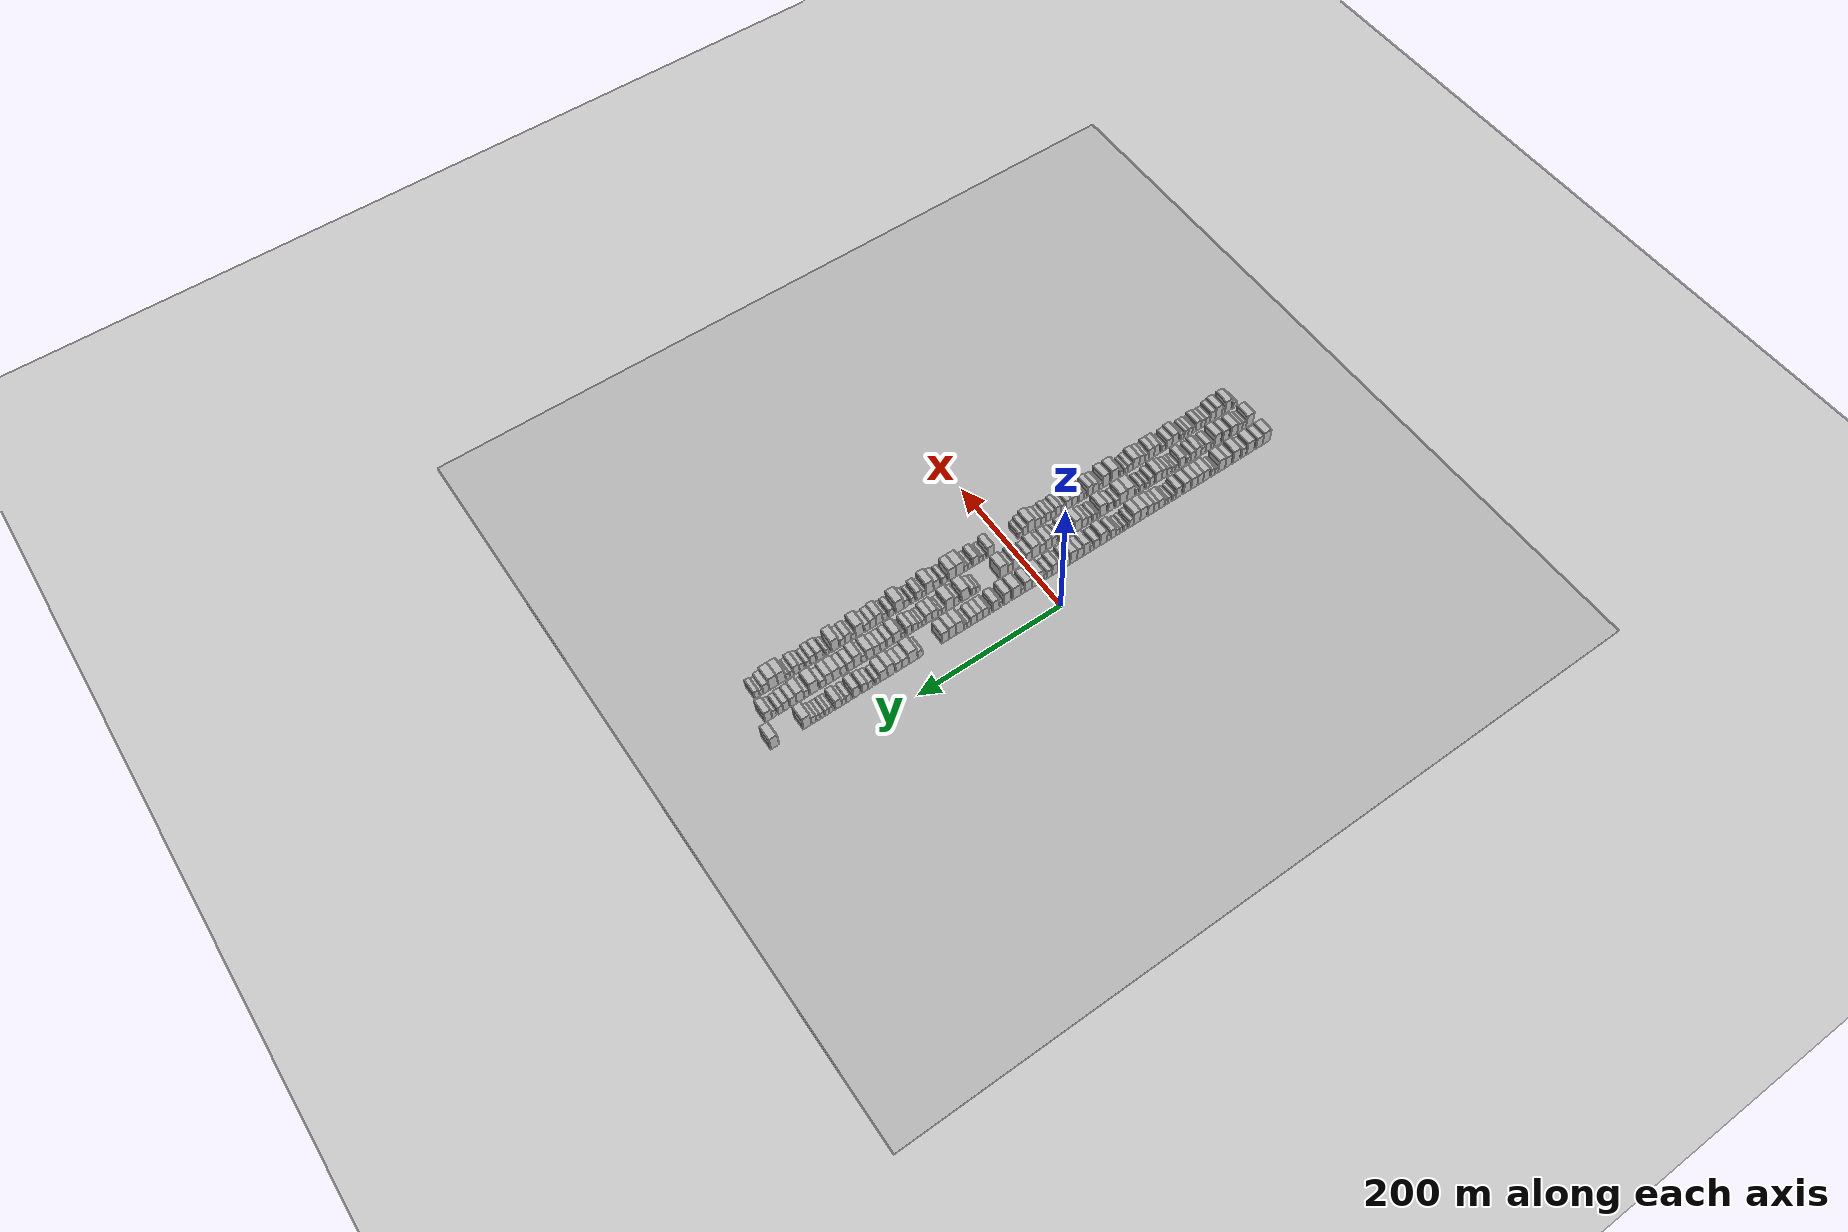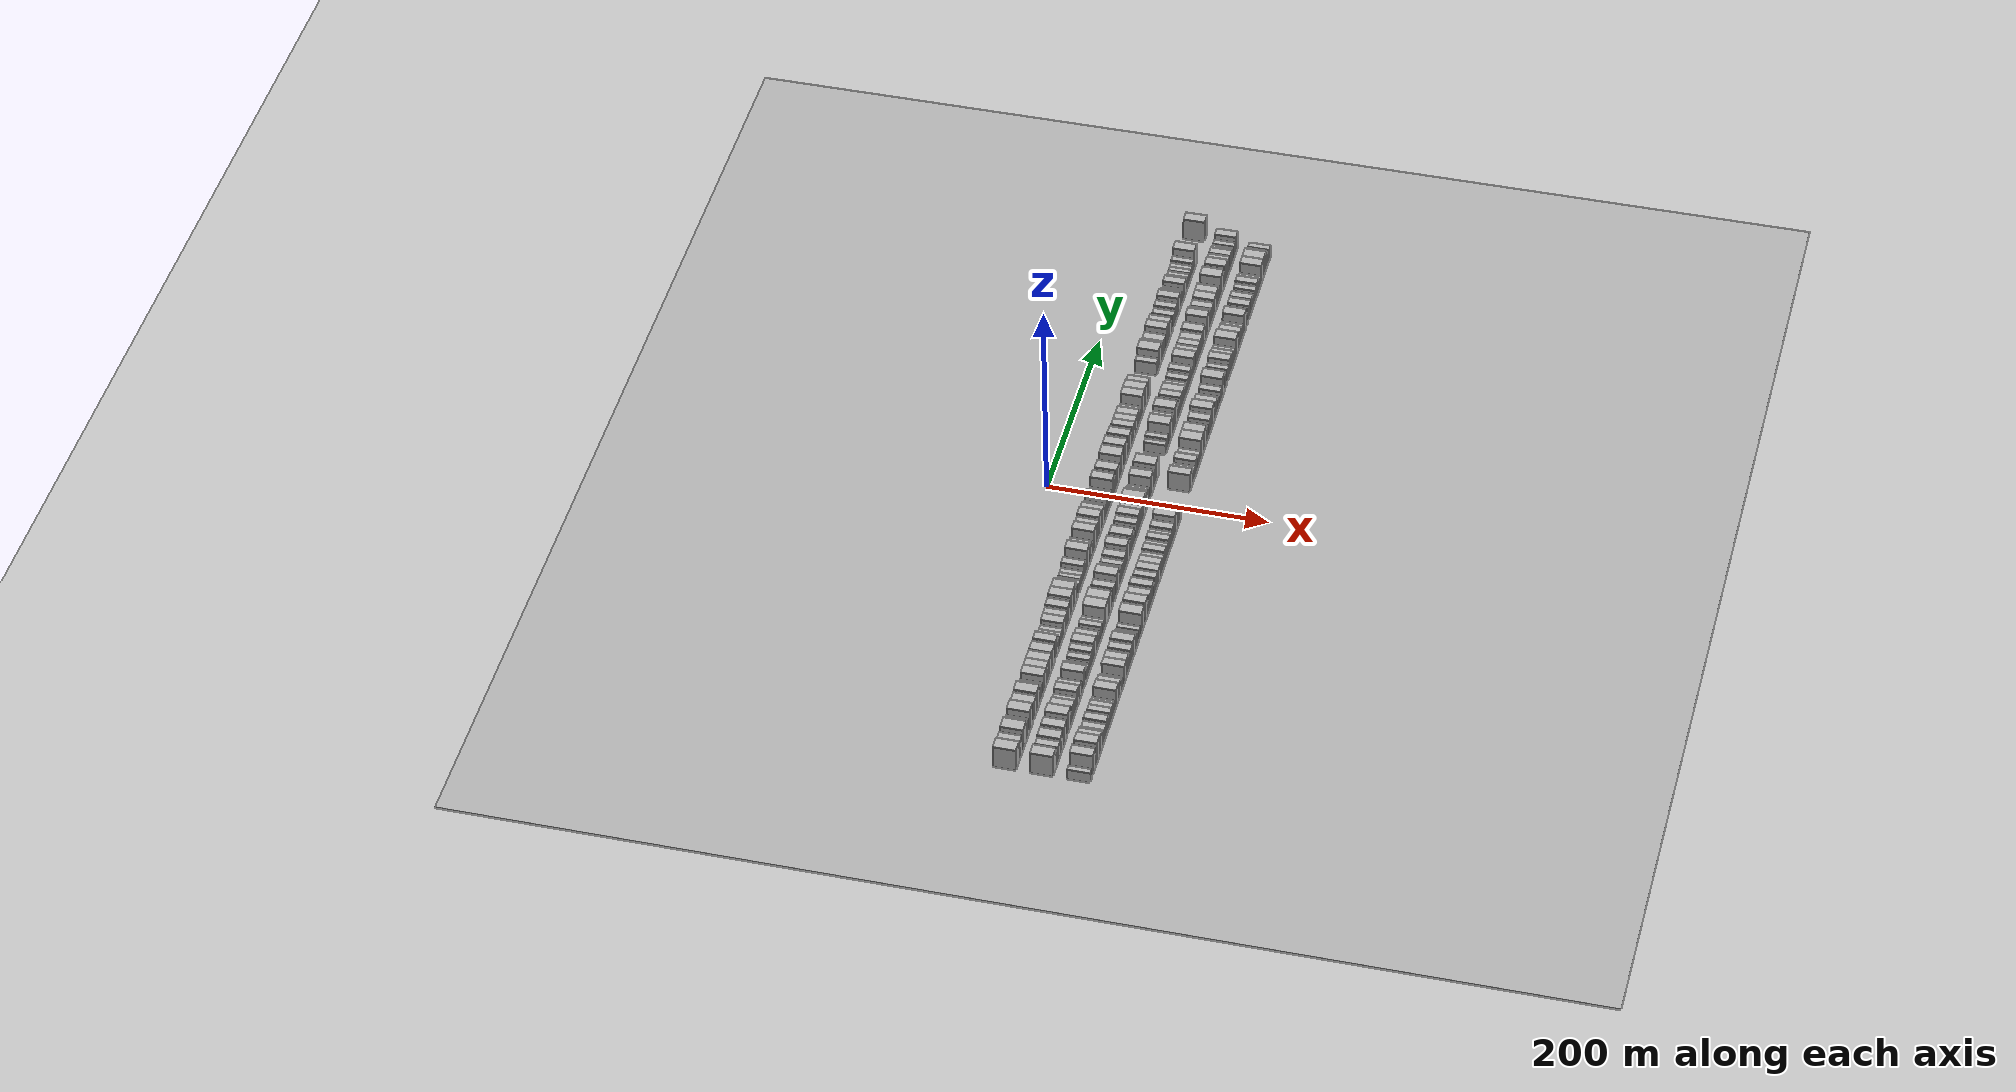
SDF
<?xml version="1.0" encoding="utf-8"?>

<sdf version="1.6">

   <world name="default">

      <gui fullscreen="0">

         <camera name="user_camera">

            <pose>-15 0 4.57585 0 0 0</pose>

            <view_controller>orbit</view_controller>

         </camera>

      </gui>

      <scene>

         <sky>

           <clouds>

             <speed>12</speed>

           </clouds>

         </sky>

         <ambient>0.4 0.4 0.4 1</ambient>

         <background>0.7 0.7 0.7 1</background>

         <shadows>1</shadows>

      </scene>

      <gravity>0 0 -9.8066</gravity>

      <magnetic_field>6e-06 2.3e-05 -4.2e-05</magnetic_field>

      <physics default="0" name="default_physics" type="ode">

         <ode>

            <solver>

               <type>quick</type>

               <iters>10</iters>

               <sor>1.0</sor>

               <use_dynamic_moi_rescaling>0</use_dynamic_moi_rescaling>

            </solver>

            <constraints>

               <cfm>0</cfm>

               <erp>0.2</erp>

               <contact_max_correcting_vel>100</contact_max_correcting_vel>

               <contact_surface_layer>0.001</contact_surface_layer>

            </constraints>

         </ode>

         <max_step_size>0.004</max_step_size>

         <real_time_factor>1</real_time_factor>

         <real_time_update_rate>250</real_time_update_rate>

      </physics>

      <light name="sun" type="directional">

         <cast_shadows>1</cast_shadows>

         <pose>0 0 10 0 0 0</pose>

         <diffuse>0.8 0.8 0.8 1</diffuse>

         <specular>0.2 0.2 0.2 1</specular>

         <attenuation>

            <range>1000</range>

            <constant>0.9</constant>

            <linear>0.01</linear>

            <quadratic>0.001</quadratic>

         </attenuation>

         <direction>-0.5 0.1 -0.9</direction>

      </light>

      <include>

         <name>ground_plane_1</name>

         <uri>model://HANNAS_ground_plane</uri>

         <pose>0 0 0  0 0 0</pose>

      </include>

      <include>

         <name>ground_plane_2</name>

         <uri>model://HANNAS_ground_plane</uri>

         <pose>100 0 0  0 0 0</pose>

      </include>

      <model name="building_1">

         <static>1</static>

         <pose frame="">50.0000 -342.1842 0 0.000000 0.000000 0.000000</pose>

         <link name="link">

            <pose frame="">0 0 12.00 0 0 0</pose>

            <collision name="collision">

               <geometry>

                  <box>

                     <size>20.0000 11.6316 24.0000</size>

                  </box>

               </geometry>

               <max_contacts>10</max_contacts>

               <surface>

                  <contact>

                     <ode/>

                  </contact>

                  <bounce/>

                  <friction>

                     <torsional>

                        <ode/>

                     </torsional>

                     <ode/>

                  </friction>

               </surface>

            </collision>

            <visual name="visual">

               <cast_shadows>0</cast_shadows>

               <geometry>

                  <box>

                     <size>20.0000 11.6316 24.0000</size>

                  </box>

               </geometry>

               <material>

                  <script>

                     <uri>model://HANNAS_wall/materials/scripts</uri>

                     <uri>model://HANNAS_wall/materials/textures</uri>

                     <name>vrc/HANNAS_wall</name>

                  </script>

               </material>

            </visual>

            <self_collide>0</self_collide>

            <enable_wind>0</enable_wind>

            <kinematic>0</kinematic>

         </link>

      </model>

      <model name="building_2">

         <static>1</static>

         <pose frame="">50.0000 -331.2911 0 0.000000 0.000000 0.000000</pose>

         <link name="link">

            <pose frame="">0 0 10.50 0 0 0</pose>

            <collision name="collision">

               <geometry>

                  <box>

                     <size>20.0000 10.1546 21.0000</size>

                  </box>

               </geometry>

               <max_contacts>10</max_contacts>

               <surface>

                  <contact>

                     <ode/>

                  </contact>

                  <bounce/>

                  <friction>

                     <torsional>

                        <ode/>

                     </torsional>

                     <ode/>

                  </friction>

               </surface>

            </collision>

            <visual name="visual">

               <cast_shadows>0</cast_shadows>

               <geometry>

                  <box>

                     <size>20.0000 10.1546 21.0000</size>

                  </box>

               </geometry>

               <material>

                  <script>

                     <uri>model://HANNAS_wall/materials/scripts</uri>

                     <uri>model://HANNAS_wall/materials/textures</uri>

                     <name>vrc/HANNAS_wall</name>

                  </script>

               </material>

            </visual>

            <self_collide>0</self_collide>

            <enable_wind>0</enable_wind>

            <kinematic>0</kinematic>

         </link>

      </model>

      <model name="building_3">

         <static>1</static>

         <pose frame="">50.0000 -317.2548 0 0.000000 0.000000 0.000000</pose>

         <link name="link">

            <pose frame="">0 0 12.00 0 0 0</pose>

            <collision name="collision">

               <geometry>

                  <box>

                     <size>20.0000 11.9180 24.0000</size>

                  </box>

               </geometry>

               <max_contacts>10</max_contacts>

               <surface>

                  <contact>

                     <ode/>

                  </contact>

                  <bounce/>

                  <friction>

                     <torsional>

                        <ode/>

                     </torsional>

                     <ode/>

                  </friction>

               </surface>

            </collision>

            <visual name="visual">

               <cast_shadows>0</cast_shadows>

               <geometry>

                  <box>

                     <size>20.0000 11.9180 24.0000</size>

                  </box>

               </geometry>

               <material>

                  <script>

                     <uri>model://HANNAS_wall/materials/scripts</uri>

                     <uri>model://HANNAS_wall/materials/textures</uri>

                     <name>vrc/HANNAS_wall</name>

                  </script>

               </material>

            </visual>

            <self_collide>0</self_collide>

            <enable_wind>0</enable_wind>

            <kinematic>0</kinematic>

         </link>

      </model>

      <model name="building_4">

         <static>1</static>

         <pose frame="">50.0000 -306.4671 0 0.000000 0.000000 0.000000</pose>

         <link name="link">

            <pose frame="">0 0 9.00 0 0 0</pose>

            <collision name="collision">

               <geometry>

                  <box>

                     <size>20.0000 7.6574 18.0000</size>

                  </box>

               </geometry>

               <max_contacts>10</max_contacts>

               <surface>

                  <contact>

                     <ode/>

                  </contact>

                  <bounce/>

                  <friction>

                     <torsional>

                        <ode/>

                     </torsional>

                     <ode/>

                  </friction>

               </surface>

            </collision>

            <visual name="visual">

               <cast_shadows>0</cast_shadows>

               <geometry>

                  <box>

                     <size>20.0000 7.6574 18.0000</size>

                  </box>

               </geometry>

               <material>

                  <script>

                     <uri>model://HANNAS_wall/materials/scripts</uri>

                     <uri>model://HANNAS_wall/materials/textures</uri>

                     <name>vrc/HANNAS_wall</name>

                  </script>

               </material>

            </visual>

            <self_collide>0</self_collide>

            <enable_wind>0</enable_wind>

            <kinematic>0</kinematic>

         </link>

      </model>

      <model name="building_5">

         <static>1</static>

         <pose frame="">50.0000 -295.0031 0 0.000000 0.000000 0.000000</pose>

         <link name="link">

            <pose frame="">0 0 12.00 0 0 0</pose>

            <collision name="collision">

               <geometry>

                  <box>

                     <size>20.0000 11.2706 24.0000</size>

                  </box>

               </geometry>

               <max_contacts>10</max_contacts>

               <surface>

                  <contact>

                     <ode/>

                  </contact>

                  <bounce/>

                  <friction>

                     <torsional>

                        <ode/>

                     </torsional>

                     <ode/>

                  </friction>

               </surface>

            </collision>

            <visual name="visual">

               <cast_shadows>0</cast_shadows>

               <geometry>

                  <box>

                     <size>20.0000 11.2706 24.0000</size>

                  </box>

               </geometry>

               <material>

                  <script>

                     <uri>model://HANNAS_wall/materials/scripts</uri>

                     <uri>model://HANNAS_wall/materials/textures</uri>

                     <name>vrc/HANNAS_wall</name>

                  </script>

               </material>

            </visual>

            <self_collide>0</self_collide>

            <enable_wind>0</enable_wind>

            <kinematic>0</kinematic>

         </link>

      </model>

      <model name="building_6">

         <static>1</static>

         <pose frame="">50.0000 -282.3011 0 0.000000 0.000000 0.000000</pose>

         <link name="link">

            <pose frame="">0 0 10.50 0 0 0</pose>

            <collision name="collision">

               <geometry>

                  <box>

                     <size>20.0000 10.1334 21.0000</size>

                  </box>

               </geometry>

               <max_contacts>10</max_contacts>

               <surface>

                  <contact>

                     <ode/>

                  </contact>

                  <bounce/>

                  <friction>

                     <torsional>

                        <ode/>

                     </torsional>

                     <ode/>

                  </friction>

               </surface>

            </collision>

            <visual name="visual">

               <cast_shadows>0</cast_shadows>

               <geometry>

                  <box>

                     <size>20.0000 10.1334 21.0000</size>

                  </box>

               </geometry>

               <material>

                  <script>

                     <uri>model://HANNAS_wall/materials/scripts</uri>

                     <uri>model://HANNAS_wall/materials/textures</uri>

                     <name>vrc/HANNAS_wall</name>

                  </script>

               </material>

            </visual>

            <self_collide>0</self_collide>

            <enable_wind>0</enable_wind>

            <kinematic>0</kinematic>

         </link>

      </model>

      <model name="building_7">

         <static>1</static>

         <pose frame="">50.0000 -271.8353 0 0.000000 0.000000 0.000000</pose>

         <link name="link">

            <pose frame="">0 0 12.00 0 0 0</pose>

            <collision name="collision">

               <geometry>

                  <box>

                     <size>20.0000 10.7983 24.0000</size>

                  </box>

               </geometry>

               <max_contacts>10</max_contacts>

               <surface>

                  <contact>

                     <ode/>

                  </contact>

                  <bounce/>

                  <friction>

                     <torsional>

                        <ode/>

                     </torsional>

                     <ode/>

                  </friction>

               </surface>

            </collision>

            <visual name="visual">

               <cast_shadows>0</cast_shadows>

               <geometry>

                  <box>

                     <size>20.0000 10.7983 24.0000</size>

                  </box>

               </geometry>

               <material>

                  <script>

                     <uri>model://HANNAS_wall/materials/scripts</uri>

                     <uri>model://HANNAS_wall/materials/textures</uri>

                     <name>vrc/HANNAS_wall</name>

                  </script>

               </material>

            </visual>

            <self_collide>0</self_collide>

            <enable_wind>0</enable_wind>

            <kinematic>0</kinematic>

         </link>

      </model>

      <model name="building_8">

         <static>1</static>

         <pose frame="">50.0000 -263.9087 0 0.000000 0.000000 0.000000</pose>

         <link name="link">

            <pose frame="">0 0 6.00 0 0 0</pose>

            <collision name="collision">

               <geometry>

                  <box>

                     <size>20.0000 5.0549 12.0000</size>

                  </box>

               </geometry>

               <max_contacts>10</max_contacts>

               <surface>

                  <contact>

                     <ode/>

                  </contact>

                  <bounce/>

                  <friction>

                     <torsional>

                        <ode/>

                     </torsional>

                     <ode/>

                  </friction>

               </surface>

            </collision>

            <visual name="visual">

               <cast_shadows>0</cast_shadows>

               <geometry>

                  <box>

                     <size>20.0000 5.0549 12.0000</size>

                  </box>

               </geometry>

               <material>

                  <script>

                     <uri>model://HANNAS_wall/materials/scripts</uri>

                     <uri>model://HANNAS_wall/materials/textures</uri>

                     <name>vrc/HANNAS_wall</name>

                  </script>

               </material>

            </visual>

            <self_collide>0</self_collide>

            <enable_wind>0</enable_wind>

            <kinematic>0</kinematic>

         </link>

      </model>

      <model name="building_9">

         <static>1</static>

         <pose frame="">50.0000 -258.1694 0 0.000000 0.000000 0.000000</pose>

         <link name="link">

            <pose frame="">0 0 7.50 0 0 0</pose>

            <collision name="collision">

               <geometry>

                  <box>

                     <size>20.0000 6.4235 15.0000</size>

                  </box>

               </geometry>

               <max_contacts>10</max_contacts>

               <surface>

                  <contact>

                     <ode/>

                  </contact>

                  <bounce/>

                  <friction>

                     <torsional>

                        <ode/>

                     </torsional>

                     <ode/>

                  </friction>

               </surface>

            </collision>

            <visual name="visual">

               <cast_shadows>0</cast_shadows>

               <geometry>

                  <box>

                     <size>20.0000 6.4235 15.0000</size>

                  </box>

               </geometry>

               <material>

                  <script>

                     <uri>model://HANNAS_wall/materials/scripts</uri>

                     <uri>model://HANNAS_wall/materials/textures</uri>

                     <name>vrc/HANNAS_wall</name>

                  </script>

               </material>

            </visual>

            <self_collide>0</self_collide>

            <enable_wind>0</enable_wind>

            <kinematic>0</kinematic>

         </link>

      </model>

      <model name="building_10">

         <static>1</static>

         <pose frame="">50.0000 -247.8679 0 0.000000 0.000000 0.000000</pose>

         <link name="link">

            <pose frame="">0 0 10.50 0 0 0</pose>

            <collision name="collision">

               <geometry>

                  <box>

                     <size>20.0000 10.1796 21.0000</size>

                  </box>

               </geometry>

               <max_contacts>10</max_contacts>

               <surface>

                  <contact>

                     <ode/>

                  </contact>

                  <bounce/>

                  <friction>

                     <torsional>

                        <ode/>

                     </torsional>

                     <ode/>

                  </friction>

               </surface>

            </collision>

            <visual name="visual">

               <cast_shadows>0</cast_shadows>

               <geometry>

                  <box>

                     <size>20.0000 10.1796 21.0000</size>

                  </box>

               </geometry>

               <material>

                  <script>

                     <uri>model://HANNAS_wall/materials/scripts</uri>

                     <uri>model://HANNAS_wall/materials/textures</uri>

                     <name>vrc/HANNAS_wall</name>

                  </script>

               </material>

            </visual>

            <self_collide>0</self_collide>

            <enable_wind>0</enable_wind>

            <kinematic>0</kinematic>

         </link>

      </model>

      <model name="building_11">

         <static>1</static>

         <pose frame="">50.0000 -238.3900 0 0.000000 0.000000 0.000000</pose>

         <link name="link">

            <pose frame="">0 0 10.50 0 0 0</pose>

            <collision name="collision">

               <geometry>

                  <box>

                     <size>20.0000 8.7761 21.0000</size>

                  </box>

               </geometry>

               <max_contacts>10</max_contacts>

               <surface>

                  <contact>

                     <ode/>

                  </contact>

                  <bounce/>

                  <friction>

                     <torsional>

                        <ode/>

                     </torsional>

                     <ode/>

                  </friction>

               </surface>

            </collision>

            <visual name="visual">

               <cast_shadows>0</cast_shadows>

               <geometry>

                  <box>

                     <size>20.0000 8.7761 21.0000</size>

                  </box>

               </geometry>

               <material>

                  <script>

                     <uri>model://HANNAS_wall/materials/scripts</uri>

                     <uri>model://HANNAS_wall/materials/textures</uri>

                     <name>vrc/HANNAS_wall</name>

                  </script>

               </material>

            </visual>

            <self_collide>0</self_collide>

            <enable_wind>0</enable_wind>

            <kinematic>0</kinematic>

         </link>

      </model>

      <model name="building_12">

         <static>1</static>

         <pose frame="">50.0000 -229.1908 0 0.000000 0.000000 0.000000</pose>

         <link name="link">

            <pose frame="">0 0 10.50 0 0 0</pose>

            <collision name="collision">

               <geometry>

                  <box>

                     <size>20.0000 9.6222 21.0000</size>

                  </box>

               </geometry>

               <max_contacts>10</max_contacts>

               <surface>

                  <contact>

                     <ode/>

                  </contact>

                  <bounce/>

                  <friction>

                     <torsional>

                        <ode/>

                     </torsional>

                     <ode/>

                  </friction>

               </surface>

            </collision>

            <visual name="visual">

               <cast_shadows>0</cast_shadows>

               <geometry>

                  <box>

                     <size>20.0000 9.6222 21.0000</size>

                  </box>

               </geometry>

               <material>

                  <script>

                     <uri>model://HANNAS_wall/materials/scripts</uri>

                     <uri>model://HANNAS_wall/materials/textures</uri>

                     <name>vrc/HANNAS_wall</name>

                  </script>

               </material>

            </visual>

            <self_collide>0</self_collide>

            <enable_wind>0</enable_wind>

            <kinematic>0</kinematic>

         </link>

      </model>

      <model name="building_13">

         <static>1</static>

         <pose frame="">50.0000 -218.1350 0 0.000000 0.000000 0.000000</pose>

         <link name="link">

            <pose frame="">0 0 10.50 0 0 0</pose>

            <collision name="collision">

               <geometry>

                  <box>

                     <size>20.0000 10.4896 21.0000</size>

                  </box>

               </geometry>

               <max_contacts>10</max_contacts>

               <surface>

                  <contact>

                     <ode/>

                  </contact>

                  <bounce/>

                  <friction>

                     <torsional>

                        <ode/>

                     </torsional>

                     <ode/>

                  </friction>

               </surface>

            </collision>

            <visual name="visual">

               <cast_shadows>0</cast_shadows>

               <geometry>

                  <box>

                     <size>20.0000 10.4896 21.0000</size>

                  </box>

               </geometry>

               <material>

                  <script>

                     <uri>model://HANNAS_wall/materials/scripts</uri>

                     <uri>model://HANNAS_wall/materials/textures</uri>

                     <name>vrc/HANNAS_wall</name>

                  </script>

               </material>

            </visual>

            <self_collide>0</self_collide>

            <enable_wind>0</enable_wind>

            <kinematic>0</kinematic>

         </link>

      </model>

      <model name="building_14">

         <static>1</static>

         <pose frame="">50.0000 -205.4261 0 0.000000 0.000000 0.000000</pose>

         <link name="link">

            <pose frame="">0 0 10.50 0 0 0</pose>

            <collision name="collision">

               <geometry>

                  <box>

                     <size>20.0000 8.9281 21.0000</size>

                  </box>

               </geometry>

               <max_contacts>10</max_contacts>

               <surface>

                  <contact>

                     <ode/>

                  </contact>

                  <bounce/>

                  <friction>

                     <torsional>

                        <ode/>

                     </torsional>

                     <ode/>

                  </friction>

               </surface>

            </collision>

            <visual name="visual">

               <cast_shadows>0</cast_shadows>

               <geometry>

                  <box>

                     <size>20.0000 8.9281 21.0000</size>

                  </box>

               </geometry>

               <material>

                  <script>

                     <uri>model://HANNAS_wall/materials/scripts</uri>

                     <uri>model://HANNAS_wall/materials/textures</uri>

                     <name>vrc/HANNAS_wall</name>

                  </script>

               </material>

            </visual>

            <self_collide>0</self_collide>

            <enable_wind>0</enable_wind>

            <kinematic>0</kinematic>

         </link>

      </model>

      <model name="building_15">

         <static>1</static>

         <pose frame="">50.0000 -198.3255 0 0.000000 0.000000 0.000000</pose>

         <link name="link">

            <pose frame="">0 0 6.00 0 0 0</pose>

            <collision name="collision">

               <geometry>

                  <box>

                     <size>20.0000 5.2732 12.0000</size>

                  </box>

               </geometry>

               <max_contacts>10</max_contacts>

               <surface>

                  <contact>

                     <ode/>

                  </contact>

                  <bounce/>

                  <friction>

                     <torsional>

                        <ode/>

                     </torsional>

                     <ode/>

                  </friction>

               </surface>

            </collision>

            <visual name="visual">

               <cast_shadows>0</cast_shadows>

               <geometry>

                  <box>

                     <size>20.0000 5.2732 12.0000</size>

                  </box>

               </geometry>

               <material>

                  <script>

                     <uri>model://HANNAS_wall/materials/scripts</uri>

                     <uri>model://HANNAS_wall/materials/textures</uri>

                     <name>vrc/HANNAS_wall</name>

                  </script>

               </material>

            </visual>

            <self_collide>0</self_collide>

            <enable_wind>0</enable_wind>

            <kinematic>0</kinematic>

         </link>

      </model>

      <model name="building_16">

         <static>1</static>

         <pose frame="">50.0000 -191.0154 0 0.000000 0.000000 0.000000</pose>

         <link name="link">

            <pose frame="">0 0 6.00 0 0 0</pose>

            <collision name="collision">

               <geometry>

                  <box>

                     <size>20.0000 5.3471 12.0000</size>

                  </box>

               </geometry>

               <max_contacts>10</max_contacts>

               <surface>

                  <contact>

                     <ode/>

                  </contact>

                  <bounce/>

                  <friction>

                     <torsional>

                        <ode/>

                     </torsional>

                     <ode/>

                  </friction>

               </surface>

            </collision>

            <visual name="visual">

               <cast_shadows>0</cast_shadows>

               <geometry>

                  <box>

                     <size>20.0000 5.3471 12.0000</size>

                  </box>

               </geometry>

               <material>

                  <script>

                     <uri>model://HANNAS_wall/materials/scripts</uri>

                     <uri>model://HANNAS_wall/materials/textures</uri>

                     <name>vrc/HANNAS_wall</name>

                  </script>

               </material>

            </visual>

            <self_collide>0</self_collide>

            <enable_wind>0</enable_wind>

            <kinematic>0</kinematic>

         </link>

      </model>

      <model name="building_17">

         <static>1</static>

         <pose frame="">50.0000 -185.7829 0 0.000000 0.000000 0.000000</pose>

         <link name="link">

            <pose frame="">0 0 6.00 0 0 0</pose>

            <collision name="collision">

               <geometry>

                  <box>

                     <size>20.0000 5.1178 12.0000</size>

                  </box>

               </geometry>

               <max_contacts>10</max_contacts>

               <surface>

                  <contact>

                     <ode/>

                  </contact>

                  <bounce/>

                  <friction>

                     <torsional>

                        <ode/>

                     </torsional>

                     <ode/>

                  </friction>

               </surface>

            </collision>

            <visual name="visual">

               <cast_shadows>0</cast_shadows>

               <geometry>

                  <box>

                     <size>20.0000 5.1178 12.0000</size>

                  </box>

               </geometry>

               <material>

                  <script>

                     <uri>model://HANNAS_wall/materials/scripts</uri>

                     <uri>model://HANNAS_wall/materials/textures</uri>

                     <name>vrc/HANNAS_wall</name>

                  </script>

               </material>

            </visual>

            <self_collide>0</self_collide>

            <enable_wind>0</enable_wind>

            <kinematic>0</kinematic>

         </link>

      </model>

      <model name="building_18">

         <static>1</static>

         <pose frame="">50.0000 -178.7410 0 0.000000 0.000000 0.000000</pose>

         <link name="link">

            <pose frame="">0 0 9.00 0 0 0</pose>

            <collision name="collision">

               <geometry>

                  <box>

                     <size>20.0000 8.9659 18.0000</size>

                  </box>

               </geometry>

               <max_contacts>10</max_contacts>

               <surface>

                  <contact>

                     <ode/>

                  </contact>

                  <bounce/>

                  <friction>

                     <torsional>

                        <ode/>

                     </torsional>

                     <ode/>

                  </friction>

               </surface>

            </collision>

            <visual name="visual">

               <cast_shadows>0</cast_shadows>

               <geometry>

                  <box>

                     <size>20.0000 8.9659 18.0000</size>

                  </box>

               </geometry>

               <material>

                  <script>

                     <uri>model://HANNAS_wall/materials/scripts</uri>

                     <uri>model://HANNAS_wall/materials/textures</uri>

                     <name>vrc/HANNAS_wall</name>

                  </script>

               </material>

            </visual>

            <self_collide>0</self_collide>

            <enable_wind>0</enable_wind>

            <kinematic>0</kinematic>

         </link>

      </model>

      <model name="building_19">

         <static>1</static>

         <pose frame="">50.0000 -170.5910 0 0.000000 0.000000 0.000000</pose>

         <link name="link">

            <pose frame="">0 0 9.00 0 0 0</pose>

            <collision name="collision">

               <geometry>

                  <box>

                     <size>20.0000 7.3341 18.0000</size>

                  </box>

               </geometry>

               <max_contacts>10</max_contacts>

               <surface>

                  <contact>

                     <ode/>

                  </contact>

                  <bounce/>

                  <friction>

                     <torsional>

                        <ode/>

                     </torsional>

                     <ode/>

                  </friction>

               </surface>

            </collision>

            <visual name="visual">

               <cast_shadows>0</cast_shadows>

               <geometry>

                  <box>

                     <size>20.0000 7.3341 18.0000</size>

                  </box>

               </geometry>

               <material>

                  <script>

                     <uri>model://HANNAS_wall/materials/scripts</uri>

                     <uri>model://HANNAS_wall/materials/textures</uri>

                     <name>vrc/HANNAS_wall</name>

                  </script>

               </material>

            </visual>

            <self_collide>0</self_collide>

            <enable_wind>0</enable_wind>

            <kinematic>0</kinematic>

         </link>

      </model>

      <model name="building_20">

         <static>1</static>

         <pose frame="">50.0000 -162.3846 0 0.000000 0.000000 0.000000</pose>

         <link name="link">

            <pose frame="">0 0 10.50 0 0 0</pose>

            <collision name="collision">

               <geometry>

                  <box>

                     <size>20.0000 9.0788 21.0000</size>

                  </box>

               </geometry>

               <max_contacts>10</max_contacts>

               <surface>

                  <contact>

                     <ode/>

                  </contact>

                  <bounce/>

                  <friction>

                     <torsional>

                        <ode/>

                     </torsional>

                     <ode/>

                  </friction>

               </surface>

            </collision>

            <visual name="visual">

               <cast_shadows>0</cast_shadows>

               <geometry>

                  <box>

                     <size>20.0000 9.0788 21.0000</size>

                  </box>

               </geometry>

               <material>

                  <script>

                     <uri>model://HANNAS_wall/materials/scripts</uri>

                     <uri>model://HANNAS_wall/materials/textures</uri>

                     <name>vrc/HANNAS_wall</name>

                  </script>

               </material>

            </visual>

            <self_collide>0</self_collide>

            <enable_wind>0</enable_wind>

            <kinematic>0</kinematic>

         </link>

      </model>

      <model name="building_21">

         <static>1</static>

         <pose frame="">50.0000 -151.5505 0 0.000000 0.000000 0.000000</pose>

         <link name="link">

            <pose frame="">0 0 12.00 0 0 0</pose>

            <collision name="collision">

               <geometry>

                  <box>

                     <size>20.0000 10.5892 24.0000</size>

                  </box>

               </geometry>

               <max_contacts>10</max_contacts>

               <surface>

                  <contact>

                     <ode/>

                  </contact>

                  <bounce/>

                  <friction>

                     <torsional>

                        <ode/>

                     </torsional>

                     <ode/>

                  </friction>

               </surface>

            </collision>

            <visual name="visual">

               <cast_shadows>0</cast_shadows>

               <geometry>

                  <box>

                     <size>20.0000 10.5892 24.0000</size>

                  </box>

               </geometry>

               <material>

                  <script>

                     <uri>model://HANNAS_wall/materials/scripts</uri>

                     <uri>model://HANNAS_wall/materials/textures</uri>

                     <name>vrc/HANNAS_wall</name>

                  </script>

               </material>

            </visual>

            <self_collide>0</self_collide>

            <enable_wind>0</enable_wind>

            <kinematic>0</kinematic>

         </link>

      </model>

      <model name="building_22">

         <static>1</static>

         <pose frame="">50.0000 -141.2059 0 0.000000 0.000000 0.000000</pose>

         <link name="link">

            <pose frame="">0 0 12.00 0 0 0</pose>

            <collision name="collision">

               <geometry>

                  <box>

                     <size>20.0000 10.1000 24.0000</size>

                  </box>

               </geometry>

               <max_contacts>10</max_contacts>

               <surface>

                  <contact>

                     <ode/>

                  </contact>

                  <bounce/>

                  <friction>

                     <torsional>

                        <ode/>

                     </torsional>

                     <ode/>

                  </friction>

               </surface>

            </collision>

            <visual name="visual">

               <cast_shadows>0</cast_shadows>

               <geometry>

                  <box>

                     <size>20.0000 10.1000 24.0000</size>

                  </box>

               </geometry>

               <material>

                  <script>

                     <uri>model://HANNAS_wall/materials/scripts</uri>

                     <uri>model://HANNAS_wall/materials/textures</uri>

                     <name>vrc/HANNAS_wall</name>

                  </script>

               </material>

            </visual>

            <self_collide>0</self_collide>

            <enable_wind>0</enable_wind>

            <kinematic>0</kinematic>

         </link>

      </model>

      <model name="building_23">

         <static>1</static>

         <pose frame="">50.0000 -132.9328 0 0.000000 0.000000 0.000000</pose>

         <link name="link">

            <pose frame="">0 0 7.50 0 0 0</pose>

            <collision name="collision">

               <geometry>

                  <box>

                     <size>20.0000 6.4463 15.0000</size>

                  </box>

               </geometry>

               <max_contacts>10</max_contacts>

               <surface>

                  <contact>

                     <ode/>

                  </contact>

                  <bounce/>

                  <friction>

                     <torsional>

                        <ode/>

                     </torsional>

                     <ode/>

                  </friction>

               </surface>

            </collision>

            <visual name="visual">

               <cast_shadows>0</cast_shadows>

               <geometry>

                  <box>

                     <size>20.0000 6.4463 15.0000</size>

                  </box>

               </geometry>

               <material>

                  <script>

                     <uri>model://HANNAS_wall/materials/scripts</uri>

                     <uri>model://HANNAS_wall/materials/textures</uri>

                     <name>vrc/HANNAS_wall</name>

                  </script>

               </material>

            </visual>

            <self_collide>0</self_collide>

            <enable_wind>0</enable_wind>

            <kinematic>0</kinematic>

         </link>

      </model>

      <model name="building_24">

         <static>1</static>

         <pose frame="">50.0000 -123.9545 0 0.000000 0.000000 0.000000</pose>

         <link name="link">

            <pose frame="">0 0 6.00 0 0 0</pose>

            <collision name="collision">

               <geometry>

                  <box>

                     <size>20.0000 5.5104 12.0000</size>

                  </box>

               </geometry>

               <max_contacts>10</max_contacts>

               <surface>

                  <contact>

                     <ode/>

                  </contact>

                  <bounce/>

                  <friction>

                     <torsional>

                        <ode/>

                     </torsional>

                     <ode/>

                  </friction>

               </surface>

            </collision>

            <visual name="visual">

               <cast_shadows>0</cast_shadows>

               <geometry>

                  <box>

                     <size>20.0000 5.5104 12.0000</size>

                  </box>

               </geometry>

               <material>

                  <script>

                     <uri>model://HANNAS_wall/materials/scripts</uri>

                     <uri>model://HANNAS_wall/materials/textures</uri>

                     <name>vrc/HANNAS_wall</name>

                  </script>

               </material>

            </visual>

            <self_collide>0</self_collide>

            <enable_wind>0</enable_wind>

            <kinematic>0</kinematic>

         </link>

      </model>

      <model name="building_25">

         <static>1</static>

         <pose frame="">50.0000 -117.6842 0 0.000000 0.000000 0.000000</pose>

         <link name="link">

            <pose frame="">0 0 6.00 0 0 0</pose>

            <collision name="collision">

               <geometry>

                  <box>

                     <size>20.0000 5.0301 12.0000</size>

                  </box>

               </geometry>

               <max_contacts>10</max_contacts>

               <surface>

                  <contact>

                     <ode/>

                  </contact>

                  <bounce/>

                  <friction>

                     <torsional>

                        <ode/>

                     </torsional>

                     <ode/>

                  </friction>

               </surface>

            </collision>

            <visual name="visual">

               <cast_shadows>0</cast_shadows>

               <geometry>

                  <box>

                     <size>20.0000 5.0301 12.0000</size>

                  </box>

               </geometry>

               <material>

                  <script>

                     <uri>model://HANNAS_wall/materials/scripts</uri>

                     <uri>model://HANNAS_wall/materials/textures</uri>

                     <name>vrc/HANNAS_wall</name>

                  </script>

               </material>

            </visual>

            <self_collide>0</self_collide>

            <enable_wind>0</enable_wind>

            <kinematic>0</kinematic>

         </link>

      </model>

      <model name="building_26">

         <static>1</static>

         <pose frame="">50.0000 -112.3995 0 0.000000 0.000000 0.000000</pose>

         <link name="link">

            <pose frame="">0 0 6.00 0 0 0</pose>

            <collision name="collision">

               <geometry>

                  <box>

                     <size>20.0000 5.5393 12.0000</size>

                  </box>

               </geometry>

               <max_contacts>10</max_contacts>

               <surface>

                  <contact>

                     <ode/>

                  </contact>

                  <bounce/>

                  <friction>

                     <torsional>

                        <ode/>

                     </torsional>

                     <ode/>

                  </friction>

               </surface>

            </collision>

            <visual name="visual">

               <cast_shadows>0</cast_shadows>

               <geometry>

                  <box>

                     <size>20.0000 5.5393 12.0000</size>

                  </box>

               </geometry>

               <material>

                  <script>

                     <uri>model://HANNAS_wall/materials/scripts</uri>

                     <uri>model://HANNAS_wall/materials/textures</uri>

                     <name>vrc/HANNAS_wall</name>

                  </script>

               </material>

            </visual>

            <self_collide>0</self_collide>

            <enable_wind>0</enable_wind>

            <kinematic>0</kinematic>

         </link>

      </model>

      <model name="building_27">

         <static>1</static>

         <pose frame="">50.0000 -105.8643 0 0.000000 0.000000 0.000000</pose>

         <link name="link">

            <pose frame="">0 0 9.00 0 0 0</pose>

            <collision name="collision">

               <geometry>

                  <box>

                     <size>20.0000 7.5312 18.0000</size>

                  </box>

               </geometry>

               <max_contacts>10</max_contacts>

               <surface>

                  <contact>

                     <ode/>

                  </contact>

                  <bounce/>

                  <friction>

                     <torsional>

                        <ode/>

                     </torsional>

                     <ode/>

                  </friction>

               </surface>

            </collision>

            <visual name="visual">

               <cast_shadows>0</cast_shadows>

               <geometry>

                  <box>

                     <size>20.0000 7.5312 18.0000</size>

                  </box>

               </geometry>

               <material>

                  <script>

                     <uri>model://HANNAS_wall/materials/scripts</uri>

                     <uri>model://HANNAS_wall/materials/textures</uri>

                     <name>vrc/HANNAS_wall</name>

                  </script>

               </material>

            </visual>

            <self_collide>0</self_collide>

            <enable_wind>0</enable_wind>

            <kinematic>0</kinematic>

         </link>

      </model>

      <model name="building_28">

         <static>1</static>

         <pose frame="">50.0000 -99.3630 0 0.000000 0.000000 0.000000</pose>

         <link name="link">

            <pose frame="">0 0 6.00 0 0 0</pose>

            <collision name="collision">

               <geometry>

                  <box>

                     <size>20.0000 5.4712 12.0000</size>

                  </box>

               </geometry>

               <max_contacts>10</max_contacts>

               <surface>

                  <contact>

                     <ode/>

                  </contact>

                  <bounce/>

                  <friction>

                     <torsional>

                        <ode/>

                     </torsional>

                     <ode/>

                  </friction>

               </surface>

            </collision>

            <visual name="visual">

               <cast_shadows>0</cast_shadows>

               <geometry>

                  <box>

                     <size>20.0000 5.4712 12.0000</size>

                  </box>

               </geometry>

               <material>

                  <script>

                     <uri>model://HANNAS_wall/materials/scripts</uri>

                     <uri>model://HANNAS_wall/materials/textures</uri>

                     <name>vrc/HANNAS_wall</name>

                  </script>

               </material>

            </visual>

            <self_collide>0</self_collide>

            <enable_wind>0</enable_wind>

            <kinematic>0</kinematic>

         </link>

      </model>

      <model name="building_29">

         <static>1</static>

         <pose frame="">50.0000 -91.5190 0 0.000000 0.000000 0.000000</pose>

         <link name="link">

            <pose frame="">0 0 12.00 0 0 0</pose>

            <collision name="collision">

               <geometry>

                  <box>

                     <size>20.0000 10.2168 24.0000</size>

                  </box>

               </geometry>

               <max_contacts>10</max_contacts>

               <surface>

                  <contact>

                     <ode/>

                  </contact>

                  <bounce/>

                  <friction>

                     <torsional>

                        <ode/>

                     </torsional>

                     <ode/>

                  </friction>

               </surface>

            </collision>

            <visual name="visual">

               <cast_shadows>0</cast_shadows>

               <geometry>

                  <box>

                     <size>20.0000 10.2168 24.0000</size>

                  </box>

               </geometry>

               <material>

                  <script>

                     <uri>model://HANNAS_wall/materials/scripts</uri>

                     <uri>model://HANNAS_wall/materials/textures</uri>

                     <name>vrc/HANNAS_wall</name>

                  </script>

               </material>

            </visual>

            <self_collide>0</self_collide>

            <enable_wind>0</enable_wind>

            <kinematic>0</kinematic>

         </link>

      </model>

      <model name="building_30">

         <static>1</static>

         <pose frame="">50.0000 -80.9997 0 0.000000 0.000000 0.000000</pose>

         <link name="link">

            <pose frame="">0 0 9.00 0 0 0</pose>

            <collision name="collision">

               <geometry>

                  <box>

                     <size>20.0000 8.8217 18.0000</size>

                  </box>

               </geometry>

               <max_contacts>10</max_contacts>

               <surface>

                  <contact>

                     <ode/>

                  </contact>

                  <bounce/>

                  <friction>

                     <torsional>

                        <ode/>

                     </torsional>

                     <ode/>

                  </friction>

               </surface>

            </collision>

            <visual name="visual">

               <cast_shadows>0</cast_shadows>

               <geometry>

                  <box>

                     <size>20.0000 8.8217 18.0000</size>

                  </box>

               </geometry>

               <material>

                  <script>

                     <uri>model://HANNAS_wall/materials/scripts</uri>

                     <uri>model://HANNAS_wall/materials/textures</uri>

                     <name>vrc/HANNAS_wall</name>

                  </script>

               </material>

            </visual>

            <self_collide>0</self_collide>

            <enable_wind>0</enable_wind>

            <kinematic>0</kinematic>

         </link>

      </model>

      <model name="building_31">

         <static>1</static>

         <pose frame="">50.0000 -73.9480 0 0.000000 0.000000 0.000000</pose>

         <link name="link">

            <pose frame="">0 0 6.00 0 0 0</pose>

            <collision name="collision">

               <geometry>

                  <box>

                     <size>20.0000 5.2818 12.0000</size>

                  </box>

               </geometry>

               <max_contacts>10</max_contacts>

               <surface>

                  <contact>

                     <ode/>

                  </contact>

                  <bounce/>

                  <friction>

                     <torsional>

                        <ode/>

                     </torsional>

                     <ode/>

                  </friction>

               </surface>

            </collision>

            <visual name="visual">

               <cast_shadows>0</cast_shadows>

               <geometry>

                  <box>

                     <size>20.0000 5.2818 12.0000</size>

                  </box>

               </geometry>

               <material>

                  <script>

                     <uri>model://HANNAS_wall/materials/scripts</uri>

                     <uri>model://HANNAS_wall/materials/textures</uri>

                     <name>vrc/HANNAS_wall</name>

                  </script>

               </material>

            </visual>

            <self_collide>0</self_collide>

            <enable_wind>0</enable_wind>

            <kinematic>0</kinematic>

         </link>

      </model>

      <model name="building_32">

         <static>1</static>

         <pose frame="">50.0000 -66.4637 0 0.000000 0.000000 0.000000</pose>

         <link name="link">

            <pose frame="">0 0 12.00 0 0 0</pose>

            <collision name="collision">

               <geometry>

                  <box>

                     <size>20.0000 9.6868 24.0000</size>

                  </box>

               </geometry>

               <max_contacts>10</max_contacts>

               <surface>

                  <contact>

                     <ode/>

                  </contact>

                  <bounce/>

                  <friction>

                     <torsional>

                        <ode/>

                     </torsional>

                     <ode/>

                  </friction>

               </surface>

            </collision>

            <visual name="visual">

               <cast_shadows>0</cast_shadows>

               <geometry>

                  <box>

                     <size>20.0000 9.6868 24.0000</size>

                  </box>

               </geometry>

               <material>

                  <script>

                     <uri>model://HANNAS_wall/materials/scripts</uri>

                     <uri>model://HANNAS_wall/materials/textures</uri>

                     <name>vrc/HANNAS_wall</name>

                  </script>

               </material>

            </visual>

            <self_collide>0</self_collide>

            <enable_wind>0</enable_wind>

            <kinematic>0</kinematic>

         </link>

      </model>

      <model name="building_33">

         <static>1</static>

         <pose frame="">50.0000 -57.0321 0 0.000000 0.000000 0.000000</pose>

         <link name="link">

            <pose frame="">0 0 10.50 0 0 0</pose>

            <collision name="collision">

               <geometry>

                  <box>

                     <size>20.0000 9.1765 21.0000</size>

                  </box>

               </geometry>

               <max_contacts>10</max_contacts>

               <surface>

                  <contact>

                     <ode/>

                  </contact>

                  <bounce/>

                  <friction>

                     <torsional>

                        <ode/>

                     </torsional>

                     <ode/>

                  </friction>

               </surface>

            </collision>

            <visual name="visual">

               <cast_shadows>0</cast_shadows>

               <geometry>

                  <box>

                     <size>20.0000 9.1765 21.0000</size>

                  </box>

               </geometry>

               <material>

                  <script>

                     <uri>model://HANNAS_wall/materials/scripts</uri>

                     <uri>model://HANNAS_wall/materials/textures</uri>

                     <name>vrc/HANNAS_wall</name>

                  </script>

               </material>

            </visual>

            <self_collide>0</self_collide>

            <enable_wind>0</enable_wind>

            <kinematic>0</kinematic>

         </link>

      </model>

      <model name="building_34">

         <static>1</static>

         <pose frame="">50.0000 -47.3731 0 0.000000 0.000000 0.000000</pose>

         <link name="link">

            <pose frame="">0 0 12.00 0 0 0</pose>

            <collision name="collision">

               <geometry>

                  <box>

                     <size>20.0000 10.1416 24.0000</size>

                  </box>

               </geometry>

               <max_contacts>10</max_contacts>

               <surface>

                  <contact>

                     <ode/>

                  </contact>

                  <bounce/>

                  <friction>

                     <torsional>

                        <ode/>

                     </torsional>

                     <ode/>

                  </friction>

               </surface>

            </collision>

            <visual name="visual">

               <cast_shadows>0</cast_shadows>

               <geometry>

                  <box>

                     <size>20.0000 10.1416 24.0000</size>

                  </box>

               </geometry>

               <material>

                  <script>

                     <uri>model://HANNAS_wall/materials/scripts</uri>

                     <uri>model://HANNAS_wall/materials/textures</uri>

                     <name>vrc/HANNAS_wall</name>

                  </script>

               </material>

            </visual>

            <self_collide>0</self_collide>

            <enable_wind>0</enable_wind>

            <kinematic>0</kinematic>

         </link>

      </model>

      <model name="building_35">

         <static>1</static>

         <pose frame="">50.0000 -37.0855 0 0.000000 0.000000 0.000000</pose>

         <link name="link">

            <pose frame="">0 0 10.50 0 0 0</pose>

            <collision name="collision">

               <geometry>

                  <box>

                     <size>20.0000 8.4335 21.0000</size>

                  </box>

               </geometry>

               <max_contacts>10</max_contacts>

               <surface>

                  <contact>

                     <ode/>

                  </contact>

                  <bounce/>

                  <friction>

                     <torsional>

                        <ode/>

                     </torsional>

                     <ode/>

                  </friction>

               </surface>

            </collision>

            <visual name="visual">

               <cast_shadows>0</cast_shadows>

               <geometry>

                  <box>

                     <size>20.0000 8.4335 21.0000</size>

                  </box>

               </geometry>

               <material>

                  <script>

                     <uri>model://HANNAS_wall/materials/scripts</uri>

                     <uri>model://HANNAS_wall/materials/textures</uri>

                     <name>vrc/HANNAS_wall</name>

                  </script>

               </material>

            </visual>

            <self_collide>0</self_collide>

            <enable_wind>0</enable_wind>

            <kinematic>0</kinematic>

         </link>

      </model>

      <model name="building_36">

         <static>1</static>

         <pose frame="">50.0000 -28.2381 0 0.000000 0.000000 0.000000</pose>

         <link name="link">

            <pose frame="">0 0 7.50 0 0 0</pose>

            <collision name="collision">

               <geometry>

                  <box>

                     <size>20.0000 7.2613 15.0000</size>

                  </box>

               </geometry>

               <max_contacts>10</max_contacts>

               <surface>

                  <contact>

                     <ode/>

                  </contact>

                  <bounce/>

                  <friction>

                     <torsional>

                        <ode/>

                     </torsional>

                     <ode/>

                  </friction>

               </surface>

            </collision>

            <visual name="visual">

               <cast_shadows>0</cast_shadows>

               <geometry>

                  <box>

                     <size>20.0000 7.2613 15.0000</size>

                  </box>

               </geometry>

               <material>

                  <script>

                     <uri>model://HANNAS_wall/materials/scripts</uri>

                     <uri>model://HANNAS_wall/materials/textures</uri>

                     <name>vrc/HANNAS_wall</name>

                  </script>

               </material>

            </visual>

            <self_collide>0</self_collide>

            <enable_wind>0</enable_wind>

            <kinematic>0</kinematic>

         </link>

      </model>

      <model name="building_37">

         <static>1</static>

         <pose frame="">50.0000 -20.3422 0 0.000000 0.000000 0.000000</pose>

         <link name="link">

            <pose frame="">0 0 10.50 0 0 0</pose>

            <collision name="collision">

               <geometry>

                  <box>

                     <size>20.0000 8.5304 21.0000</size>

                  </box>

               </geometry>

               <max_contacts>10</max_contacts>

               <surface>

                  <contact>

                     <ode/>

                  </contact>

                  <bounce/>

                  <friction>

                     <torsional>

                        <ode/>

                     </torsional>

                     <ode/>

                  </friction>

               </surface>

            </collision>

            <visual name="visual">

               <cast_shadows>0</cast_shadows>

               <geometry>

                  <box>

                     <size>20.0000 8.5304 21.0000</size>

                  </box>

               </geometry>

               <material>

                  <script>

                     <uri>model://HANNAS_wall/materials/scripts</uri>

                     <uri>model://HANNAS_wall/materials/textures</uri>

                     <name>vrc/HANNAS_wall</name>

                  </script>

               </material>

            </visual>

            <self_collide>0</self_collide>

            <enable_wind>0</enable_wind>

            <kinematic>0</kinematic>

         </link>

      </model>

      <model name="building_38">

         <static>1</static>

         <pose frame="">50.0000 -12.3546 0 0.000000 0.000000 0.000000</pose>

         <link name="link">

            <pose frame="">0 0 7.50 0 0 0</pose>

            <collision name="collision">

               <geometry>

                  <box>

                     <size>20.0000 7.4448 15.0000</size>

                  </box>

               </geometry>

               <max_contacts>10</max_contacts>

               <surface>

                  <contact>

                     <ode/>

                  </contact>

                  <bounce/>

                  <friction>

                     <torsional>

                        <ode/>

                     </torsional>

                     <ode/>

                  </friction>

               </surface>

            </collision>

            <visual name="visual">

               <cast_shadows>0</cast_shadows>

               <geometry>

                  <box>

                     <size>20.0000 7.4448 15.0000</size>

                  </box>

               </geometry>

               <material>

                  <script>

                     <uri>model://HANNAS_wall/materials/scripts</uri>

                     <uri>model://HANNAS_wall/materials/textures</uri>

                     <name>vrc/HANNAS_wall</name>

                  </script>

               </material>

            </visual>

            <self_collide>0</self_collide>

            <enable_wind>0</enable_wind>

            <kinematic>0</kinematic>

         </link>

      </model>

      <model name="building_39">

         <static>1</static>

         <pose frame="">50.0000 -6.0099 0 0.000000 0.000000 0.000000</pose>

         <link name="link">

            <pose frame="">0 0 6.00 0 0 0</pose>

            <collision name="collision">

               <geometry>

                  <box>

                     <size>20.0000 5.2446 12.0000</size>

                  </box>

               </geometry>

               <max_contacts>10</max_contacts>

               <surface>

                  <contact>

                     <ode/>

                  </contact>

                  <bounce/>

                  <friction>

                     <torsional>

                        <ode/>

                     </torsional>

                     <ode/>

                  </friction>

               </surface>

            </collision>

            <visual name="visual">

               <cast_shadows>0</cast_shadows>

               <geometry>

                  <box>

                     <size>20.0000 5.2446 12.0000</size>

                  </box>

               </geometry>

               <material>

                  <script>

                     <uri>model://HANNAS_wall/materials/scripts</uri>

                     <uri>model://HANNAS_wall/materials/textures</uri>

                     <name>vrc/HANNAS_wall</name>

                  </script>

               </material>

            </visual>

            <self_collide>0</self_collide>

            <enable_wind>0</enable_wind>

            <kinematic>0</kinematic>

         </link>

      </model>

      <model name="building_40">

         <static>1</static>

         <pose frame="">50.0000 1.4643 0 0.000000 0.000000 0.000000</pose>

         <link name="link">

            <pose frame="">0 0 12.00 0 0 0</pose>

            <collision name="collision">

               <geometry>

                  <box>

                     <size>20.0000 9.7036 24.0000</size>

                  </box>

               </geometry>

               <max_contacts>10</max_contacts>

               <surface>

                  <contact>

                     <ode/>

                  </contact>

                  <bounce/>

                  <friction>

                     <torsional>

                        <ode/>

                     </torsional>

                     <ode/>

                  </friction>

               </surface>

            </collision>

            <visual name="visual">

               <cast_shadows>0</cast_shadows>

               <geometry>

                  <box>

                     <size>20.0000 9.7036 24.0000</size>

                  </box>

               </geometry>

               <material>

                  <script>

                     <uri>model://HANNAS_wall/materials/scripts</uri>

                     <uri>model://HANNAS_wall/materials/textures</uri>

                     <name>vrc/HANNAS_wall</name>

                  </script>

               </material>

            </visual>

            <self_collide>0</self_collide>

            <enable_wind>0</enable_wind>

            <kinematic>0</kinematic>

         </link>

      </model>

      <model name="building_41">

         <static>1</static>

         <pose frame="">50.0000 9.8252 0 0.000000 0.000000 0.000000</pose>

         <link name="link">

            <pose frame="">0 0 7.50 0 0 0</pose>

            <collision name="collision">

               <geometry>

                  <box>

                     <size>20.0000 7.0182 15.0000</size>

                  </box>

               </geometry>

               <max_contacts>10</max_contacts>

               <surface>

                  <contact>

                     <ode/>

                  </contact>

                  <bounce/>

                  <friction>

                     <torsional>

                        <ode/>

                     </torsional>

                     <ode/>

                  </friction>

               </surface>

            </collision>

            <visual name="visual">

               <cast_shadows>0</cast_shadows>

               <geometry>

                  <box>

                     <size>20.0000 7.0182 15.0000</size>

                  </box>

               </geometry>

               <material>

                  <script>

                     <uri>model://HANNAS_wall/materials/scripts</uri>

                     <uri>model://HANNAS_wall/materials/textures</uri>

                     <name>vrc/HANNAS_wall</name>

                  </script>

               </material>

            </visual>

            <self_collide>0</self_collide>

            <enable_wind>0</enable_wind>

            <kinematic>0</kinematic>

         </link>

      </model>

      <model name="building_42">

         <static>1</static>

         <pose frame="">50.0000 18.3706 0 0.000000 0.000000 0.000000</pose>

         <link name="link">

            <pose frame="">0 0 10.50 0 0 0</pose>

            <collision name="collision">

               <geometry>

                  <box>

                     <size>20.0000 10.0727 21.0000</size>

                  </box>

               </geometry>

               <max_contacts>10</max_contacts>

               <surface>

                  <contact>

                     <ode/>

                  </contact>

                  <bounce/>

                  <friction>

                     <torsional>

                        <ode/>

                     </torsional>

                     <ode/>

                  </friction>

               </surface>

            </collision>

            <visual name="visual">

               <cast_shadows>0</cast_shadows>

               <geometry>

                  <box>

                     <size>20.0000 10.0727 21.0000</size>

                  </box>

               </geometry>

               <material>

                  <script>

                     <uri>model://HANNAS_wall/materials/scripts</uri>

                     <uri>model://HANNAS_wall/materials/textures</uri>

                     <name>vrc/HANNAS_wall</name>

                  </script>

               </material>

            </visual>

            <self_collide>0</self_collide>

            <enable_wind>0</enable_wind>

            <kinematic>0</kinematic>

         </link>

      </model>

      <model name="building_43">

         <static>1</static>

         <pose frame="">50.0000 26.2622 0 0.000000 0.000000 0.000000</pose>

         <link name="link">

            <pose frame="">0 0 6.00 0 0 0</pose>

            <collision name="collision">

               <geometry>

                  <box>

                     <size>20.0000 5.7104 12.0000</size>

                  </box>

               </geometry>

               <max_contacts>10</max_contacts>

               <surface>

                  <contact>

                     <ode/>

                  </contact>

                  <bounce/>

                  <friction>

                     <torsional>

                        <ode/>

                     </torsional>

                     <ode/>

                  </friction>

               </surface>

            </collision>

            <visual name="visual">

               <cast_shadows>0</cast_shadows>

               <geometry>

                  <box>

                     <size>20.0000 5.7104 12.0000</size>

                  </box>

               </geometry>

               <material>

                  <script>

                     <uri>model://HANNAS_wall/materials/scripts</uri>

                     <uri>model://HANNAS_wall/materials/textures</uri>

                     <name>vrc/HANNAS_wall</name>

                  </script>

               </material>

            </visual>

            <self_collide>0</self_collide>

            <enable_wind>0</enable_wind>

            <kinematic>0</kinematic>

         </link>

      </model>

      <model name="building_44">

         <static>1</static>

         <pose frame="">50.0000 35.0794 0 0.000000 0.000000 0.000000</pose>

         <link name="link">

            <pose frame="">0 0 12.00 0 0 0</pose>

            <collision name="collision">

               <geometry>

                  <box>

                     <size>20.0000 11.9240 24.0000</size>

                  </box>

               </geometry>

               <max_contacts>10</max_contacts>

               <surface>

                  <contact>

                     <ode/>

                  </contact>

                  <bounce/>

                  <friction>

                     <torsional>

                        <ode/>

                     </torsional>

                     <ode/>

                  </friction>

               </surface>

            </collision>

            <visual name="visual">

               <cast_shadows>0</cast_shadows>

               <geometry>

                  <box>

                     <size>20.0000 11.9240 24.0000</size>

                  </box>

               </geometry>

               <material>

                  <script>

                     <uri>model://HANNAS_wall/materials/scripts</uri>

                     <uri>model://HANNAS_wall/materials/textures</uri>

                     <name>vrc/HANNAS_wall</name>

                  </script>

               </material>

            </visual>

            <self_collide>0</self_collide>

            <enable_wind>0</enable_wind>

            <kinematic>0</kinematic>

         </link>

      </model>

      <model name="building_45">

         <static>1</static>

         <pose frame="">50.0000 48.1563 0 0.000000 0.000000 0.000000</pose>

         <link name="link">

            <pose frame="">0 0 12.00 0 0 0</pose>

            <collision name="collision">

               <geometry>

                  <box>

                     <size>20.0000 10.2297 24.0000</size>

                  </box>

               </geometry>

               <max_contacts>10</max_contacts>

               <surface>

                  <contact>

                     <ode/>

                  </contact>

                  <bounce/>

                  <friction>

                     <torsional>

                        <ode/>

                     </torsional>

                     <ode/>

                  </friction>

               </surface>

            </collision>

            <visual name="visual">

               <cast_shadows>0</cast_shadows>

               <geometry>

                  <box>

                     <size>20.0000 10.2297 24.0000</size>

                  </box>

               </geometry>

               <material>

                  <script>

                     <uri>model://HANNAS_wall/materials/scripts</uri>

                     <uri>model://HANNAS_wall/materials/textures</uri>

                     <name>vrc/HANNAS_wall</name>

                  </script>

               </material>

            </visual>

            <self_collide>0</self_collide>

            <enable_wind>0</enable_wind>

            <kinematic>0</kinematic>

         </link>

      </model>

      <model name="building_46">

         <static>1</static>

         <pose frame="">50.0000 57.0596 0 0.000000 0.000000 0.000000</pose>

         <link name="link">

            <pose frame="">0 0 6.00 0 0 0</pose>

            <collision name="collision">

               <geometry>

                  <box>

                     <size>20.0000 5.5768 12.0000</size>

                  </box>

               </geometry>

               <max_contacts>10</max_contacts>

               <surface>

                  <contact>

                     <ode/>

                  </contact>

                  <bounce/>

                  <friction>

                     <torsional>

                        <ode/>

                     </torsional>

                     <ode/>

                  </friction>

               </surface>

            </collision>

            <visual name="visual">

               <cast_shadows>0</cast_shadows>

               <geometry>

                  <box>

                     <size>20.0000 5.5768 12.0000</size>

                  </box>

               </geometry>

               <material>

                  <script>

                     <uri>model://HANNAS_wall/materials/scripts</uri>

                     <uri>model://HANNAS_wall/materials/textures</uri>

                     <name>vrc/HANNAS_wall</name>

                  </script>

               </material>

            </visual>

            <self_collide>0</self_collide>

            <enable_wind>0</enable_wind>

            <kinematic>0</kinematic>

         </link>

      </model>

      <model name="building_47">

         <static>1</static>

         <pose frame="">50.0000 64.5118 0 0.000000 0.000000 0.000000</pose>

         <link name="link">

            <pose frame="">0 0 10.50 0 0 0</pose>

            <collision name="collision">

               <geometry>

                  <box>

                     <size>20.0000 9.3276 21.0000</size>

                  </box>

               </geometry>

               <max_contacts>10</max_contacts>

               <surface>

                  <contact>

                     <ode/>

                  </contact>

                  <bounce/>

                  <friction>

                     <torsional>

                        <ode/>

                     </torsional>

                     <ode/>

                  </friction>

               </surface>

            </collision>

            <visual name="visual">

               <cast_shadows>0</cast_shadows>

               <geometry>

                  <box>

                     <size>20.0000 9.3276 21.0000</size>

                  </box>

               </geometry>

               <material>

                  <script>

                     <uri>model://HANNAS_wall/materials/scripts</uri>

                     <uri>model://HANNAS_wall/materials/textures</uri>

                     <name>vrc/HANNAS_wall</name>

                  </script>

               </material>

            </visual>

            <self_collide>0</self_collide>

            <enable_wind>0</enable_wind>

            <kinematic>0</kinematic>

         </link>

      </model>

      <model name="building_48">

         <static>1</static>

         <pose frame="">50.0000 72.6799 0 0.000000 0.000000 0.000000</pose>

         <link name="link">

            <pose frame="">0 0 6.00 0 0 0</pose>

            <collision name="collision">

               <geometry>

                  <box>

                     <size>20.0000 5.0088 12.0000</size>

                  </box>

               </geometry>

               <max_contacts>10</max_contacts>

               <surface>

                  <contact>

                     <ode/>

                  </contact>

                  <bounce/>

                  <friction>

                     <torsional>

                        <ode/>

                     </torsional>

                     <ode/>

                  </friction>

               </surface>

            </collision>

            <visual name="visual">

               <cast_shadows>0</cast_shadows>

               <geometry>

                  <box>

                     <size>20.0000 5.0088 12.0000</size>

                  </box>

               </geometry>

               <material>

                  <script>

                     <uri>model://HANNAS_wall/materials/scripts</uri>

                     <uri>model://HANNAS_wall/materials/textures</uri>

                     <name>vrc/HANNAS_wall</name>

                  </script>

               </material>

            </visual>

            <self_collide>0</self_collide>

            <enable_wind>0</enable_wind>

            <kinematic>0</kinematic>

         </link>

      </model>

      <model name="building_49">

         <static>1</static>

         <pose frame="">50.0000 79.2572 0 0.000000 0.000000 0.000000</pose>

         <link name="link">

            <pose frame="">0 0 9.00 0 0 0</pose>

            <collision name="collision">

               <geometry>

                  <box>

                     <size>20.0000 8.1458 18.0000</size>

                  </box>

               </geometry>

               <max_contacts>10</max_contacts>

               <surface>

                  <contact>

                     <ode/>

                  </contact>

                  <bounce/>

                  <friction>

                     <torsional>

                        <ode/>

                     </torsional>

                     <ode/>

                  </friction>

               </surface>

            </collision>

            <visual name="visual">

               <cast_shadows>0</cast_shadows>

               <geometry>

                  <box>

                     <size>20.0000 8.1458 18.0000</size>

                  </box>

               </geometry>

               <material>

                  <script>

                     <uri>model://HANNAS_wall/materials/scripts</uri>

                     <uri>model://HANNAS_wall/materials/textures</uri>

                     <name>vrc/HANNAS_wall</name>

                  </script>

               </material>

            </visual>

            <self_collide>0</self_collide>

            <enable_wind>0</enable_wind>

            <kinematic>0</kinematic>

         </link>

      </model>

      <model name="building_50">

         <static>1</static>

         <pose frame="">50.0000 87.3845 0 0.000000 0.000000 0.000000</pose>

         <link name="link">

            <pose frame="">0 0 9.00 0 0 0</pose>

            <collision name="collision">

               <geometry>

                  <box>

                     <size>20.0000 8.1087 18.0000</size>

                  </box>

               </geometry>

               <max_contacts>10</max_contacts>

               <surface>

                  <contact>

                     <ode/>

                  </contact>

                  <bounce/>

                  <friction>

                     <torsional>

                        <ode/>

                     </torsional>

                     <ode/>

                  </friction>

               </surface>

            </collision>

            <visual name="visual">

               <cast_shadows>0</cast_shadows>

               <geometry>

                  <box>

                     <size>20.0000 8.1087 18.0000</size>

                  </box>

               </geometry>

               <material>

                  <script>

                     <uri>model://HANNAS_wall/materials/scripts</uri>

                     <uri>model://HANNAS_wall/materials/textures</uri>

                     <name>vrc/HANNAS_wall</name>

                  </script>

               </material>

            </visual>

            <self_collide>0</self_collide>

            <enable_wind>0</enable_wind>

            <kinematic>0</kinematic>

         </link>

      </model>

      <model name="building_51">

         <static>1</static>

         <pose frame="">50.0000 95.8063 0 0.000000 0.000000 0.000000</pose>

         <link name="link">

            <pose frame="">0 0 9.00 0 0 0</pose>

            <collision name="collision">

               <geometry>

                  <box>

                     <size>20.0000 8.7349 18.0000</size>

                  </box>

               </geometry>

               <max_contacts>10</max_contacts>

               <surface>

                  <contact>

                     <ode/>

                  </contact>

                  <bounce/>

                  <friction>

                     <torsional>

                        <ode/>

                     </torsional>

                     <ode/>

                  </friction>

               </surface>

            </collision>

            <visual name="visual">

               <cast_shadows>0</cast_shadows>

               <geometry>

                  <box>

                     <size>20.0000 8.7349 18.0000</size>

                  </box>

               </geometry>

               <material>

                  <script>

                     <uri>model://HANNAS_wall/materials/scripts</uri>

                     <uri>model://HANNAS_wall/materials/textures</uri>

                     <name>vrc/HANNAS_wall</name>

                  </script>

               </material>

            </visual>

            <self_collide>0</self_collide>

            <enable_wind>0</enable_wind>

            <kinematic>0</kinematic>

         </link>

      </model>

      <model name="building_52">

         <static>1</static>

         <pose frame="">50.0000 102.6797 0 0.000000 0.000000 0.000000</pose>

         <link name="link">

            <pose frame="">0 0 6.00 0 0 0</pose>

            <collision name="collision">

               <geometry>

                  <box>

                     <size>20.0000 5.0120 12.0000</size>

                  </box>

               </geometry>

               <max_contacts>10</max_contacts>

               <surface>

                  <contact>

                     <ode/>

                  </contact>

                  <bounce/>

                  <friction>

                     <torsional>

                        <ode/>

                     </torsional>

                     <ode/>

                  </friction>

               </surface>

            </collision>

            <visual name="visual">

               <cast_shadows>0</cast_shadows>

               <geometry>

                  <box>

                     <size>20.0000 5.0120 12.0000</size>

                  </box>

               </geometry>

               <material>

                  <script>

                     <uri>model://HANNAS_wall/materials/scripts</uri>

                     <uri>model://HANNAS_wall/materials/textures</uri>

                     <name>vrc/HANNAS_wall</name>

                  </script>

               </material>

            </visual>

            <self_collide>0</self_collide>

            <enable_wind>0</enable_wind>

            <kinematic>0</kinematic>

         </link>

      </model>

      <model name="building_53">

         <static>1</static>

         <pose frame="">50.0000 107.6920 0 0.000000 0.000000 0.000000</pose>

         <link name="link">

            <pose frame="">0 0 6.00 0 0 0</pose>

            <collision name="collision">

               <geometry>

                  <box>

                     <size>20.0000 5.0125 12.0000</size>

                  </box>

               </geometry>

               <max_contacts>10</max_contacts>

               <surface>

                  <contact>

                     <ode/>

                  </contact>

                  <bounce/>

                  <friction>

                     <torsional>

                        <ode/>

                     </torsional>

                     <ode/>

                  </friction>

               </surface>

            </collision>

            <visual name="visual">

               <cast_shadows>0</cast_shadows>

               <geometry>

                  <box>

                     <size>20.0000 5.0125 12.0000</size>

                  </box>

               </geometry>

               <material>

                  <script>

                     <uri>model://HANNAS_wall/materials/scripts</uri>

                     <uri>model://HANNAS_wall/materials/textures</uri>

                     <name>vrc/HANNAS_wall</name>

                  </script>

               </material>

            </visual>

            <self_collide>0</self_collide>

            <enable_wind>0</enable_wind>

            <kinematic>0</kinematic>

         </link>

      </model>

      <model name="building_54">

         <static>1</static>

         <pose frame="">50.0000 115.2535 0 0.000000 0.000000 0.000000</pose>

         <link name="link">

            <pose frame="">0 0 12.00 0 0 0</pose>

            <collision name="collision">

               <geometry>

                  <box>

                     <size>20.0000 10.1106 24.0000</size>

                  </box>

               </geometry>

               <max_contacts>10</max_contacts>

               <surface>

                  <contact>

                     <ode/>

                  </contact>

                  <bounce/>

                  <friction>

                     <torsional>

                        <ode/>

                     </torsional>

                     <ode/>

                  </friction>

               </surface>

            </collision>

            <visual name="visual">

               <cast_shadows>0</cast_shadows>

               <geometry>

                  <box>

                     <size>20.0000 10.1106 24.0000</size>

                  </box>

               </geometry>

               <material>

                  <script>

                     <uri>model://HANNAS_wall/materials/scripts</uri>

                     <uri>model://HANNAS_wall/materials/textures</uri>

                     <name>vrc/HANNAS_wall</name>

                  </script>

               </material>

            </visual>

            <self_collide>0</self_collide>

            <enable_wind>0</enable_wind>

            <kinematic>0</kinematic>

         </link>

      </model>

      <model name="building_55">

         <static>1</static>

         <pose frame="">50.0000 125.1955 0 0.000000 0.000000 0.000000</pose>

         <link name="link">

            <pose frame="">0 0 12.00 0 0 0</pose>

            <collision name="collision">

               <geometry>

                  <box>

                     <size>20.0000 9.7735 24.0000</size>

                  </box>

               </geometry>

               <max_contacts>10</max_contacts>

               <surface>

                  <contact>

                     <ode/>

                  </contact>

                  <bounce/>

                  <friction>

                     <torsional>

                        <ode/>

                     </torsional>

                     <ode/>

                  </friction>

               </surface>

            </collision>

            <visual name="visual">

               <cast_shadows>0</cast_shadows>

               <geometry>

                  <box>

                     <size>20.0000 9.7735 24.0000</size>

                  </box>

               </geometry>

               <material>

                  <script>

                     <uri>model://HANNAS_wall/materials/scripts</uri>

                     <uri>model://HANNAS_wall/materials/textures</uri>

                     <name>vrc/HANNAS_wall</name>

                  </script>

               </material>

            </visual>

            <self_collide>0</self_collide>

            <enable_wind>0</enable_wind>

            <kinematic>0</kinematic>

         </link>

      </model>

      <model name="building_56">

         <static>1</static>

         <pose frame="">50.0000 135.0868 0 0.000000 0.000000 0.000000</pose>

         <link name="link">

            <pose frame="">0 0 10.50 0 0 0</pose>

            <collision name="collision">

               <geometry>

                  <box>

                     <size>20.0000 10.0090 21.0000</size>

                  </box>

               </geometry>

               <max_contacts>10</max_contacts>

               <surface>

                  <contact>

                     <ode/>

                  </contact>

                  <bounce/>

                  <friction>

                     <torsional>

                        <ode/>

                     </torsional>

                     <ode/>

                  </friction>

               </surface>

            </collision>

            <visual name="visual">

               <cast_shadows>0</cast_shadows>

               <geometry>

                  <box>

                     <size>20.0000 10.0090 21.0000</size>

                  </box>

               </geometry>

               <material>

                  <script>

                     <uri>model://HANNAS_wall/materials/scripts</uri>

                     <uri>model://HANNAS_wall/materials/textures</uri>

                     <name>vrc/HANNAS_wall</name>

                  </script>

               </material>

            </visual>

            <self_collide>0</self_collide>

            <enable_wind>0</enable_wind>

            <kinematic>0</kinematic>

         </link>

      </model>

      <model name="building_57">

         <static>1</static>

         <pose frame="">50.0000 170.4384 0 0.000000 0.000000 0.000000</pose>

         <link name="link">

            <pose frame="">0 0 7.50 0 0 0</pose>

            <collision name="collision">

               <geometry>

                  <box>

                     <size>20.0000 6.8981 15.0000</size>

                  </box>

               </geometry>

               <max_contacts>10</max_contacts>

               <surface>

                  <contact>

                     <ode/>

                  </contact>

                  <bounce/>

                  <friction>

                     <torsional>

                        <ode/>

                     </torsional>

                     <ode/>

                  </friction>

               </surface>

            </collision>

            <visual name="visual">

               <cast_shadows>0</cast_shadows>

               <geometry>

                  <box>

                     <size>20.0000 6.8981 15.0000</size>

                  </box>

               </geometry>

               <material>

                  <script>

                     <uri>model://HANNAS_wall/materials/scripts</uri>

                     <uri>model://HANNAS_wall/materials/textures</uri>

                     <name>vrc/HANNAS_wall</name>

                  </script>

               </material>

            </visual>

            <self_collide>0</self_collide>

            <enable_wind>0</enable_wind>

            <kinematic>0</kinematic>

         </link>

      </model>

      <model name="building_58">

         <static>1</static>

         <pose frame="">50.0000 179.8685 0 0.000000 0.000000 0.000000</pose>

         <link name="link">

            <pose frame="">0 0 12.00 0 0 0</pose>

            <collision name="collision">

               <geometry>

                  <box>

                     <size>20.0000 11.9621 24.0000</size>

                  </box>

               </geometry>

               <max_contacts>10</max_contacts>

               <surface>

                  <contact>

                     <ode/>

                  </contact>

                  <bounce/>

                  <friction>

                     <torsional>

                        <ode/>

                     </torsional>

                     <ode/>

                  </friction>

               </surface>

            </collision>

            <visual name="visual">

               <cast_shadows>0</cast_shadows>

               <geometry>

                  <box>

                     <size>20.0000 11.9621 24.0000</size>

                  </box>

               </geometry>

               <material>

                  <script>

                     <uri>model://HANNAS_wall/materials/scripts</uri>

                     <uri>model://HANNAS_wall/materials/textures</uri>

                     <name>vrc/HANNAS_wall</name>

                  </script>

               </material>

            </visual>

            <self_collide>0</self_collide>

            <enable_wind>0</enable_wind>

            <kinematic>0</kinematic>

         </link>

      </model>

      <model name="building_59">

         <static>1</static>

         <pose frame="">50.0000 190.3295 0 0.000000 0.000000 0.000000</pose>

         <link name="link">

            <pose frame="">0 0 9.00 0 0 0</pose>

            <collision name="collision">

               <geometry>

                  <box>

                     <size>20.0000 8.9600 18.0000</size>

                  </box>

               </geometry>

               <max_contacts>10</max_contacts>

               <surface>

                  <contact>

                     <ode/>

                  </contact>

                  <bounce/>

                  <friction>

                     <torsional>

                        <ode/>

                     </torsional>

                     <ode/>

                  </friction>

               </surface>

            </collision>

            <visual name="visual">

               <cast_shadows>0</cast_shadows>

               <geometry>

                  <box>

                     <size>20.0000 8.9600 18.0000</size>

                  </box>

               </geometry>

               <material>

                  <script>

                     <uri>model://HANNAS_wall/materials/scripts</uri>

                     <uri>model://HANNAS_wall/materials/textures</uri>

                     <name>vrc/HANNAS_wall</name>

                  </script>

               </material>

            </visual>

            <self_collide>0</self_collide>

            <enable_wind>0</enable_wind>

            <kinematic>0</kinematic>

         </link>

      </model>

      <model name="building_60">

         <static>1</static>

         <pose frame="">50.0000 199.2914 0 0.000000 0.000000 0.000000</pose>

         <link name="link">

            <pose frame="">0 0 9.00 0 0 0</pose>

            <collision name="collision">

               <geometry>

                  <box>

                     <size>20.0000 8.9637 18.0000</size>

                  </box>

               </geometry>

               <max_contacts>10</max_contacts>

               <surface>

                  <contact>

                     <ode/>

                  </contact>

                  <bounce/>

                  <friction>

                     <torsional>

                        <ode/>

                     </torsional>

                     <ode/>

                  </friction>

               </surface>

            </collision>

            <visual name="visual">

               <cast_shadows>0</cast_shadows>

               <geometry>

                  <box>

                     <size>20.0000 8.9637 18.0000</size>

                  </box>

               </geometry>

               <material>

                  <script>

                     <uri>model://HANNAS_wall/materials/scripts</uri>

                     <uri>model://HANNAS_wall/materials/textures</uri>

                     <name>vrc/HANNAS_wall</name>

                  </script>

               </material>

            </visual>

            <self_collide>0</self_collide>

            <enable_wind>0</enable_wind>

            <kinematic>0</kinematic>

         </link>

      </model>

      <model name="building_61">

         <static>1</static>

         <pose frame="">50.0000 209.6591 0 0.000000 0.000000 0.000000</pose>

         <link name="link">

            <pose frame="">0 0 12.00 0 0 0</pose>

            <collision name="collision">

               <geometry>

                  <box>

                     <size>20.0000 9.7716 24.0000</size>

                  </box>

               </geometry>

               <max_contacts>10</max_contacts>

               <surface>

                  <contact>

                     <ode/>

                  </contact>

                  <bounce/>

                  <friction>

                     <torsional>

                        <ode/>

                     </torsional>

                     <ode/>

                  </friction>

               </surface>

            </collision>

            <visual name="visual">

               <cast_shadows>0</cast_shadows>

               <geometry>

                  <box>

                     <size>20.0000 9.7716 24.0000</size>

                  </box>

               </geometry>

               <material>

                  <script>

                     <uri>model://HANNAS_wall/materials/scripts</uri>

                     <uri>model://HANNAS_wall/materials/textures</uri>

                     <name>vrc/HANNAS_wall</name>

                  </script>

               </material>

            </visual>

            <self_collide>0</self_collide>

            <enable_wind>0</enable_wind>

            <kinematic>0</kinematic>

         </link>

      </model>

      <model name="building_62">

         <static>1</static>

         <pose frame="">50.0000 219.7192 0 0.000000 0.000000 0.000000</pose>

         <link name="link">

            <pose frame="">0 0 10.50 0 0 0</pose>

            <collision name="collision">

               <geometry>

                  <box>

                     <size>20.0000 10.3487 21.0000</size>

                  </box>

               </geometry>

               <max_contacts>10</max_contacts>

               <surface>

                  <contact>

                     <ode/>

                  </contact>

                  <bounce/>

                  <friction>

                     <torsional>

                        <ode/>

                     </torsional>

                     <ode/>

                  </friction>

               </surface>

            </collision>

            <visual name="visual">

               <cast_shadows>0</cast_shadows>

               <geometry>

                  <box>

                     <size>20.0000 10.3487 21.0000</size>

                  </box>

               </geometry>

               <material>

                  <script>

                     <uri>model://HANNAS_wall/materials/scripts</uri>

                     <uri>model://HANNAS_wall/materials/textures</uri>

                     <name>vrc/HANNAS_wall</name>

                  </script>

               </material>

            </visual>

            <self_collide>0</self_collide>

            <enable_wind>0</enable_wind>

            <kinematic>0</kinematic>

         </link>

      </model>

      <model name="building_63">

         <static>1</static>

         <pose frame="">50.0000 227.8429 0 0.000000 0.000000 0.000000</pose>

         <link name="link">

            <pose frame="">0 0 6.00 0 0 0</pose>

            <collision name="collision">

               <geometry>

                  <box>

                     <size>20.0000 5.8988 12.0000</size>

                  </box>

               </geometry>

               <max_contacts>10</max_contacts>

               <surface>

                  <contact>

                     <ode/>

                  </contact>

                  <bounce/>

                  <friction>

                     <torsional>

                        <ode/>

                     </torsional>

                     <ode/>

                  </friction>

               </surface>

            </collision>

            <visual name="visual">

               <cast_shadows>0</cast_shadows>

               <geometry>

                  <box>

                     <size>20.0000 5.8988 12.0000</size>

                  </box>

               </geometry>

               <material>

                  <script>

                     <uri>model://HANNAS_wall/materials/scripts</uri>

                     <uri>model://HANNAS_wall/materials/textures</uri>

                     <name>vrc/HANNAS_wall</name>

                  </script>

               </material>

            </visual>

            <self_collide>0</self_collide>

            <enable_wind>0</enable_wind>

            <kinematic>0</kinematic>

         </link>

      </model>

      <model name="building_64">

         <static>1</static>

         <pose frame="">50.0000 237.4357 0 0.000000 0.000000 0.000000</pose>

         <link name="link">

            <pose frame="">0 0 7.50 0 0 0</pose>

            <collision name="collision">

               <geometry>

                  <box>

                     <size>20.0000 7.2868 15.0000</size>

                  </box>

               </geometry>

               <max_contacts>10</max_contacts>

               <surface>

                  <contact>

                     <ode/>

                  </contact>

                  <bounce/>

                  <friction>

                     <torsional>

                        <ode/>

                     </torsional>

                     <ode/>

                  </friction>

               </surface>

            </collision>

            <visual name="visual">

               <cast_shadows>0</cast_shadows>

               <geometry>

                  <box>

                     <size>20.0000 7.2868 15.0000</size>

                  </box>

               </geometry>

               <material>

                  <script>

                     <uri>model://HANNAS_wall/materials/scripts</uri>

                     <uri>model://HANNAS_wall/materials/textures</uri>

                     <name>vrc/HANNAS_wall</name>

                  </script>

               </material>

            </visual>

            <self_collide>0</self_collide>

            <enable_wind>0</enable_wind>

            <kinematic>0</kinematic>

         </link>

      </model>

      <model name="building_65">

         <static>1</static>

         <pose frame="">50.0000 244.8935 0 0.000000 0.000000 0.000000</pose>

         <link name="link">

            <pose frame="">0 0 9.00 0 0 0</pose>

            <collision name="collision">

               <geometry>

                  <box>

                     <size>20.0000 7.6288 18.0000</size>

                  </box>

               </geometry>

               <max_contacts>10</max_contacts>

               <surface>

                  <contact>

                     <ode/>

                  </contact>

                  <bounce/>

                  <friction>

                     <torsional>

                        <ode/>

                     </torsional>

                     <ode/>

                  </friction>

               </surface>

            </collision>

            <visual name="visual">

               <cast_shadows>0</cast_shadows>

               <geometry>

                  <box>

                     <size>20.0000 7.6288 18.0000</size>

                  </box>

               </geometry>

               <material>

                  <script>

                     <uri>model://HANNAS_wall/materials/scripts</uri>

                     <uri>model://HANNAS_wall/materials/textures</uri>

                     <name>vrc/HANNAS_wall</name>

                  </script>

               </material>

            </visual>

            <self_collide>0</self_collide>

            <enable_wind>0</enable_wind>

            <kinematic>0</kinematic>

         </link>

      </model>

      <model name="building_66">

         <static>1</static>

         <pose frame="">50.0000 256.2161 0 0.000000 0.000000 0.000000</pose>

         <link name="link">

            <pose frame="">0 0 10.50 0 0 0</pose>

            <collision name="collision">

               <geometry>

                  <box>

                     <size>20.0000 9.0163 21.0000</size>

                  </box>

               </geometry>

               <max_contacts>10</max_contacts>

               <surface>

                  <contact>

                     <ode/>

                  </contact>

                  <bounce/>

                  <friction>

                     <torsional>

                        <ode/>

                     </torsional>

                     <ode/>

                  </friction>

               </surface>

            </collision>

            <visual name="visual">

               <cast_shadows>0</cast_shadows>

               <geometry>

                  <box>

                     <size>20.0000 9.0163 21.0000</size>

                  </box>

               </geometry>

               <material>

                  <script>

                     <uri>model://HANNAS_wall/materials/scripts</uri>

                     <uri>model://HANNAS_wall/materials/textures</uri>

                     <name>vrc/HANNAS_wall</name>

                  </script>

               </material>

            </visual>

            <self_collide>0</self_collide>

            <enable_wind>0</enable_wind>

            <kinematic>0</kinematic>

         </link>

      </model>

      <model name="building_67">

         <static>1</static>

         <pose frame="">50.0000 267.0720 0 0.000000 0.000000 0.000000</pose>

         <link name="link">

            <pose frame="">0 0 7.50 0 0 0</pose>

            <collision name="collision">

               <geometry>

                  <box>

                     <size>20.0000 6.6955 15.0000</size>

                  </box>

               </geometry>

               <max_contacts>10</max_contacts>

               <surface>

                  <contact>

                     <ode/>

                  </contact>

                  <bounce/>

                  <friction>

                     <torsional>

                        <ode/>

                     </torsional>

                     <ode/>

                  </friction>

               </surface>

            </collision>

            <visual name="visual">

               <cast_shadows>0</cast_shadows>

               <geometry>

                  <box>

                     <size>20.0000 6.6955 15.0000</size>

                  </box>

               </geometry>

               <material>

                  <script>

                     <uri>model://HANNAS_wall/materials/scripts</uri>

                     <uri>model://HANNAS_wall/materials/textures</uri>

                     <name>vrc/HANNAS_wall</name>

                  </script>

               </material>

            </visual>

            <self_collide>0</self_collide>

            <enable_wind>0</enable_wind>

            <kinematic>0</kinematic>

         </link>

      </model>

      <model name="building_68">

         <static>1</static>

         <pose frame="">50.0000 273.1495 0 0.000000 0.000000 0.000000</pose>

         <link name="link">

            <pose frame="">0 0 6.00 0 0 0</pose>

            <collision name="collision">

               <geometry>

                  <box>

                     <size>20.0000 5.4594 12.0000</size>

                  </box>

               </geometry>

               <max_contacts>10</max_contacts>

               <surface>

                  <contact>

                     <ode/>

                  </contact>

                  <bounce/>

                  <friction>

                     <torsional>

                        <ode/>

                     </torsional>

                     <ode/>

                  </friction>

               </surface>

            </collision>

            <visual name="visual">

               <cast_shadows>0</cast_shadows>

               <geometry>

                  <box>

                     <size>20.0000 5.4594 12.0000</size>

                  </box>

               </geometry>

               <material>

                  <script>

                     <uri>model://HANNAS_wall/materials/scripts</uri>

                     <uri>model://HANNAS_wall/materials/textures</uri>

                     <name>vrc/HANNAS_wall</name>

                  </script>

               </material>

            </visual>

            <self_collide>0</self_collide>

            <enable_wind>0</enable_wind>

            <kinematic>0</kinematic>

         </link>

      </model>

      <model name="building_69">

         <static>1</static>

         <pose frame="">50.0000 280.2199 0 0.000000 0.000000 0.000000</pose>

         <link name="link">

            <pose frame="">0 0 9.00 0 0 0</pose>

            <collision name="collision">

               <geometry>

                  <box>

                     <size>20.0000 8.6815 18.0000</size>

                  </box>

               </geometry>

               <max_contacts>10</max_contacts>

               <surface>

                  <contact>

                     <ode/>

                  </contact>

                  <bounce/>

                  <friction>

                     <torsional>

                        <ode/>

                     </torsional>

                     <ode/>

                  </friction>

               </surface>

            </collision>

            <visual name="visual">

               <cast_shadows>0</cast_shadows>

               <geometry>

                  <box>

                     <size>20.0000 8.6815 18.0000</size>

                  </box>

               </geometry>

               <material>

                  <script>

                     <uri>model://HANNAS_wall/materials/scripts</uri>

                     <uri>model://HANNAS_wall/materials/textures</uri>

                     <name>vrc/HANNAS_wall</name>

                  </script>

               </material>

            </visual>

            <self_collide>0</self_collide>

            <enable_wind>0</enable_wind>

            <kinematic>0</kinematic>

         </link>

      </model>

      <model name="building_70">

         <static>1</static>

         <pose frame="">50.0000 290.2087 0 0.000000 0.000000 0.000000</pose>

         <link name="link">

            <pose frame="">0 0 6.00 0 0 0</pose>

            <collision name="collision">

               <geometry>

                  <box>

                     <size>20.0000 5.2961 12.0000</size>

                  </box>

               </geometry>

               <max_contacts>10</max_contacts>

               <surface>

                  <contact>

                     <ode/>

                  </contact>

                  <bounce/>

                  <friction>

                     <torsional>

                        <ode/>

                     </torsional>

                     <ode/>

                  </friction>

               </surface>

            </collision>

            <visual name="visual">

               <cast_shadows>0</cast_shadows>

               <geometry>

                  <box>

                     <size>20.0000 5.2961 12.0000</size>

                  </box>

               </geometry>

               <material>

                  <script>

                     <uri>model://HANNAS_wall/materials/scripts</uri>

                     <uri>model://HANNAS_wall/materials/textures</uri>

                     <name>vrc/HANNAS_wall</name>

                  </script>

               </material>

            </visual>

            <self_collide>0</self_collide>

            <enable_wind>0</enable_wind>

            <kinematic>0</kinematic>

         </link>

      </model>

      <model name="building_71">

         <static>1</static>

         <pose frame="">50.0000 295.3482 0 0.000000 0.000000 0.000000</pose>

         <link name="link">

            <pose frame="">0 0 6.00 0 0 0</pose>

            <collision name="collision">

               <geometry>

                  <box>

                     <size>20.0000 4.9829 12.0000</size>

                  </box>

               </geometry>

               <max_contacts>10</max_contacts>

               <surface>

                  <contact>

                     <ode/>

                  </contact>

                  <bounce/>

                  <friction>

                     <torsional>

                        <ode/>

                     </torsional>

                     <ode/>

                  </friction>

               </surface>

            </collision>

            <visual name="visual">

               <cast_shadows>0</cast_shadows>

               <geometry>

                  <box>

                     <size>20.0000 4.9829 12.0000</size>

                  </box>

               </geometry>

               <material>

                  <script>

                     <uri>model://HANNAS_wall/materials/scripts</uri>

                     <uri>model://HANNAS_wall/materials/textures</uri>

                     <name>vrc/HANNAS_wall</name>

                  </script>

               </material>

            </visual>

            <self_collide>0</self_collide>

            <enable_wind>0</enable_wind>

            <kinematic>0</kinematic>

         </link>

      </model>

      <model name="building_72">

         <static>1</static>

         <pose frame="">50.0000 301.5589 0 0.000000 0.000000 0.000000</pose>

         <link name="link">

            <pose frame="">0 0 6.00 0 0 0</pose>

            <collision name="collision">

               <geometry>

                  <box>

                     <size>20.0000 5.4385 12.0000</size>

                  </box>

               </geometry>

               <max_contacts>10</max_contacts>

               <surface>

                  <contact>

                     <ode/>

                  </contact>

                  <bounce/>

                  <friction>

                     <torsional>

                        <ode/>

                     </torsional>

                     <ode/>

                  </friction>

               </surface>

            </collision>

            <visual name="visual">

               <cast_shadows>0</cast_shadows>

               <geometry>

                  <box>

                     <size>20.0000 5.4385 12.0000</size>

                  </box>

               </geometry>

               <material>

                  <script>

                     <uri>model://HANNAS_wall/materials/scripts</uri>

                     <uri>model://HANNAS_wall/materials/textures</uri>

                     <name>vrc/HANNAS_wall</name>

                  </script>

               </material>

            </visual>

            <self_collide>0</self_collide>

            <enable_wind>0</enable_wind>

            <kinematic>0</kinematic>

         </link>

      </model>

      <model name="building_73">

         <static>1</static>

         <pose frame="">50.0000 306.9627 0 0.000000 0.000000 0.000000</pose>

         <link name="link">

            <pose frame="">0 0 6.00 0 0 0</pose>

            <collision name="collision">

               <geometry>

                  <box>

                     <size>20.0000 5.3692 12.0000</size>

                  </box>

               </geometry>

               <max_contacts>10</max_contacts>

               <surface>

                  <contact>

                     <ode/>

                  </contact>

                  <bounce/>

                  <friction>

                     <torsional>

                        <ode/>

                     </torsional>

                     <ode/>

                  </friction>

               </surface>

            </collision>

            <visual name="visual">

               <cast_shadows>0</cast_shadows>

               <geometry>

                  <box>

                     <size>20.0000 5.3692 12.0000</size>

                  </box>

               </geometry>

               <material>

                  <script>

                     <uri>model://HANNAS_wall/materials/scripts</uri>

                     <uri>model://HANNAS_wall/materials/textures</uri>

                     <name>vrc/HANNAS_wall</name>

                  </script>

               </material>

            </visual>

            <self_collide>0</self_collide>

            <enable_wind>0</enable_wind>

            <kinematic>0</kinematic>

         </link>

      </model>

      <model name="building_74">

         <static>1</static>

         <pose frame="">50.0000 312.8742 0 0.000000 0.000000 0.000000</pose>

         <link name="link">

            <pose frame="">0 0 7.50 0 0 0</pose>

            <collision name="collision">

               <geometry>

                  <box>

                     <size>20.0000 6.4538 15.0000</size>

                  </box>

               </geometry>

               <max_contacts>10</max_contacts>

               <surface>

                  <contact>

                     <ode/>

                  </contact>

                  <bounce/>

                  <friction>

                     <torsional>

                        <ode/>

                     </torsional>

                     <ode/>

                  </friction>

               </surface>

            </collision>

            <visual name="visual">

               <cast_shadows>0</cast_shadows>

               <geometry>

                  <box>

                     <size>20.0000 6.4538 15.0000</size>

                  </box>

               </geometry>

               <material>

                  <script>

                     <uri>model://HANNAS_wall/materials/scripts</uri>

                     <uri>model://HANNAS_wall/materials/textures</uri>

                     <name>vrc/HANNAS_wall</name>

                  </script>

               </material>

            </visual>

            <self_collide>0</self_collide>

            <enable_wind>0</enable_wind>

            <kinematic>0</kinematic>

         </link>

      </model>

      <model name="building_75">

         <static>1</static>

         <pose frame="">50.0000 321.4461 0 0.000000 0.000000 0.000000</pose>

         <link name="link">

            <pose frame="">0 0 12.00 0 0 0</pose>

            <collision name="collision">

               <geometry>

                  <box>

                     <size>20.0000 10.6899 24.0000</size>

                  </box>

               </geometry>

               <max_contacts>10</max_contacts>

               <surface>

                  <contact>

                     <ode/>

                  </contact>

                  <bounce/>

                  <friction>

                     <torsional>

                        <ode/>

                     </torsional>

                     <ode/>

                  </friction>

               </surface>

            </collision>

            <visual name="visual">

               <cast_shadows>0</cast_shadows>

               <geometry>

                  <box>

                     <size>20.0000 10.6899 24.0000</size>

                  </box>

               </geometry>

               <material>

                  <script>

                     <uri>model://HANNAS_wall/materials/scripts</uri>

                     <uri>model://HANNAS_wall/materials/textures</uri>

                     <name>vrc/HANNAS_wall</name>

                  </script>

               </material>

            </visual>

            <self_collide>0</self_collide>

            <enable_wind>0</enable_wind>

            <kinematic>0</kinematic>

         </link>

      </model>

      <model name="building_76">

         <static>1</static>

         <pose frame="">50.0000 363.7140 0 0.000000 0.000000 0.000000</pose>

         <link name="link">

            <pose frame="">0 0 12.00 0 0 0</pose>

            <collision name="collision">

               <geometry>

                  <box>

                     <size>20.0000 10.6154 24.0000</size>

                  </box>

               </geometry>

               <max_contacts>10</max_contacts>

               <surface>

                  <contact>

                     <ode/>

                  </contact>

                  <bounce/>

                  <friction>

                     <torsional>

                        <ode/>

                     </torsional>

                     <ode/>

                  </friction>

               </surface>

            </collision>

            <visual name="visual">

               <cast_shadows>0</cast_shadows>

               <geometry>

                  <box>

                     <size>20.0000 10.6154 24.0000</size>

                  </box>

               </geometry>

               <material>

                  <script>

                     <uri>model://HANNAS_wall/materials/scripts</uri>

                     <uri>model://HANNAS_wall/materials/textures</uri>

                     <name>vrc/HANNAS_wall</name>

                  </script>

               </material>

            </visual>

            <self_collide>0</self_collide>

            <enable_wind>0</enable_wind>

            <kinematic>0</kinematic>

         </link>

      </model>

      <model name="building_77">

         <static>1</static>

         <pose frame="">82.0000 -342.4569 0 0.000000 0.000000 0.000000</pose>

         <link name="link">

            <pose frame="">0 0 12.00 0 0 0</pose>

            <collision name="collision">

               <geometry>

                  <box>

                     <size>20.0000 11.0862 24.0000</size>

                  </box>

               </geometry>

               <max_contacts>10</max_contacts>

               <surface>

                  <contact>

                     <ode/>

                  </contact>

                  <bounce/>

                  <friction>

                     <torsional>

                        <ode/>

                     </torsional>

                     <ode/>

                  </friction>

               </surface>

            </collision>

            <visual name="visual">

               <cast_shadows>0</cast_shadows>

               <geometry>

                  <box>

                     <size>20.0000 11.0862 24.0000</size>

                  </box>

               </geometry>

               <material>

                  <script>

                     <uri>model://HANNAS_wall/materials/scripts</uri>

                     <uri>model://HANNAS_wall/materials/textures</uri>

                     <name>vrc/HANNAS_wall</name>

                  </script>

               </material>

            </visual>

            <self_collide>0</self_collide>

            <enable_wind>0</enable_wind>

            <kinematic>0</kinematic>

         </link>

      </model>

      <model name="building_78">

         <static>1</static>

         <pose frame="">82.0000 -333.6060 0 0.000000 0.000000 0.000000</pose>

         <link name="link">

            <pose frame="">0 0 7.50 0 0 0</pose>

            <collision name="collision">

               <geometry>

                  <box>

                     <size>20.0000 6.6156 15.0000</size>

                  </box>

               </geometry>

               <max_contacts>10</max_contacts>

               <surface>

                  <contact>

                     <ode/>

                  </contact>

                  <bounce/>

                  <friction>

                     <torsional>

                        <ode/>

                     </torsional>

                     <ode/>

                  </friction>

               </surface>

            </collision>

            <visual name="visual">

               <cast_shadows>0</cast_shadows>

               <geometry>

                  <box>

                     <size>20.0000 6.6156 15.0000</size>

                  </box>

               </geometry>

               <material>

                  <script>

                     <uri>model://HANNAS_wall/materials/scripts</uri>

                     <uri>model://HANNAS_wall/materials/textures</uri>

                     <name>vrc/HANNAS_wall</name>

                  </script>

               </material>

            </visual>

            <self_collide>0</self_collide>

            <enable_wind>0</enable_wind>

            <kinematic>0</kinematic>

         </link>

      </model>

      <model name="building_79">

         <static>1</static>

         <pose frame="">82.0000 -326.5956 0 0.000000 0.000000 0.000000</pose>

         <link name="link">

            <pose frame="">0 0 9.00 0 0 0</pose>

            <collision name="collision">

               <geometry>

                  <box>

                     <size>20.0000 7.4052 18.0000</size>

                  </box>

               </geometry>

               <max_contacts>10</max_contacts>

               <surface>

                  <contact>

                     <ode/>

                  </contact>

                  <bounce/>

                  <friction>

                     <torsional>

                        <ode/>

                     </torsional>

                     <ode/>

                  </friction>

               </surface>

            </collision>

            <visual name="visual">

               <cast_shadows>0</cast_shadows>

               <geometry>

                  <box>

                     <size>20.0000 7.4052 18.0000</size>

                  </box>

               </geometry>

               <material>

                  <script>

                     <uri>model://HANNAS_wall/materials/scripts</uri>

                     <uri>model://HANNAS_wall/materials/textures</uri>

                     <name>vrc/HANNAS_wall</name>

                  </script>

               </material>

            </visual>

            <self_collide>0</self_collide>

            <enable_wind>0</enable_wind>

            <kinematic>0</kinematic>

         </link>

      </model>

      <model name="building_80">

         <static>1</static>

         <pose frame="">82.0000 -317.7588 0 0.000000 0.000000 0.000000</pose>

         <link name="link">

            <pose frame="">0 0 10.50 0 0 0</pose>

            <collision name="collision">

               <geometry>

                  <box>

                     <size>20.0000 10.2683 21.0000</size>

                  </box>

               </geometry>

               <max_contacts>10</max_contacts>

               <surface>

                  <contact>

                     <ode/>

                  </contact>

                  <bounce/>

                  <friction>

                     <torsional>

                        <ode/>

                     </torsional>

                     <ode/>

                  </friction>

               </surface>

            </collision>

            <visual name="visual">

               <cast_shadows>0</cast_shadows>

               <geometry>

                  <box>

                     <size>20.0000 10.2683 21.0000</size>

                  </box>

               </geometry>

               <material>

                  <script>

                     <uri>model://HANNAS_wall/materials/scripts</uri>

                     <uri>model://HANNAS_wall/materials/textures</uri>

                     <name>vrc/HANNAS_wall</name>

                  </script>

               </material>

            </visual>

            <self_collide>0</self_collide>

            <enable_wind>0</enable_wind>

            <kinematic>0</kinematic>

         </link>

      </model>

      <model name="building_81">

         <static>1</static>

         <pose frame="">82.0000 -304.7113 0 0.000000 0.000000 0.000000</pose>

         <link name="link">

            <pose frame="">0 0 10.50 0 0 0</pose>

            <collision name="collision">

               <geometry>

                  <box>

                     <size>20.0000 9.8267 21.0000</size>

                  </box>

               </geometry>

               <max_contacts>10</max_contacts>

               <surface>

                  <contact>

                     <ode/>

                  </contact>

                  <bounce/>

                  <friction>

                     <torsional>

                        <ode/>

                     </torsional>

                     <ode/>

                  </friction>

               </surface>

            </collision>

            <visual name="visual">

               <cast_shadows>0</cast_shadows>

               <geometry>

                  <box>

                     <size>20.0000 9.8267 21.0000</size>

                  </box>

               </geometry>

               <material>

                  <script>

                     <uri>model://HANNAS_wall/materials/scripts</uri>

                     <uri>model://HANNAS_wall/materials/textures</uri>

                     <name>vrc/HANNAS_wall</name>

                  </script>

               </material>

            </visual>

            <self_collide>0</self_collide>

            <enable_wind>0</enable_wind>

            <kinematic>0</kinematic>

         </link>

      </model>

      <model name="building_82">

         <static>1</static>

         <pose frame="">82.0000 -291.5035 0 0.000000 0.000000 0.000000</pose>

         <link name="link">

            <pose frame="">0 0 12.00 0 0 0</pose>

            <collision name="collision">

               <geometry>

                  <box>

                     <size>20.0000 10.5889 24.0000</size>

                  </box>

               </geometry>

               <max_contacts>10</max_contacts>

               <surface>

                  <contact>

                     <ode/>

                  </contact>

                  <bounce/>

                  <friction>

                     <torsional>

                        <ode/>

                     </torsional>

                     <ode/>

                  </friction>

               </surface>

            </collision>

            <visual name="visual">

               <cast_shadows>0</cast_shadows>

               <geometry>

                  <box>

                     <size>20.0000 10.5889 24.0000</size>

                  </box>

               </geometry>

               <material>

                  <script>

                     <uri>model://HANNAS_wall/materials/scripts</uri>

                     <uri>model://HANNAS_wall/materials/textures</uri>

                     <name>vrc/HANNAS_wall</name>

                  </script>

               </material>

            </visual>

            <self_collide>0</self_collide>

            <enable_wind>0</enable_wind>

            <kinematic>0</kinematic>

         </link>

      </model>

      <model name="building_83">

         <static>1</static>

         <pose frame="">82.0000 -283.4241 0 0.000000 0.000000 0.000000</pose>

         <link name="link">

            <pose frame="">0 0 6.00 0 0 0</pose>

            <collision name="collision">

               <geometry>

                  <box>

                     <size>20.0000 5.5699 12.0000</size>

                  </box>

               </geometry>

               <max_contacts>10</max_contacts>

               <surface>

                  <contact>

                     <ode/>

                  </contact>

                  <bounce/>

                  <friction>

                     <torsional>

                        <ode/>

                     </torsional>

                     <ode/>

                  </friction>

               </surface>

            </collision>

            <visual name="visual">

               <cast_shadows>0</cast_shadows>

               <geometry>

                  <box>

                     <size>20.0000 5.5699 12.0000</size>

                  </box>

               </geometry>

               <material>

                  <script>

                     <uri>model://HANNAS_wall/materials/scripts</uri>

                     <uri>model://HANNAS_wall/materials/textures</uri>

                     <name>vrc/HANNAS_wall</name>

                  </script>

               </material>

            </visual>

            <self_collide>0</self_collide>

            <enable_wind>0</enable_wind>

            <kinematic>0</kinematic>

         </link>

      </model>

      <model name="building_84">

         <static>1</static>

         <pose frame="">82.0000 -276.4804 0 0.000000 0.000000 0.000000</pose>

         <link name="link">

            <pose frame="">0 0 9.00 0 0 0</pose>

            <collision name="collision">

               <geometry>

                  <box>

                     <size>20.0000 8.3175 18.0000</size>

                  </box>

               </geometry>

               <max_contacts>10</max_contacts>

               <surface>

                  <contact>

                     <ode/>

                  </contact>

                  <bounce/>

                  <friction>

                     <torsional>

                        <ode/>

                     </torsional>

                     <ode/>

                  </friction>

               </surface>

            </collision>

            <visual name="visual">

               <cast_shadows>0</cast_shadows>

               <geometry>

                  <box>

                     <size>20.0000 8.3175 18.0000</size>

                  </box>

               </geometry>

               <material>

                  <script>

                     <uri>model://HANNAS_wall/materials/scripts</uri>

                     <uri>model://HANNAS_wall/materials/textures</uri>

                     <name>vrc/HANNAS_wall</name>

                  </script>

               </material>

            </visual>

            <self_collide>0</self_collide>

            <enable_wind>0</enable_wind>

            <kinematic>0</kinematic>

         </link>

      </model>

      <model name="building_85">

         <static>1</static>

         <pose frame="">82.0000 -268.7316 0 0.000000 0.000000 0.000000</pose>

         <link name="link">

            <pose frame="">0 0 7.50 0 0 0</pose>

            <collision name="collision">

               <geometry>

                  <box>

                     <size>20.0000 7.1803 15.0000</size>

                  </box>

               </geometry>

               <max_contacts>10</max_contacts>

               <surface>

                  <contact>

                     <ode/>

                  </contact>

                  <bounce/>

                  <friction>

                     <torsional>

                        <ode/>

                     </torsional>

                     <ode/>

                  </friction>

               </surface>

            </collision>

            <visual name="visual">

               <cast_shadows>0</cast_shadows>

               <geometry>

                  <box>

                     <size>20.0000 7.1803 15.0000</size>

                  </box>

               </geometry>

               <material>

                  <script>

                     <uri>model://HANNAS_wall/materials/scripts</uri>

                     <uri>model://HANNAS_wall/materials/textures</uri>

                     <name>vrc/HANNAS_wall</name>

                  </script>

               </material>

            </visual>

            <self_collide>0</self_collide>

            <enable_wind>0</enable_wind>

            <kinematic>0</kinematic>

         </link>

      </model>

      <model name="building_86">

         <static>1</static>

         <pose frame="">82.0000 -260.7573 0 0.000000 0.000000 0.000000</pose>

         <link name="link">

            <pose frame="">0 0 10.50 0 0 0</pose>

            <collision name="collision">

               <geometry>

                  <box>

                     <size>20.0000 8.7683 21.0000</size>

                  </box>

               </geometry>

               <max_contacts>10</max_contacts>

               <surface>

                  <contact>

                     <ode/>

                  </contact>

                  <bounce/>

                  <friction>

                     <torsional>

                        <ode/>

                     </torsional>

                     <ode/>

                  </friction>

               </surface>

            </collision>

            <visual name="visual">

               <cast_shadows>0</cast_shadows>

               <geometry>

                  <box>

                     <size>20.0000 8.7683 21.0000</size>

                  </box>

               </geometry>

               <material>

                  <script>

                     <uri>model://HANNAS_wall/materials/scripts</uri>

                     <uri>model://HANNAS_wall/materials/textures</uri>

                     <name>vrc/HANNAS_wall</name>

                  </script>

               </material>

            </visual>

            <self_collide>0</self_collide>

            <enable_wind>0</enable_wind>

            <kinematic>0</kinematic>

         </link>

      </model>

      <model name="building_87">

         <static>1</static>

         <pose frame="">82.0000 -252.6054 0 0.000000 0.000000 0.000000</pose>

         <link name="link">

            <pose frame="">0 0 9.00 0 0 0</pose>

            <collision name="collision">

               <geometry>

                  <box>

                     <size>20.0000 7.5355 18.0000</size>

                  </box>

               </geometry>

               <max_contacts>10</max_contacts>

               <surface>

                  <contact>

                     <ode/>

                  </contact>

                  <bounce/>

                  <friction>

                     <torsional>

                        <ode/>

                     </torsional>

                     <ode/>

                  </friction>

               </surface>

            </collision>

            <visual name="visual">

               <cast_shadows>0</cast_shadows>

               <geometry>

                  <box>

                     <size>20.0000 7.5355 18.0000</size>

                  </box>

               </geometry>

               <material>

                  <script>

                     <uri>model://HANNAS_wall/materials/scripts</uri>

                     <uri>model://HANNAS_wall/materials/textures</uri>

                     <name>vrc/HANNAS_wall</name>

                  </script>

               </material>

            </visual>

            <self_collide>0</self_collide>

            <enable_wind>0</enable_wind>

            <kinematic>0</kinematic>

         </link>

      </model>

      <model name="building_88">

         <static>1</static>

         <pose frame="">82.0000 -246.3213 0 0.000000 0.000000 0.000000</pose>

         <link name="link">

            <pose frame="">0 0 6.00 0 0 0</pose>

            <collision name="collision">

               <geometry>

                  <box>

                     <size>20.0000 5.0325 12.0000</size>

                  </box>

               </geometry>

               <max_contacts>10</max_contacts>

               <surface>

                  <contact>

                     <ode/>

                  </contact>

                  <bounce/>

                  <friction>

                     <torsional>

                        <ode/>

                     </torsional>

                     <ode/>

                  </friction>

               </surface>

            </collision>

            <visual name="visual">

               <cast_shadows>0</cast_shadows>

               <geometry>

                  <box>

                     <size>20.0000 5.0325 12.0000</size>

                  </box>

               </geometry>

               <material>

                  <script>

                     <uri>model://HANNAS_wall/materials/scripts</uri>

                     <uri>model://HANNAS_wall/materials/textures</uri>

                     <name>vrc/HANNAS_wall</name>

                  </script>

               </material>

            </visual>

            <self_collide>0</self_collide>

            <enable_wind>0</enable_wind>

            <kinematic>0</kinematic>

         </link>

      </model>

      <model name="building_89">

         <static>1</static>

         <pose frame="">82.0000 -236.1418 0 0.000000 0.000000 0.000000</pose>

         <link name="link">

            <pose frame="">0 0 10.50 0 0 0</pose>

            <collision name="collision">

               <geometry>

                  <box>

                     <size>20.0000 9.3266 21.0000</size>

                  </box>

               </geometry>

               <max_contacts>10</max_contacts>

               <surface>

                  <contact>

                     <ode/>

                  </contact>

                  <bounce/>

                  <friction>

                     <torsional>

                        <ode/>

                     </torsional>

                     <ode/>

                  </friction>

               </surface>

            </collision>

            <visual name="visual">

               <cast_shadows>0</cast_shadows>

               <geometry>

                  <box>

                     <size>20.0000 9.3266 21.0000</size>

                  </box>

               </geometry>

               <material>

                  <script>

                     <uri>model://HANNAS_wall/materials/scripts</uri>

                     <uri>model://HANNAS_wall/materials/textures</uri>

                     <name>vrc/HANNAS_wall</name>

                  </script>

               </material>

            </visual>

            <self_collide>0</self_collide>

            <enable_wind>0</enable_wind>

            <kinematic>0</kinematic>

         </link>

      </model>

      <model name="building_90">

         <static>1</static>

         <pose frame="">82.0000 -227.9074 0 0.000000 0.000000 0.000000</pose>

         <link name="link">

            <pose frame="">0 0 6.00 0 0 0</pose>

            <collision name="collision">

               <geometry>

                  <box>

                     <size>20.0000 5.1420 12.0000</size>

                  </box>

               </geometry>

               <max_contacts>10</max_contacts>

               <surface>

                  <contact>

                     <ode/>

                  </contact>

                  <bounce/>

                  <friction>

                     <torsional>

                        <ode/>

                     </torsional>

                     <ode/>

                  </friction>

               </surface>

            </collision>

            <visual name="visual">

               <cast_shadows>0</cast_shadows>

               <geometry>

                  <box>

                     <size>20.0000 5.1420 12.0000</size>

                  </box>

               </geometry>

               <material>

                  <script>

                     <uri>model://HANNAS_wall/materials/scripts</uri>

                     <uri>model://HANNAS_wall/materials/textures</uri>

                     <name>vrc/HANNAS_wall</name>

                  </script>

               </material>

            </visual>

            <self_collide>0</self_collide>

            <enable_wind>0</enable_wind>

            <kinematic>0</kinematic>

         </link>

      </model>

      <model name="building_91">

         <static>1</static>

         <pose frame="">82.0000 -222.7720 0 0.000000 0.000000 0.000000</pose>

         <link name="link">

            <pose frame="">0 0 6.00 0 0 0</pose>

            <collision name="collision">

               <geometry>

                  <box>

                     <size>20.0000 5.1288 12.0000</size>

                  </box>

               </geometry>

               <max_contacts>10</max_contacts>

               <surface>

                  <contact>

                     <ode/>

                  </contact>

                  <bounce/>

                  <friction>

                     <torsional>

                        <ode/>

                     </torsional>

                     <ode/>

                  </friction>

               </surface>

            </collision>

            <visual name="visual">

               <cast_shadows>0</cast_shadows>

               <geometry>

                  <box>

                     <size>20.0000 5.1288 12.0000</size>

                  </box>

               </geometry>

               <material>

                  <script>

                     <uri>model://HANNAS_wall/materials/scripts</uri>

                     <uri>model://HANNAS_wall/materials/textures</uri>

                     <name>vrc/HANNAS_wall</name>

                  </script>

               </material>

            </visual>

            <self_collide>0</self_collide>

            <enable_wind>0</enable_wind>

            <kinematic>0</kinematic>

         </link>

      </model>

      <model name="building_92">

         <static>1</static>

         <pose frame="">82.0000 -215.7240 0 0.000000 0.000000 0.000000</pose>

         <link name="link">

            <pose frame="">0 0 7.50 0 0 0</pose>

            <collision name="collision">

               <geometry>

                  <box>

                     <size>20.0000 6.9672 15.0000</size>

                  </box>

               </geometry>

               <max_contacts>10</max_contacts>

               <surface>

                  <contact>

                     <ode/>

                  </contact>

                  <bounce/>

                  <friction>

                     <torsional>

                        <ode/>

                     </torsional>

                     <ode/>

                  </friction>

               </surface>

            </collision>

            <visual name="visual">

               <cast_shadows>0</cast_shadows>

               <geometry>

                  <box>

                     <size>20.0000 6.9672 15.0000</size>

                  </box>

               </geometry>

               <material>

                  <script>

                     <uri>model://HANNAS_wall/materials/scripts</uri>

                     <uri>model://HANNAS_wall/materials/textures</uri>

                     <name>vrc/HANNAS_wall</name>

                  </script>

               </material>

            </visual>

            <self_collide>0</self_collide>

            <enable_wind>0</enable_wind>

            <kinematic>0</kinematic>

         </link>

      </model>

      <model name="building_93">

         <static>1</static>

         <pose frame="">82.0000 -208.4207 0 0.000000 0.000000 0.000000</pose>

         <link name="link">

            <pose frame="">0 0 9.00 0 0 0</pose>

            <collision name="collision">

               <geometry>

                  <box>

                     <size>20.0000 7.6394 18.0000</size>

                  </box>

               </geometry>

               <max_contacts>10</max_contacts>

               <surface>

                  <contact>

                     <ode/>

                  </contact>

                  <bounce/>

                  <friction>

                     <torsional>

                        <ode/>

                     </torsional>

                     <ode/>

                  </friction>

               </surface>

            </collision>

            <visual name="visual">

               <cast_shadows>0</cast_shadows>

               <geometry>

                  <box>

                     <size>20.0000 7.6394 18.0000</size>

                  </box>

               </geometry>

               <material>

                  <script>

                     <uri>model://HANNAS_wall/materials/scripts</uri>

                     <uri>model://HANNAS_wall/materials/textures</uri>

                     <name>vrc/HANNAS_wall</name>

                  </script>

               </material>

            </visual>

            <self_collide>0</self_collide>

            <enable_wind>0</enable_wind>

            <kinematic>0</kinematic>

         </link>

      </model>

      <model name="building_94">

         <static>1</static>

         <pose frame="">82.0000 -199.7938 0 0.000000 0.000000 0.000000</pose>

         <link name="link">

            <pose frame="">0 0 10.50 0 0 0</pose>

            <collision name="collision">

               <geometry>

                  <box>

                     <size>20.0000 9.6144 21.0000</size>

                  </box>

               </geometry>

               <max_contacts>10</max_contacts>

               <surface>

                  <contact>

                     <ode/>

                  </contact>

                  <bounce/>

                  <friction>

                     <torsional>

                        <ode/>

                     </torsional>

                     <ode/>

                  </friction>

               </surface>

            </collision>

            <visual name="visual">

               <cast_shadows>0</cast_shadows>

               <geometry>

                  <box>

                     <size>20.0000 9.6144 21.0000</size>

                  </box>

               </geometry>

               <material>

                  <script>

                     <uri>model://HANNAS_wall/materials/scripts</uri>

                     <uri>model://HANNAS_wall/materials/textures</uri>

                     <name>vrc/HANNAS_wall</name>

                  </script>

               </material>

            </visual>

            <self_collide>0</self_collide>

            <enable_wind>0</enable_wind>

            <kinematic>0</kinematic>

         </link>

      </model>

      <model name="building_95">

         <static>1</static>

         <pose frame="">82.0000 -189.2488 0 0.000000 0.000000 0.000000</pose>

         <link name="link">

            <pose frame="">0 0 9.00 0 0 0</pose>

            <collision name="collision">

               <geometry>

                  <box>

                     <size>20.0000 7.4757 18.0000</size>

                  </box>

               </geometry>

               <max_contacts>10</max_contacts>

               <surface>

                  <contact>

                     <ode/>

                  </contact>

                  <bounce/>

                  <friction>

                     <torsional>

                        <ode/>

                     </torsional>

                     <ode/>

                  </friction>

               </surface>

            </collision>

            <visual name="visual">

               <cast_shadows>0</cast_shadows>

               <geometry>

                  <box>

                     <size>20.0000 7.4757 18.0000</size>

                  </box>

               </geometry>

               <material>

                  <script>

                     <uri>model://HANNAS_wall/materials/scripts</uri>

                     <uri>model://HANNAS_wall/materials/textures</uri>

                     <name>vrc/HANNAS_wall</name>

                  </script>

               </material>

            </visual>

            <self_collide>0</self_collide>

            <enable_wind>0</enable_wind>

            <kinematic>0</kinematic>

         </link>

      </model>

      <model name="building_96">

         <static>1</static>

         <pose frame="">82.0000 -182.9262 0 0.000000 0.000000 0.000000</pose>

         <link name="link">

            <pose frame="">0 0 6.00 0 0 0</pose>

            <collision name="collision">

               <geometry>

                  <box>

                     <size>20.0000 5.1694 12.0000</size>

                  </box>

               </geometry>

               <max_contacts>10</max_contacts>

               <surface>

                  <contact>

                     <ode/>

                  </contact>

                  <bounce/>

                  <friction>

                     <torsional>

                        <ode/>

                     </torsional>

                     <ode/>

                  </friction>

               </surface>

            </collision>

            <visual name="visual">

               <cast_shadows>0</cast_shadows>

               <geometry>

                  <box>

                     <size>20.0000 5.1694 12.0000</size>

                  </box>

               </geometry>

               <material>

                  <script>

                     <uri>model://HANNAS_wall/materials/scripts</uri>

                     <uri>model://HANNAS_wall/materials/textures</uri>

                     <name>vrc/HANNAS_wall</name>

                  </script>

               </material>

            </visual>

            <self_collide>0</self_collide>

            <enable_wind>0</enable_wind>

            <kinematic>0</kinematic>

         </link>

      </model>

      <model name="building_97">

         <static>1</static>

         <pose frame="">82.0000 -174.0502 0 0.000000 0.000000 0.000000</pose>

         <link name="link">

            <pose frame="">0 0 7.50 0 0 0</pose>

            <collision name="collision">

               <geometry>

                  <box>

                     <size>20.0000 6.5827 15.0000</size>

                  </box>

               </geometry>

               <max_contacts>10</max_contacts>

               <surface>

                  <contact>

                     <ode/>

                  </contact>

                  <bounce/>

                  <friction>

                     <torsional>

                        <ode/>

                     </torsional>

                     <ode/>

                  </friction>

               </surface>

            </collision>

            <visual name="visual">

               <cast_shadows>0</cast_shadows>

               <geometry>

                  <box>

                     <size>20.0000 6.5827 15.0000</size>

                  </box>

               </geometry>

               <material>

                  <script>

                     <uri>model://HANNAS_wall/materials/scripts</uri>

                     <uri>model://HANNAS_wall/materials/textures</uri>

                     <name>vrc/HANNAS_wall</name>

                  </script>

               </material>

            </visual>

            <self_collide>0</self_collide>

            <enable_wind>0</enable_wind>

            <kinematic>0</kinematic>

         </link>

      </model>

      <model name="building_98">

         <static>1</static>

         <pose frame="">82.0000 -166.9105 0 0.000000 0.000000 0.000000</pose>

         <link name="link">

            <pose frame="">0 0 6.00 0 0 0</pose>

            <collision name="collision">

               <geometry>

                  <box>

                     <size>20.0000 5.6967 12.0000</size>

                  </box>

               </geometry>

               <max_contacts>10</max_contacts>

               <surface>

                  <contact>

                     <ode/>

                  </contact>

                  <bounce/>

                  <friction>

                     <torsional>

                        <ode/>

                     </torsional>

                     <ode/>

                  </friction>

               </surface>

            </collision>

            <visual name="visual">

               <cast_shadows>0</cast_shadows>

               <geometry>

                  <box>

                     <size>20.0000 5.6967 12.0000</size>

                  </box>

               </geometry>

               <material>

                  <script>

                     <uri>model://HANNAS_wall/materials/scripts</uri>

                     <uri>model://HANNAS_wall/materials/textures</uri>

                     <name>vrc/HANNAS_wall</name>

                  </script>

               </material>

            </visual>

            <self_collide>0</self_collide>

            <enable_wind>0</enable_wind>

            <kinematic>0</kinematic>

         </link>

      </model>

      <model name="building_99">

         <static>1</static>

         <pose frame="">82.0000 -157.1421 0 0.000000 0.000000 0.000000</pose>

         <link name="link">

            <pose frame="">0 0 12.00 0 0 0</pose>

            <collision name="collision">

               <geometry>

                  <box>

                     <size>20.0000 11.8400 24.0000</size>

                  </box>

               </geometry>

               <max_contacts>10</max_contacts>

               <surface>

                  <contact>

                     <ode/>

                  </contact>

                  <bounce/>

                  <friction>

                     <torsional>

                        <ode/>

                     </torsional>

                     <ode/>

                  </friction>

               </surface>

            </collision>

            <visual name="visual">

               <cast_shadows>0</cast_shadows>

               <geometry>

                  <box>

                     <size>20.0000 11.8400 24.0000</size>

                  </box>

               </geometry>

               <material>

                  <script>

                     <uri>model://HANNAS_wall/materials/scripts</uri>

                     <uri>model://HANNAS_wall/materials/textures</uri>

                     <name>vrc/HANNAS_wall</name>

                  </script>

               </material>

            </visual>

            <self_collide>0</self_collide>

            <enable_wind>0</enable_wind>

            <kinematic>0</kinematic>

         </link>

      </model>

      <model name="building_100">

         <static>1</static>

         <pose frame="">82.0000 -145.6631 0 0.000000 0.000000 0.000000</pose>

         <link name="link">

            <pose frame="">0 0 12.00 0 0 0</pose>

            <collision name="collision">

               <geometry>

                  <box>

                     <size>20.0000 11.1180 24.0000</size>

                  </box>

               </geometry>

               <max_contacts>10</max_contacts>

               <surface>

                  <contact>

                     <ode/>

                  </contact>

                  <bounce/>

                  <friction>

                     <torsional>

                        <ode/>

                     </torsional>

                     <ode/>

                  </friction>

               </surface>

            </collision>

            <visual name="visual">

               <cast_shadows>0</cast_shadows>

               <geometry>

                  <box>

                     <size>20.0000 11.1180 24.0000</size>

                  </box>

               </geometry>

               <material>

                  <script>

                     <uri>model://HANNAS_wall/materials/scripts</uri>

                     <uri>model://HANNAS_wall/materials/textures</uri>

                     <name>vrc/HANNAS_wall</name>

                  </script>

               </material>

            </visual>

            <self_collide>0</self_collide>

            <enable_wind>0</enable_wind>

            <kinematic>0</kinematic>

         </link>

      </model>

      <model name="building_101">

         <static>1</static>

         <pose frame="">82.0000 -137.0362 0 0.000000 0.000000 0.000000</pose>

         <link name="link">

            <pose frame="">0 0 7.50 0 0 0</pose>

            <collision name="collision">

               <geometry>

                  <box>

                     <size>20.0000 6.1358 15.0000</size>

                  </box>

               </geometry>

               <max_contacts>10</max_contacts>

               <surface>

                  <contact>

                     <ode/>

                  </contact>

                  <bounce/>

                  <friction>

                     <torsional>

                        <ode/>

                     </torsional>

                     <ode/>

                  </friction>

               </surface>

            </collision>

            <visual name="visual">

               <cast_shadows>0</cast_shadows>

               <geometry>

                  <box>

                     <size>20.0000 6.1358 15.0000</size>

                  </box>

               </geometry>

               <material>

                  <script>

                     <uri>model://HANNAS_wall/materials/scripts</uri>

                     <uri>model://HANNAS_wall/materials/textures</uri>

                     <name>vrc/HANNAS_wall</name>

                  </script>

               </material>

            </visual>

            <self_collide>0</self_collide>

            <enable_wind>0</enable_wind>

            <kinematic>0</kinematic>

         </link>

      </model>

      <model name="building_102">

         <static>1</static>

         <pose frame="">82.0000 -126.8922 0 0.000000 0.000000 0.000000</pose>

         <link name="link">

            <pose frame="">0 0 9.00 0 0 0</pose>

            <collision name="collision">

               <geometry>

                  <box>

                     <size>20.0000 8.1523 18.0000</size>

                  </box>

               </geometry>

               <max_contacts>10</max_contacts>

               <surface>

                  <contact>

                     <ode/>

                  </contact>

                  <bounce/>

                  <friction>

                     <torsional>

                        <ode/>

                     </torsional>

                     <ode/>

                  </friction>

               </surface>

            </collision>

            <visual name="visual">

               <cast_shadows>0</cast_shadows>

               <geometry>

                  <box>

                     <size>20.0000 8.1523 18.0000</size>

                  </box>

               </geometry>

               <material>

                  <script>

                     <uri>model://HANNAS_wall/materials/scripts</uri>

                     <uri>model://HANNAS_wall/materials/textures</uri>

                     <name>vrc/HANNAS_wall</name>

                  </script>

               </material>

            </visual>

            <self_collide>0</self_collide>

            <enable_wind>0</enable_wind>

            <kinematic>0</kinematic>

         </link>

      </model>

      <model name="building_103">

         <static>1</static>

         <pose frame="">82.0000 -115.4886 0 0.000000 0.000000 0.000000</pose>

         <link name="link">

            <pose frame="">0 0 12.00 0 0 0</pose>

            <collision name="collision">

               <geometry>

                  <box>

                     <size>20.0000 10.6550 24.0000</size>

                  </box>

               </geometry>

               <max_contacts>10</max_contacts>

               <surface>

                  <contact>

                     <ode/>

                  </contact>

                  <bounce/>

                  <friction>

                     <torsional>

                        <ode/>

                     </torsional>

                     <ode/>

                  </friction>

               </surface>

            </collision>

            <visual name="visual">

               <cast_shadows>0</cast_shadows>

               <geometry>

                  <box>

                     <size>20.0000 10.6550 24.0000</size>

                  </box>

               </geometry>

               <material>

                  <script>

                     <uri>model://HANNAS_wall/materials/scripts</uri>

                     <uri>model://HANNAS_wall/materials/textures</uri>

                     <name>vrc/HANNAS_wall</name>

                  </script>

               </material>

            </visual>

            <self_collide>0</self_collide>

            <enable_wind>0</enable_wind>

            <kinematic>0</kinematic>

         </link>

      </model>

      <model name="building_104">

         <static>1</static>

         <pose frame="">82.0000 -107.7419 0 0.000000 0.000000 0.000000</pose>

         <link name="link">

            <pose frame="">0 0 6.00 0 0 0</pose>

            <collision name="collision">

               <geometry>

                  <box>

                     <size>20.0000 4.8385 12.0000</size>

                  </box>

               </geometry>

               <max_contacts>10</max_contacts>

               <surface>

                  <contact>

                     <ode/>

                  </contact>

                  <bounce/>

                  <friction>

                     <torsional>

                        <ode/>

                     </torsional>

                     <ode/>

                  </friction>

               </surface>

            </collision>

            <visual name="visual">

               <cast_shadows>0</cast_shadows>

               <geometry>

                  <box>

                     <size>20.0000 4.8385 12.0000</size>

                  </box>

               </geometry>

               <material>

                  <script>

                     <uri>model://HANNAS_wall/materials/scripts</uri>

                     <uri>model://HANNAS_wall/materials/textures</uri>

                     <name>vrc/HANNAS_wall</name>

                  </script>

               </material>

            </visual>

            <self_collide>0</self_collide>

            <enable_wind>0</enable_wind>

            <kinematic>0</kinematic>

         </link>

      </model>

      <model name="building_105">

         <static>1</static>

         <pose frame="">82.0000 -102.2460 0 0.000000 0.000000 0.000000</pose>

         <link name="link">

            <pose frame="">0 0 7.50 0 0 0</pose>

            <collision name="collision">

               <geometry>

                  <box>

                     <size>20.0000 6.1531 15.0000</size>

                  </box>

               </geometry>

               <max_contacts>10</max_contacts>

               <surface>

                  <contact>

                     <ode/>

                  </contact>

                  <bounce/>

                  <friction>

                     <torsional>

                        <ode/>

                     </torsional>

                     <ode/>

                  </friction>

               </surface>

            </collision>

            <visual name="visual">

               <cast_shadows>0</cast_shadows>

               <geometry>

                  <box>

                     <size>20.0000 6.1531 15.0000</size>

                  </box>

               </geometry>

               <material>

                  <script>

                     <uri>model://HANNAS_wall/materials/scripts</uri>

                     <uri>model://HANNAS_wall/materials/textures</uri>

                     <name>vrc/HANNAS_wall</name>

                  </script>

               </material>

            </visual>

            <self_collide>0</self_collide>

            <enable_wind>0</enable_wind>

            <kinematic>0</kinematic>

         </link>

      </model>

      <model name="building_106">

         <static>1</static>

         <pose frame="">82.0000 -94.9185 0 0.000000 0.000000 0.000000</pose>

         <link name="link">

            <pose frame="">0 0 7.50 0 0 0</pose>

            <collision name="collision">

               <geometry>

                  <box>

                     <size>20.0000 6.5019 15.0000</size>

                  </box>

               </geometry>

               <max_contacts>10</max_contacts>

               <surface>

                  <contact>

                     <ode/>

                  </contact>

                  <bounce/>

                  <friction>

                     <torsional>

                        <ode/>

                     </torsional>

                     <ode/>

                  </friction>

               </surface>

            </collision>

            <visual name="visual">

               <cast_shadows>0</cast_shadows>

               <geometry>

                  <box>

                     <size>20.0000 6.5019 15.0000</size>

                  </box>

               </geometry>

               <material>

                  <script>

                     <uri>model://HANNAS_wall/materials/scripts</uri>

                     <uri>model://HANNAS_wall/materials/textures</uri>

                     <name>vrc/HANNAS_wall</name>

                  </script>

               </material>

            </visual>

            <self_collide>0</self_collide>

            <enable_wind>0</enable_wind>

            <kinematic>0</kinematic>

         </link>

      </model>

      <model name="building_107">

         <static>1</static>

         <pose frame="">82.0000 -87.3097 0 0.000000 0.000000 0.000000</pose>

         <link name="link">

            <pose frame="">0 0 9.00 0 0 0</pose>

            <collision name="collision">

               <geometry>

                  <box>

                     <size>20.0000 8.7157 18.0000</size>

                  </box>

               </geometry>

               <max_contacts>10</max_contacts>

               <surface>

                  <contact>

                     <ode/>

                  </contact>

                  <bounce/>

                  <friction>

                     <torsional>

                        <ode/>

                     </torsional>

                     <ode/>

                  </friction>

               </surface>

            </collision>

            <visual name="visual">

               <cast_shadows>0</cast_shadows>

               <geometry>

                  <box>

                     <size>20.0000 8.7157 18.0000</size>

                  </box>

               </geometry>

               <material>

                  <script>

                     <uri>model://HANNAS_wall/materials/scripts</uri>

                     <uri>model://HANNAS_wall/materials/textures</uri>

                     <name>vrc/HANNAS_wall</name>

                  </script>

               </material>

            </visual>

            <self_collide>0</self_collide>

            <enable_wind>0</enable_wind>

            <kinematic>0</kinematic>

         </link>

      </model>

      <model name="building_108">

         <static>1</static>

         <pose frame="">82.0000 -77.9905 0 0.000000 0.000000 0.000000</pose>

         <link name="link">

            <pose frame="">0 0 12.00 0 0 0</pose>

            <collision name="collision">

               <geometry>

                  <box>

                     <size>20.0000 9.9226 24.0000</size>

                  </box>

               </geometry>

               <max_contacts>10</max_contacts>

               <surface>

                  <contact>

                     <ode/>

                  </contact>

                  <bounce/>

                  <friction>

                     <torsional>

                        <ode/>

                     </torsional>

                     <ode/>

                  </friction>

               </surface>

            </collision>

            <visual name="visual">

               <cast_shadows>0</cast_shadows>

               <geometry>

                  <box>

                     <size>20.0000 9.9226 24.0000</size>

                  </box>

               </geometry>

               <material>

                  <script>

                     <uri>model://HANNAS_wall/materials/scripts</uri>

                     <uri>model://HANNAS_wall/materials/textures</uri>

                     <name>vrc/HANNAS_wall</name>

                  </script>

               </material>

            </visual>

            <self_collide>0</self_collide>

            <enable_wind>0</enable_wind>

            <kinematic>0</kinematic>

         </link>

      </model>

      <model name="building_109">

         <static>1</static>

         <pose frame="">82.0000 -69.5090 0 0.000000 0.000000 0.000000</pose>

         <link name="link">

            <pose frame="">0 0 7.50 0 0 0</pose>

            <collision name="collision">

               <geometry>

                  <box>

                     <size>20.0000 7.0404 15.0000</size>

                  </box>

               </geometry>

               <max_contacts>10</max_contacts>

               <surface>

                  <contact>

                     <ode/>

                  </contact>

                  <bounce/>

                  <friction>

                     <torsional>

                        <ode/>

                     </torsional>

                     <ode/>

                  </friction>

               </surface>

            </collision>

            <visual name="visual">

               <cast_shadows>0</cast_shadows>

               <geometry>

                  <box>

                     <size>20.0000 7.0404 15.0000</size>

                  </box>

               </geometry>

               <material>

                  <script>

                     <uri>model://HANNAS_wall/materials/scripts</uri>

                     <uri>model://HANNAS_wall/materials/textures</uri>

                     <name>vrc/HANNAS_wall</name>

                  </script>

               </material>

            </visual>

            <self_collide>0</self_collide>

            <enable_wind>0</enable_wind>

            <kinematic>0</kinematic>

         </link>

      </model>

      <model name="building_110">

         <static>1</static>

         <pose frame="">82.0000 -60.7743 0 0.000000 0.000000 0.000000</pose>

         <link name="link">

            <pose frame="">0 0 10.50 0 0 0</pose>

            <collision name="collision">

               <geometry>

                  <box>

                     <size>20.0000 10.4289 21.0000</size>

                  </box>

               </geometry>

               <max_contacts>10</max_contacts>

               <surface>

                  <contact>

                     <ode/>

                  </contact>

                  <bounce/>

                  <friction>

                     <torsional>

                        <ode/>

                     </torsional>

                     <ode/>

                  </friction>

               </surface>

            </collision>

            <visual name="visual">

               <cast_shadows>0</cast_shadows>

               <geometry>

                  <box>

                     <size>20.0000 10.4289 21.0000</size>

                  </box>

               </geometry>

               <material>

                  <script>

                     <uri>model://HANNAS_wall/materials/scripts</uri>

                     <uri>model://HANNAS_wall/materials/textures</uri>

                     <name>vrc/HANNAS_wall</name>

                  </script>

               </material>

            </visual>

            <self_collide>0</self_collide>

            <enable_wind>0</enable_wind>

            <kinematic>0</kinematic>

         </link>

      </model>

      <model name="building_111">

         <static>1</static>

         <pose frame="">82.0000 -52.8183 0 0.000000 0.000000 0.000000</pose>

         <link name="link">

            <pose frame="">0 0 6.00 0 0 0</pose>

            <collision name="collision">

               <geometry>

                  <box>

                     <size>20.0000 5.4832 12.0000</size>

                  </box>

               </geometry>

               <max_contacts>10</max_contacts>

               <surface>

                  <contact>

                     <ode/>

                  </contact>

                  <bounce/>

                  <friction>

                     <torsional>

                        <ode/>

                     </torsional>

                     <ode/>

                  </friction>

               </surface>

            </collision>

            <visual name="visual">

               <cast_shadows>0</cast_shadows>

               <geometry>

                  <box>

                     <size>20.0000 5.4832 12.0000</size>

                  </box>

               </geometry>

               <material>

                  <script>

                     <uri>model://HANNAS_wall/materials/scripts</uri>

                     <uri>model://HANNAS_wall/materials/textures</uri>

                     <name>vrc/HANNAS_wall</name>

                  </script>

               </material>

            </visual>

            <self_collide>0</self_collide>

            <enable_wind>0</enable_wind>

            <kinematic>0</kinematic>

         </link>

      </model>

      <model name="building_112">

         <static>1</static>

         <pose frame="">82.0000 -43.2999 0 0.000000 0.000000 0.000000</pose>

         <link name="link">

            <pose frame="">0 0 9.00 0 0 0</pose>

            <collision name="collision">

               <geometry>

                  <box>

                     <size>20.0000 7.5535 18.0000</size>

                  </box>

               </geometry>

               <max_contacts>10</max_contacts>

               <surface>

                  <contact>

                     <ode/>

                  </contact>

                  <bounce/>

                  <friction>

                     <torsional>

                        <ode/>

                     </torsional>

                     <ode/>

                  </friction>

               </surface>

            </collision>

            <visual name="visual">

               <cast_shadows>0</cast_shadows>

               <geometry>

                  <box>

                     <size>20.0000 7.5535 18.0000</size>

                  </box>

               </geometry>

               <material>

                  <script>

                     <uri>model://HANNAS_wall/materials/scripts</uri>

                     <uri>model://HANNAS_wall/materials/textures</uri>

                     <name>vrc/HANNAS_wall</name>

                  </script>

               </material>

            </visual>

            <self_collide>0</self_collide>

            <enable_wind>0</enable_wind>

            <kinematic>0</kinematic>

         </link>

      </model>

      <model name="building_113">

         <static>1</static>

         <pose frame="">82.0000 -35.0144 0 0.000000 0.000000 0.000000</pose>

         <link name="link">

            <pose frame="">0 0 10.50 0 0 0</pose>

            <collision name="collision">

               <geometry>

                  <box>

                     <size>20.0000 9.0174 21.0000</size>

                  </box>

               </geometry>

               <max_contacts>10</max_contacts>

               <surface>

                  <contact>

                     <ode/>

                  </contact>

                  <bounce/>

                  <friction>

                     <torsional>

                        <ode/>

                     </torsional>

                     <ode/>

                  </friction>

               </surface>

            </collision>

            <visual name="visual">

               <cast_shadows>0</cast_shadows>

               <geometry>

                  <box>

                     <size>20.0000 9.0174 21.0000</size>

                  </box>

               </geometry>

               <material>

                  <script>

                     <uri>model://HANNAS_wall/materials/scripts</uri>

                     <uri>model://HANNAS_wall/materials/textures</uri>

                     <name>vrc/HANNAS_wall</name>

                  </script>

               </material>

            </visual>

            <self_collide>0</self_collide>

            <enable_wind>0</enable_wind>

            <kinematic>0</kinematic>

         </link>

      </model>

      <model name="building_114">

         <static>1</static>

         <pose frame="">82.0000 -26.2399 0 0.000000 0.000000 0.000000</pose>

         <link name="link">

            <pose frame="">0 0 9.00 0 0 0</pose>

            <collision name="collision">

               <geometry>

                  <box>

                     <size>20.0000 8.5317 18.0000</size>

                  </box>

               </geometry>

               <max_contacts>10</max_contacts>

               <surface>

                  <contact>

                     <ode/>

                  </contact>

                  <bounce/>

                  <friction>

                     <torsional>

                        <ode/>

                     </torsional>

                     <ode/>

                  </friction>

               </surface>

            </collision>

            <visual name="visual">

               <cast_shadows>0</cast_shadows>

               <geometry>

                  <box>

                     <size>20.0000 8.5317 18.0000</size>

                  </box>

               </geometry>

               <material>

                  <script>

                     <uri>model://HANNAS_wall/materials/scripts</uri>

                     <uri>model://HANNAS_wall/materials/textures</uri>

                     <name>vrc/HANNAS_wall</name>

                  </script>

               </material>

            </visual>

            <self_collide>0</self_collide>

            <enable_wind>0</enable_wind>

            <kinematic>0</kinematic>

         </link>

      </model>

      <model name="building_115">

         <static>1</static>

         <pose frame="">82.0000 -16.1670 0 0.000000 0.000000 0.000000</pose>

         <link name="link">

            <pose frame="">0 0 12.00 0 0 0</pose>

            <collision name="collision">

               <geometry>

                  <box>

                     <size>20.0000 11.6140 24.0000</size>

                  </box>

               </geometry>

               <max_contacts>10</max_contacts>

               <surface>

                  <contact>

                     <ode/>

                  </contact>

                  <bounce/>

                  <friction>

                     <torsional>

                        <ode/>

                     </torsional>

                     <ode/>

                  </friction>

               </surface>

            </collision>

            <visual name="visual">

               <cast_shadows>0</cast_shadows>

               <geometry>

                  <box>

                     <size>20.0000 11.6140 24.0000</size>

                  </box>

               </geometry>

               <material>

                  <script>

                     <uri>model://HANNAS_wall/materials/scripts</uri>

                     <uri>model://HANNAS_wall/materials/textures</uri>

                     <name>vrc/HANNAS_wall</name>

                  </script>

               </material>

            </visual>

            <self_collide>0</self_collide>

            <enable_wind>0</enable_wind>

            <kinematic>0</kinematic>

         </link>

      </model>

      <model name="building_116">

         <static>1</static>

         <pose frame="">82.0000 -6.1016 0 0.000000 0.000000 0.000000</pose>

         <link name="link">

            <pose frame="">0 0 9.00 0 0 0</pose>

            <collision name="collision">

               <geometry>

                  <box>

                     <size>20.0000 8.5168 18.0000</size>

                  </box>

               </geometry>

               <max_contacts>10</max_contacts>

               <surface>

                  <contact>

                     <ode/>

                  </contact>

                  <bounce/>

                  <friction>

                     <torsional>

                        <ode/>

                     </torsional>

                     <ode/>

                  </friction>

               </surface>

            </collision>

            <visual name="visual">

               <cast_shadows>0</cast_shadows>

               <geometry>

                  <box>

                     <size>20.0000 8.5168 18.0000</size>

                  </box>

               </geometry>

               <material>

                  <script>

                     <uri>model://HANNAS_wall/materials/scripts</uri>

                     <uri>model://HANNAS_wall/materials/textures</uri>

                     <name>vrc/HANNAS_wall</name>

                  </script>

               </material>

            </visual>

            <self_collide>0</self_collide>

            <enable_wind>0</enable_wind>

            <kinematic>0</kinematic>

         </link>

      </model>

      <model name="building_117">

         <static>1</static>

         <pose frame="">82.0000 1.3639 0 0.000000 0.000000 0.000000</pose>

         <link name="link">

            <pose frame="">0 0 7.50 0 0 0</pose>

            <collision name="collision">

               <geometry>

                  <box>

                     <size>20.0000 6.4143 15.0000</size>

                  </box>

               </geometry>

               <max_contacts>10</max_contacts>

               <surface>

                  <contact>

                     <ode/>

                  </contact>

                  <bounce/>

                  <friction>

                     <torsional>

                        <ode/>

                     </torsional>

                     <ode/>

                  </friction>

               </surface>

            </collision>

            <visual name="visual">

               <cast_shadows>0</cast_shadows>

               <geometry>

                  <box>

                     <size>20.0000 6.4143 15.0000</size>

                  </box>

               </geometry>

               <material>

                  <script>

                     <uri>model://HANNAS_wall/materials/scripts</uri>

                     <uri>model://HANNAS_wall/materials/textures</uri>

                     <name>vrc/HANNAS_wall</name>

                  </script>

               </material>

            </visual>

            <self_collide>0</self_collide>

            <enable_wind>0</enable_wind>

            <kinematic>0</kinematic>

         </link>

      </model>

      <model name="building_118">

         <static>1</static>

         <pose frame="">82.0000 12.4563 0 0.000000 0.000000 0.000000</pose>

         <link name="link">

            <pose frame="">0 0 12.00 0 0 0</pose>

            <collision name="collision">

               <geometry>

                  <box>

                     <size>20.0000 9.7705 24.0000</size>

                  </box>

               </geometry>

               <max_contacts>10</max_contacts>

               <surface>

                  <contact>

                     <ode/>

                  </contact>

                  <bounce/>

                  <friction>

                     <torsional>

                        <ode/>

                     </torsional>

                     <ode/>

                  </friction>

               </surface>

            </collision>

            <visual name="visual">

               <cast_shadows>0</cast_shadows>

               <geometry>

                  <box>

                     <size>20.0000 9.7705 24.0000</size>

                  </box>

               </geometry>

               <material>

                  <script>

                     <uri>model://HANNAS_wall/materials/scripts</uri>

                     <uri>model://HANNAS_wall/materials/textures</uri>

                     <name>vrc/HANNAS_wall</name>

                  </script>

               </material>

            </visual>

            <self_collide>0</self_collide>

            <enable_wind>0</enable_wind>

            <kinematic>0</kinematic>

         </link>

      </model>

      <model name="building_119">

         <static>1</static>

         <pose frame="">82.0000 21.1484 0 0.000000 0.000000 0.000000</pose>

         <link name="link">

            <pose frame="">0 0 9.00 0 0 0</pose>

            <collision name="collision">

               <geometry>

                  <box>

                     <size>20.0000 7.6135 18.0000</size>

                  </box>

               </geometry>

               <max_contacts>10</max_contacts>

               <surface>

                  <contact>

                     <ode/>

                  </contact>

                  <bounce/>

                  <friction>

                     <torsional>

                        <ode/>

                     </torsional>

                     <ode/>

                  </friction>

               </surface>

            </collision>

            <visual name="visual">

               <cast_shadows>0</cast_shadows>

               <geometry>

                  <box>

                     <size>20.0000 7.6135 18.0000</size>

                  </box>

               </geometry>

               <material>

                  <script>

                     <uri>model://HANNAS_wall/materials/scripts</uri>

                     <uri>model://HANNAS_wall/materials/textures</uri>

                     <name>vrc/HANNAS_wall</name>

                  </script>

               </material>

            </visual>

            <self_collide>0</self_collide>

            <enable_wind>0</enable_wind>

            <kinematic>0</kinematic>

         </link>

      </model>

      <model name="building_120">

         <static>1</static>

         <pose frame="">82.0000 30.7555 0 0.000000 0.000000 0.000000</pose>

         <link name="link">

            <pose frame="">0 0 12.00 0 0 0</pose>

            <collision name="collision">

               <geometry>

                  <box>

                     <size>20.0000 11.6007 24.0000</size>

                  </box>

               </geometry>

               <max_contacts>10</max_contacts>

               <surface>

                  <contact>

                     <ode/>

                  </contact>

                  <bounce/>

                  <friction>

                     <torsional>

                        <ode/>

                     </torsional>

                     <ode/>

                  </friction>

               </surface>

            </collision>

            <visual name="visual">

               <cast_shadows>0</cast_shadows>

               <geometry>

                  <box>

                     <size>20.0000 11.6007 24.0000</size>

                  </box>

               </geometry>

               <material>

                  <script>

                     <uri>model://HANNAS_wall/materials/scripts</uri>

                     <uri>model://HANNAS_wall/materials/textures</uri>

                     <name>vrc/HANNAS_wall</name>

                  </script>

               </material>

            </visual>

            <self_collide>0</self_collide>

            <enable_wind>0</enable_wind>

            <kinematic>0</kinematic>

         </link>

      </model>

      <model name="building_121">

         <static>1</static>

         <pose frame="">82.0000 67.6866 0 0.000000 0.000000 0.000000</pose>

         <link name="link">

            <pose frame="">0 0 6.00 0 0 0</pose>

            <collision name="collision">

               <geometry>

                  <box>

                     <size>20.0000 5.4205 12.0000</size>

                  </box>

               </geometry>

               <max_contacts>10</max_contacts>

               <surface>

                  <contact>

                     <ode/>

                  </contact>

                  <bounce/>

                  <friction>

                     <torsional>

                        <ode/>

                     </torsional>

                     <ode/>

                  </friction>

               </surface>

            </collision>

            <visual name="visual">

               <cast_shadows>0</cast_shadows>

               <geometry>

                  <box>

                     <size>20.0000 5.4205 12.0000</size>

                  </box>

               </geometry>

               <material>

                  <script>

                     <uri>model://HANNAS_wall/materials/scripts</uri>

                     <uri>model://HANNAS_wall/materials/textures</uri>

                     <name>vrc/HANNAS_wall</name>

                  </script>

               </material>

            </visual>

            <self_collide>0</self_collide>

            <enable_wind>0</enable_wind>

            <kinematic>0</kinematic>

         </link>

      </model>

      <model name="building_122">

         <static>1</static>

         <pose frame="">82.0000 73.4243 0 0.000000 0.000000 0.000000</pose>

         <link name="link">

            <pose frame="">0 0 7.50 0 0 0</pose>

            <collision name="collision">

               <geometry>

                  <box>

                     <size>20.0000 6.0547 15.0000</size>

                  </box>

               </geometry>

               <max_contacts>10</max_contacts>

               <surface>

                  <contact>

                     <ode/>

                  </contact>

                  <bounce/>

                  <friction>

                     <torsional>

                        <ode/>

                     </torsional>

                     <ode/>

                  </friction>

               </surface>

            </collision>

            <visual name="visual">

               <cast_shadows>0</cast_shadows>

               <geometry>

                  <box>

                     <size>20.0000 6.0547 15.0000</size>

                  </box>

               </geometry>

               <material>

                  <script>

                     <uri>model://HANNAS_wall/materials/scripts</uri>

                     <uri>model://HANNAS_wall/materials/textures</uri>

                     <name>vrc/HANNAS_wall</name>

                  </script>

               </material>

            </visual>

            <self_collide>0</self_collide>

            <enable_wind>0</enable_wind>

            <kinematic>0</kinematic>

         </link>

      </model>

      <model name="building_123">

         <static>1</static>

         <pose frame="">82.0000 85.1158 0 0.000000 0.000000 0.000000</pose>

         <link name="link">

            <pose frame="">0 0 12.00 0 0 0</pose>

            <collision name="collision">

               <geometry>

                  <box>

                     <size>20.0000 11.3284 24.0000</size>

                  </box>

               </geometry>

               <max_contacts>10</max_contacts>

               <surface>

                  <contact>

                     <ode/>

                  </contact>

                  <bounce/>

                  <friction>

                     <torsional>

                        <ode/>

                     </torsional>

                     <ode/>

                  </friction>

               </surface>

            </collision>

            <visual name="visual">

               <cast_shadows>0</cast_shadows>

               <geometry>

                  <box>

                     <size>20.0000 11.3284 24.0000</size>

                  </box>

               </geometry>

               <material>

                  <script>

                     <uri>model://HANNAS_wall/materials/scripts</uri>

                     <uri>model://HANNAS_wall/materials/textures</uri>

                     <name>vrc/HANNAS_wall</name>

                  </script>

               </material>

            </visual>

            <self_collide>0</self_collide>

            <enable_wind>0</enable_wind>

            <kinematic>0</kinematic>

         </link>

      </model>

      <model name="building_124">

         <static>1</static>

         <pose frame="">82.0000 97.5061 0 0.000000 0.000000 0.000000</pose>

         <link name="link">

            <pose frame="">0 0 9.00 0 0 0</pose>

            <collision name="collision">

               <geometry>

                  <box>

                     <size>20.0000 7.4522 18.0000</size>

                  </box>

               </geometry>

               <max_contacts>10</max_contacts>

               <surface>

                  <contact>

                     <ode/>

                  </contact>

                  <bounce/>

                  <friction>

                     <torsional>

                        <ode/>

                     </torsional>

                     <ode/>

                  </friction>

               </surface>

            </collision>

            <visual name="visual">

               <cast_shadows>0</cast_shadows>

               <geometry>

                  <box>

                     <size>20.0000 7.4522 18.0000</size>

                  </box>

               </geometry>

               <material>

                  <script>

                     <uri>model://HANNAS_wall/materials/scripts</uri>

                     <uri>model://HANNAS_wall/materials/textures</uri>

                     <name>vrc/HANNAS_wall</name>

                  </script>

               </material>

            </visual>

            <self_collide>0</self_collide>

            <enable_wind>0</enable_wind>

            <kinematic>0</kinematic>

         </link>

      </model>

      <model name="building_125">

         <static>1</static>

         <pose frame="">82.0000 106.8873 0 0.000000 0.000000 0.000000</pose>

         <link name="link">

            <pose frame="">0 0 12.00 0 0 0</pose>

            <collision name="collision">

               <geometry>

                  <box>

                     <size>20.0000 11.3100 24.0000</size>

                  </box>

               </geometry>

               <max_contacts>10</max_contacts>

               <surface>

                  <contact>

                     <ode/>

                  </contact>

                  <bounce/>

                  <friction>

                     <torsional>

                        <ode/>

                     </torsional>

                     <ode/>

                  </friction>

               </surface>

            </collision>

            <visual name="visual">

               <cast_shadows>0</cast_shadows>

               <geometry>

                  <box>

                     <size>20.0000 11.3100 24.0000</size>

                  </box>

               </geometry>

               <material>

                  <script>

                     <uri>model://HANNAS_wall/materials/scripts</uri>

                     <uri>model://HANNAS_wall/materials/textures</uri>

                     <name>vrc/HANNAS_wall</name>

                  </script>

               </material>

            </visual>

            <self_collide>0</self_collide>

            <enable_wind>0</enable_wind>

            <kinematic>0</kinematic>

         </link>

      </model>

      <model name="building_126">

         <static>1</static>

         <pose frame="">82.0000 115.2174 0 0.000000 0.000000 0.000000</pose>

         <link name="link">

            <pose frame="">0 0 6.00 0 0 0</pose>

            <collision name="collision">

               <geometry>

                  <box>

                     <size>20.0000 5.3503 12.0000</size>

                  </box>

               </geometry>

               <max_contacts>10</max_contacts>

               <surface>

                  <contact>

                     <ode/>

                  </contact>

                  <bounce/>

                  <friction>

                     <torsional>

                        <ode/>

                     </torsional>

                     <ode/>

                  </friction>

               </surface>

            </collision>

            <visual name="visual">

               <cast_shadows>0</cast_shadows>

               <geometry>

                  <box>

                     <size>20.0000 5.3503 12.0000</size>

                  </box>

               </geometry>

               <material>

                  <script>

                     <uri>model://HANNAS_wall/materials/scripts</uri>

                     <uri>model://HANNAS_wall/materials/textures</uri>

                     <name>vrc/HANNAS_wall</name>

                  </script>

               </material>

            </visual>

            <self_collide>0</self_collide>

            <enable_wind>0</enable_wind>

            <kinematic>0</kinematic>

         </link>

      </model>

      <model name="building_127">

         <static>1</static>

         <pose frame="">82.0000 120.7360 0 0.000000 0.000000 0.000000</pose>

         <link name="link">

            <pose frame="">0 0 6.00 0 0 0</pose>

            <collision name="collision">

               <geometry>

                  <box>

                     <size>20.0000 5.6870 12.0000</size>

                  </box>

               </geometry>

               <max_contacts>10</max_contacts>

               <surface>

                  <contact>

                     <ode/>

                  </contact>

                  <bounce/>

                  <friction>

                     <torsional>

                        <ode/>

                     </torsional>

                     <ode/>

                  </friction>

               </surface>

            </collision>

            <visual name="visual">

               <cast_shadows>0</cast_shadows>

               <geometry>

                  <box>

                     <size>20.0000 5.6870 12.0000</size>

                  </box>

               </geometry>

               <material>

                  <script>

                     <uri>model://HANNAS_wall/materials/scripts</uri>

                     <uri>model://HANNAS_wall/materials/textures</uri>

                     <name>vrc/HANNAS_wall</name>

                  </script>

               </material>

            </visual>

            <self_collide>0</self_collide>

            <enable_wind>0</enable_wind>

            <kinematic>0</kinematic>

         </link>

      </model>

      <model name="building_128">

         <static>1</static>

         <pose frame="">82.0000 127.6062 0 0.000000 0.000000 0.000000</pose>

         <link name="link">

            <pose frame="">0 0 9.00 0 0 0</pose>

            <collision name="collision">

               <geometry>

                  <box>

                     <size>20.0000 8.0534 18.0000</size>

                  </box>

               </geometry>

               <max_contacts>10</max_contacts>

               <surface>

                  <contact>

                     <ode/>

                  </contact>

                  <bounce/>

                  <friction>

                     <torsional>

                        <ode/>

                     </torsional>

                     <ode/>

                  </friction>

               </surface>

            </collision>

            <visual name="visual">

               <cast_shadows>0</cast_shadows>

               <geometry>

                  <box>

                     <size>20.0000 8.0534 18.0000</size>

                  </box>

               </geometry>

               <material>

                  <script>

                     <uri>model://HANNAS_wall/materials/scripts</uri>

                     <uri>model://HANNAS_wall/materials/textures</uri>

                     <name>vrc/HANNAS_wall</name>

                  </script>

               </material>

            </visual>

            <self_collide>0</self_collide>

            <enable_wind>0</enable_wind>

            <kinematic>0</kinematic>

         </link>

      </model>

      <model name="building_129">

         <static>1</static>

         <pose frame="">82.0000 136.0837 0 0.000000 0.000000 0.000000</pose>

         <link name="link">

            <pose frame="">0 0 9.00 0 0 0</pose>

            <collision name="collision">

               <geometry>

                  <box>

                     <size>20.0000 8.9015 18.0000</size>

                  </box>

               </geometry>

               <max_contacts>10</max_contacts>

               <surface>

                  <contact>

                     <ode/>

                  </contact>

                  <bounce/>

                  <friction>

                     <torsional>

                        <ode/>

                     </torsional>

                     <ode/>

                  </friction>

               </surface>

            </collision>

            <visual name="visual">

               <cast_shadows>0</cast_shadows>

               <geometry>

                  <box>

                     <size>20.0000 8.9015 18.0000</size>

                  </box>

               </geometry>

               <material>

                  <script>

                     <uri>model://HANNAS_wall/materials/scripts</uri>

                     <uri>model://HANNAS_wall/materials/textures</uri>

                     <name>vrc/HANNAS_wall</name>

                  </script>

               </material>

            </visual>

            <self_collide>0</self_collide>

            <enable_wind>0</enable_wind>

            <kinematic>0</kinematic>

         </link>

      </model>

      <model name="building_130">

         <static>1</static>

         <pose frame="">82.0000 143.0996 0 0.000000 0.000000 0.000000</pose>

         <link name="link">

            <pose frame="">0 0 6.00 0 0 0</pose>

            <collision name="collision">

               <geometry>

                  <box>

                     <size>20.0000 5.1302 12.0000</size>

                  </box>

               </geometry>

               <max_contacts>10</max_contacts>

               <surface>

                  <contact>

                     <ode/>

                  </contact>

                  <bounce/>

                  <friction>

                     <torsional>

                        <ode/>

                     </torsional>

                     <ode/>

                  </friction>

               </surface>

            </collision>

            <visual name="visual">

               <cast_shadows>0</cast_shadows>

               <geometry>

                  <box>

                     <size>20.0000 5.1302 12.0000</size>

                  </box>

               </geometry>

               <material>

                  <script>

                     <uri>model://HANNAS_wall/materials/scripts</uri>

                     <uri>model://HANNAS_wall/materials/textures</uri>

                     <name>vrc/HANNAS_wall</name>

                  </script>

               </material>

            </visual>

            <self_collide>0</self_collide>

            <enable_wind>0</enable_wind>

            <kinematic>0</kinematic>

         </link>

      </model>

      <model name="building_131">

         <static>1</static>

         <pose frame="">82.0000 148.4214 0 0.000000 0.000000 0.000000</pose>

         <link name="link">

            <pose frame="">0 0 6.00 0 0 0</pose>

            <collision name="collision">

               <geometry>

                  <box>

                     <size>20.0000 5.5135 12.0000</size>

                  </box>

               </geometry>

               <max_contacts>10</max_contacts>

               <surface>

                  <contact>

                     <ode/>

                  </contact>

                  <bounce/>

                  <friction>

                     <torsional>

                        <ode/>

                     </torsional>

                     <ode/>

                  </friction>

               </surface>

            </collision>

            <visual name="visual">

               <cast_shadows>0</cast_shadows>

               <geometry>

                  <box>

                     <size>20.0000 5.5135 12.0000</size>

                  </box>

               </geometry>

               <material>

                  <script>

                     <uri>model://HANNAS_wall/materials/scripts</uri>

                     <uri>model://HANNAS_wall/materials/textures</uri>

                     <name>vrc/HANNAS_wall</name>

                  </script>

               </material>

            </visual>

            <self_collide>0</self_collide>

            <enable_wind>0</enable_wind>

            <kinematic>0</kinematic>

         </link>

      </model>

      <model name="building_132">

         <static>1</static>

         <pose frame="">82.0000 154.8139 0 0.000000 0.000000 0.000000</pose>

         <link name="link">

            <pose frame="">0 0 7.50 0 0 0</pose>

            <collision name="collision">

               <geometry>

                  <box>

                     <size>20.0000 7.2716 15.0000</size>

                  </box>

               </geometry>

               <max_contacts>10</max_contacts>

               <surface>

                  <contact>

                     <ode/>

                  </contact>

                  <bounce/>

                  <friction>

                     <torsional>

                        <ode/>

                     </torsional>

                     <ode/>

                  </friction>

               </surface>

            </collision>

            <visual name="visual">

               <cast_shadows>0</cast_shadows>

               <geometry>

                  <box>

                     <size>20.0000 7.2716 15.0000</size>

                  </box>

               </geometry>

               <material>

                  <script>

                     <uri>model://HANNAS_wall/materials/scripts</uri>

                     <uri>model://HANNAS_wall/materials/textures</uri>

                     <name>vrc/HANNAS_wall</name>

                  </script>

               </material>

            </visual>

            <self_collide>0</self_collide>

            <enable_wind>0</enable_wind>

            <kinematic>0</kinematic>

         </link>

      </model>

      <model name="building_133">

         <static>1</static>

         <pose frame="">82.0000 163.2743 0 0.000000 0.000000 0.000000</pose>

         <link name="link">

            <pose frame="">0 0 9.00 0 0 0</pose>

            <collision name="collision">

               <geometry>

                  <box>

                     <size>20.0000 7.6492 18.0000</size>

                  </box>

               </geometry>

               <max_contacts>10</max_contacts>

               <surface>

                  <contact>

                     <ode/>

                  </contact>

                  <bounce/>

                  <friction>

                     <torsional>

                        <ode/>

                     </torsional>

                     <ode/>

                  </friction>

               </surface>

            </collision>

            <visual name="visual">

               <cast_shadows>0</cast_shadows>

               <geometry>

                  <box>

                     <size>20.0000 7.6492 18.0000</size>

                  </box>

               </geometry>

               <material>

                  <script>

                     <uri>model://HANNAS_wall/materials/scripts</uri>

                     <uri>model://HANNAS_wall/materials/textures</uri>

                     <name>vrc/HANNAS_wall</name>

                  </script>

               </material>

            </visual>

            <self_collide>0</self_collide>

            <enable_wind>0</enable_wind>

            <kinematic>0</kinematic>

         </link>

      </model>

      <model name="building_134">

         <static>1</static>

         <pose frame="">82.0000 171.7755 0 0.000000 0.000000 0.000000</pose>

         <link name="link">

            <pose frame="">0 0 6.00 0 0 0</pose>

            <collision name="collision">

               <geometry>

                  <box>

                     <size>20.0000 5.3531 12.0000</size>

                  </box>

               </geometry>

               <max_contacts>10</max_contacts>

               <surface>

                  <contact>

                     <ode/>

                  </contact>

                  <bounce/>

                  <friction>

                     <torsional>

                        <ode/>

                     </torsional>

                     <ode/>

                  </friction>

               </surface>

            </collision>

            <visual name="visual">

               <cast_shadows>0</cast_shadows>

               <geometry>

                  <box>

                     <size>20.0000 5.3531 12.0000</size>

                  </box>

               </geometry>

               <material>

                  <script>

                     <uri>model://HANNAS_wall/materials/scripts</uri>

                     <uri>model://HANNAS_wall/materials/textures</uri>

                     <name>vrc/HANNAS_wall</name>

                  </script>

               </material>

            </visual>

            <self_collide>0</self_collide>

            <enable_wind>0</enable_wind>

            <kinematic>0</kinematic>

         </link>

      </model>

      <model name="building_135">

         <static>1</static>

         <pose frame="">82.0000 179.6747 0 0.000000 0.000000 0.000000</pose>

         <link name="link">

            <pose frame="">0 0 10.50 0 0 0</pose>

            <collision name="collision">

               <geometry>

                  <box>

                     <size>20.0000 10.4454 21.0000</size>

                  </box>

               </geometry>

               <max_contacts>10</max_contacts>

               <surface>

                  <contact>

                     <ode/>

                  </contact>

                  <bounce/>

                  <friction>

                     <torsional>

                        <ode/>

                     </torsional>

                     <ode/>

                  </friction>

               </surface>

            </collision>

            <visual name="visual">

               <cast_shadows>0</cast_shadows>

               <geometry>

                  <box>

                     <size>20.0000 10.4454 21.0000</size>

                  </box>

               </geometry>

               <material>

                  <script>

                     <uri>model://HANNAS_wall/materials/scripts</uri>

                     <uri>model://HANNAS_wall/materials/textures</uri>

                     <name>vrc/HANNAS_wall</name>

                  </script>

               </material>

            </visual>

            <self_collide>0</self_collide>

            <enable_wind>0</enable_wind>

            <kinematic>0</kinematic>

         </link>

      </model>

      <model name="building_136">

         <static>1</static>

         <pose frame="">82.0000 189.9495 0 0.000000 0.000000 0.000000</pose>

         <link name="link">

            <pose frame="">0 0 9.00 0 0 0</pose>

            <collision name="collision">

               <geometry>

                  <box>

                     <size>20.0000 8.1042 18.0000</size>

                  </box>

               </geometry>

               <max_contacts>10</max_contacts>

               <surface>

                  <contact>

                     <ode/>

                  </contact>

                  <bounce/>

                  <friction>

                     <torsional>

                        <ode/>

                     </torsional>

                     <ode/>

                  </friction>

               </surface>

            </collision>

            <visual name="visual">

               <cast_shadows>0</cast_shadows>

               <geometry>

                  <box>

                     <size>20.0000 8.1042 18.0000</size>

                  </box>

               </geometry>

               <material>

                  <script>

                     <uri>model://HANNAS_wall/materials/scripts</uri>

                     <uri>model://HANNAS_wall/materials/textures</uri>

                     <name>vrc/HANNAS_wall</name>

                  </script>

               </material>

            </visual>

            <self_collide>0</self_collide>

            <enable_wind>0</enable_wind>

            <kinematic>0</kinematic>

         </link>

      </model>

      <model name="building_137">

         <static>1</static>

         <pose frame="">82.0000 199.0124 0 0.000000 0.000000 0.000000</pose>

         <link name="link">

            <pose frame="">0 0 9.00 0 0 0</pose>

            <collision name="collision">

               <geometry>

                  <box>

                     <size>20.0000 8.0217 18.0000</size>

                  </box>

               </geometry>

               <max_contacts>10</max_contacts>

               <surface>

                  <contact>

                     <ode/>

                  </contact>

                  <bounce/>

                  <friction>

                     <torsional>

                        <ode/>

                     </torsional>

                     <ode/>

                  </friction>

               </surface>

            </collision>

            <visual name="visual">

               <cast_shadows>0</cast_shadows>

               <geometry>

                  <box>

                     <size>20.0000 8.0217 18.0000</size>

                  </box>

               </geometry>

               <material>

                  <script>

                     <uri>model://HANNAS_wall/materials/scripts</uri>

                     <uri>model://HANNAS_wall/materials/textures</uri>

                     <name>vrc/HANNAS_wall</name>

                  </script>

               </material>

            </visual>

            <self_collide>0</self_collide>

            <enable_wind>0</enable_wind>

            <kinematic>0</kinematic>

         </link>

      </model>

      <model name="building_138">

         <static>1</static>

         <pose frame="">82.0000 207.5011 0 0.000000 0.000000 0.000000</pose>

         <link name="link">

            <pose frame="">0 0 9.00 0 0 0</pose>

            <collision name="collision">

               <geometry>

                  <box>

                     <size>20.0000 8.9556 18.0000</size>

                  </box>

               </geometry>

               <max_contacts>10</max_contacts>

               <surface>

                  <contact>

                     <ode/>

                  </contact>

                  <bounce/>

                  <friction>

                     <torsional>

                        <ode/>

                     </torsional>

                     <ode/>

                  </friction>

               </surface>

            </collision>

            <visual name="visual">

               <cast_shadows>0</cast_shadows>

               <geometry>

                  <box>

                     <size>20.0000 8.9556 18.0000</size>

                  </box>

               </geometry>

               <material>

                  <script>

                     <uri>model://HANNAS_wall/materials/scripts</uri>

                     <uri>model://HANNAS_wall/materials/textures</uri>

                     <name>vrc/HANNAS_wall</name>

                  </script>

               </material>

            </visual>

            <self_collide>0</self_collide>

            <enable_wind>0</enable_wind>

            <kinematic>0</kinematic>

         </link>

      </model>

      <model name="building_139">

         <static>1</static>

         <pose frame="">82.0000 216.9906 0 0.000000 0.000000 0.000000</pose>

         <link name="link">

            <pose frame="">0 0 10.50 0 0 0</pose>

            <collision name="collision">

               <geometry>

                  <box>

                     <size>20.0000 10.0235 21.0000</size>

                  </box>

               </geometry>

               <max_contacts>10</max_contacts>

               <surface>

                  <contact>

                     <ode/>

                  </contact>

                  <bounce/>

                  <friction>

                     <torsional>

                        <ode/>

                     </torsional>

                     <ode/>

                  </friction>

               </surface>

            </collision>

            <visual name="visual">

               <cast_shadows>0</cast_shadows>

               <geometry>

                  <box>

                     <size>20.0000 10.0235 21.0000</size>

                  </box>

               </geometry>

               <material>

                  <script>

                     <uri>model://HANNAS_wall/materials/scripts</uri>

                     <uri>model://HANNAS_wall/materials/textures</uri>

                     <name>vrc/HANNAS_wall</name>

                  </script>

               </material>

            </visual>

            <self_collide>0</self_collide>

            <enable_wind>0</enable_wind>

            <kinematic>0</kinematic>

         </link>

      </model>

      <model name="building_140">

         <static>1</static>

         <pose frame="">82.0000 225.4084 0 0.000000 0.000000 0.000000</pose>

         <link name="link">

            <pose frame="">0 0 7.50 0 0 0</pose>

            <collision name="collision">

               <geometry>

                  <box>

                     <size>20.0000 6.8121 15.0000</size>

                  </box>

               </geometry>

               <max_contacts>10</max_contacts>

               <surface>

                  <contact>

                     <ode/>

                  </contact>

                  <bounce/>

                  <friction>

                     <torsional>

                        <ode/>

                     </torsional>

                     <ode/>

                  </friction>

               </surface>

            </collision>

            <visual name="visual">

               <cast_shadows>0</cast_shadows>

               <geometry>

                  <box>

                     <size>20.0000 6.8121 15.0000</size>

                  </box>

               </geometry>

               <material>

                  <script>

                     <uri>model://HANNAS_wall/materials/scripts</uri>

                     <uri>model://HANNAS_wall/materials/textures</uri>

                     <name>vrc/HANNAS_wall</name>

                  </script>

               </material>

            </visual>

            <self_collide>0</self_collide>

            <enable_wind>0</enable_wind>

            <kinematic>0</kinematic>

         </link>

      </model>

      <model name="building_141">

         <static>1</static>

         <pose frame="">82.0000 233.7053 0 0.000000 0.000000 0.000000</pose>

         <link name="link">

            <pose frame="">0 0 12.00 0 0 0</pose>

            <collision name="collision">

               <geometry>

                  <box>

                     <size>20.0000 9.7816 24.0000</size>

                  </box>

               </geometry>

               <max_contacts>10</max_contacts>

               <surface>

                  <contact>

                     <ode/>

                  </contact>

                  <bounce/>

                  <friction>

                     <torsional>

                        <ode/>

                     </torsional>

                     <ode/>

                  </friction>

               </surface>

            </collision>

            <visual name="visual">

               <cast_shadows>0</cast_shadows>

               <geometry>

                  <box>

                     <size>20.0000 9.7816 24.0000</size>

                  </box>

               </geometry>

               <material>

                  <script>

                     <uri>model://HANNAS_wall/materials/scripts</uri>

                     <uri>model://HANNAS_wall/materials/textures</uri>

                     <name>vrc/HANNAS_wall</name>

                  </script>

               </material>

            </visual>

            <self_collide>0</self_collide>

            <enable_wind>0</enable_wind>

            <kinematic>0</kinematic>

         </link>

      </model>

      <model name="building_142">

         <static>1</static>

         <pose frame="">82.0000 243.0735 0 0.000000 0.000000 0.000000</pose>

         <link name="link">

            <pose frame="">0 0 9.00 0 0 0</pose>

            <collision name="collision">

               <geometry>

                  <box>

                     <size>20.0000 8.9549 18.0000</size>

                  </box>

               </geometry>

               <max_contacts>10</max_contacts>

               <surface>

                  <contact>

                     <ode/>

                  </contact>

                  <bounce/>

                  <friction>

                     <torsional>

                        <ode/>

                     </torsional>

                     <ode/>

                  </friction>

               </surface>

            </collision>

            <visual name="visual">

               <cast_shadows>0</cast_shadows>

               <geometry>

                  <box>

                     <size>20.0000 8.9549 18.0000</size>

                  </box>

               </geometry>

               <material>

                  <script>

                     <uri>model://HANNAS_wall/materials/scripts</uri>

                     <uri>model://HANNAS_wall/materials/textures</uri>

                     <name>vrc/HANNAS_wall</name>

                  </script>

               </material>

            </visual>

            <self_collide>0</self_collide>

            <enable_wind>0</enable_wind>

            <kinematic>0</kinematic>

         </link>

      </model>

      <model name="building_143">

         <static>1</static>

         <pose frame="">82.0000 252.7637 0 0.000000 0.000000 0.000000</pose>

         <link name="link">

            <pose frame="">0 0 9.00 0 0 0</pose>

            <collision name="collision">

               <geometry>

                  <box>

                     <size>20.0000 8.4254 18.0000</size>

                  </box>

               </geometry>

               <max_contacts>10</max_contacts>

               <surface>

                  <contact>

                     <ode/>

                  </contact>

                  <bounce/>

                  <friction>

                     <torsional>

                        <ode/>

                     </torsional>

                     <ode/>

                  </friction>

               </surface>

            </collision>

            <visual name="visual">

               <cast_shadows>0</cast_shadows>

               <geometry>

                  <box>

                     <size>20.0000 8.4254 18.0000</size>

                  </box>

               </geometry>

               <material>

                  <script>

                     <uri>model://HANNAS_wall/materials/scripts</uri>

                     <uri>model://HANNAS_wall/materials/textures</uri>

                     <name>vrc/HANNAS_wall</name>

                  </script>

               </material>

            </visual>

            <self_collide>0</self_collide>

            <enable_wind>0</enable_wind>

            <kinematic>0</kinematic>

         </link>

      </model>

      <model name="building_144">

         <static>1</static>

         <pose frame="">82.0000 262.0958 0 0.000000 0.000000 0.000000</pose>

         <link name="link">

            <pose frame="">0 0 10.50 0 0 0</pose>

            <collision name="collision">

               <geometry>

                  <box>

                     <size>20.0000 10.2388 21.0000</size>

                  </box>

               </geometry>

               <max_contacts>10</max_contacts>

               <surface>

                  <contact>

                     <ode/>

                  </contact>

                  <bounce/>

                  <friction>

                     <torsional>

                        <ode/>

                     </torsional>

                     <ode/>

                  </friction>

               </surface>

            </collision>

            <visual name="visual">

               <cast_shadows>0</cast_shadows>

               <geometry>

                  <box>

                     <size>20.0000 10.2388 21.0000</size>

                  </box>

               </geometry>

               <material>

                  <script>

                     <uri>model://HANNAS_wall/materials/scripts</uri>

                     <uri>model://HANNAS_wall/materials/textures</uri>

                     <name>vrc/HANNAS_wall</name>

                  </script>

               </material>

            </visual>

            <self_collide>0</self_collide>

            <enable_wind>0</enable_wind>

            <kinematic>0</kinematic>

         </link>

      </model>

      <model name="building_145">

         <static>1</static>

         <pose frame="">82.0000 271.8441 0 0.000000 0.000000 0.000000</pose>

         <link name="link">

            <pose frame="">0 0 10.50 0 0 0</pose>

            <collision name="collision">

               <geometry>

                  <box>

                     <size>20.0000 9.2577 21.0000</size>

                  </box>

               </geometry>

               <max_contacts>10</max_contacts>

               <surface>

                  <contact>

                     <ode/>

                  </contact>

                  <bounce/>

                  <friction>

                     <torsional>

                        <ode/>

                     </torsional>

                     <ode/>

                  </friction>

               </surface>

            </collision>

            <visual name="visual">

               <cast_shadows>0</cast_shadows>

               <geometry>

                  <box>

                     <size>20.0000 9.2577 21.0000</size>

                  </box>

               </geometry>

               <material>

                  <script>

                     <uri>model://HANNAS_wall/materials/scripts</uri>

                     <uri>model://HANNAS_wall/materials/textures</uri>

                     <name>vrc/HANNAS_wall</name>

                  </script>

               </material>

            </visual>

            <self_collide>0</self_collide>

            <enable_wind>0</enable_wind>

            <kinematic>0</kinematic>

         </link>

      </model>

      <model name="building_146">

         <static>1</static>

         <pose frame="">82.0000 280.2176 0 0.000000 0.000000 0.000000</pose>

         <link name="link">

            <pose frame="">0 0 7.50 0 0 0</pose>

            <collision name="collision">

               <geometry>

                  <box>

                     <size>20.0000 7.4893 15.0000</size>

                  </box>

               </geometry>

               <max_contacts>10</max_contacts>

               <surface>

                  <contact>

                     <ode/>

                  </contact>

                  <bounce/>

                  <friction>

                     <torsional>

                        <ode/>

                     </torsional>

                     <ode/>

                  </friction>

               </surface>

            </collision>

            <visual name="visual">

               <cast_shadows>0</cast_shadows>

               <geometry>

                  <box>

                     <size>20.0000 7.4893 15.0000</size>

                  </box>

               </geometry>

               <material>

                  <script>

                     <uri>model://HANNAS_wall/materials/scripts</uri>

                     <uri>model://HANNAS_wall/materials/textures</uri>

                     <name>vrc/HANNAS_wall</name>

                  </script>

               </material>

            </visual>

            <self_collide>0</self_collide>

            <enable_wind>0</enable_wind>

            <kinematic>0</kinematic>

         </link>

      </model>

      <model name="building_147">

         <static>1</static>

         <pose frame="">82.0000 291.7749 0 0.000000 0.000000 0.000000</pose>

         <link name="link">

            <pose frame="">0 0 12.00 0 0 0</pose>

            <collision name="collision">

               <geometry>

                  <box>

                     <size>20.0000 11.6252 24.0000</size>

                  </box>

               </geometry>

               <max_contacts>10</max_contacts>

               <surface>

                  <contact>

                     <ode/>

                  </contact>

                  <bounce/>

                  <friction>

                     <torsional>

                        <ode/>

                     </torsional>

                     <ode/>

                  </friction>

               </surface>

            </collision>

            <visual name="visual">

               <cast_shadows>0</cast_shadows>

               <geometry>

                  <box>

                     <size>20.0000 11.6252 24.0000</size>

                  </box>

               </geometry>

               <material>

                  <script>

                     <uri>model://HANNAS_wall/materials/scripts</uri>

                     <uri>model://HANNAS_wall/materials/textures</uri>

                     <name>vrc/HANNAS_wall</name>

                  </script>

               </material>

            </visual>

            <self_collide>0</self_collide>

            <enable_wind>0</enable_wind>

            <kinematic>0</kinematic>

         </link>

      </model>

      <model name="building_148">

         <static>1</static>

         <pose frame="">82.0000 301.8624 0 0.000000 0.000000 0.000000</pose>

         <link name="link">

            <pose frame="">0 0 7.50 0 0 0</pose>

            <collision name="collision">

               <geometry>

                  <box>

                     <size>20.0000 6.5497 15.0000</size>

                  </box>

               </geometry>

               <max_contacts>10</max_contacts>

               <surface>

                  <contact>

                     <ode/>

                  </contact>

                  <bounce/>

                  <friction>

                     <torsional>

                        <ode/>

                     </torsional>

                     <ode/>

                  </friction>

               </surface>

            </collision>

            <visual name="visual">

               <cast_shadows>0</cast_shadows>

               <geometry>

                  <box>

                     <size>20.0000 6.5497 15.0000</size>

                  </box>

               </geometry>

               <material>

                  <script>

                     <uri>model://HANNAS_wall/materials/scripts</uri>

                     <uri>model://HANNAS_wall/materials/textures</uri>

                     <name>vrc/HANNAS_wall</name>

                  </script>

               </material>

            </visual>

            <self_collide>0</self_collide>

            <enable_wind>0</enable_wind>

            <kinematic>0</kinematic>

         </link>

      </model>

      <model name="building_149">

         <static>1</static>

         <pose frame="">82.0000 310.2356 0 0.000000 0.000000 0.000000</pose>

         <link name="link">

            <pose frame="">0 0 10.50 0 0 0</pose>

            <collision name="collision">

               <geometry>

                  <box>

                     <size>20.0000 10.1968 21.0000</size>

                  </box>

               </geometry>

               <max_contacts>10</max_contacts>

               <surface>

                  <contact>

                     <ode/>

                  </contact>

                  <bounce/>

                  <friction>

                     <torsional>

                        <ode/>

                     </torsional>

                     <ode/>

                  </friction>

               </surface>

            </collision>

            <visual name="visual">

               <cast_shadows>0</cast_shadows>

               <geometry>

                  <box>

                     <size>20.0000 10.1968 21.0000</size>

                  </box>

               </geometry>

               <material>

                  <script>

                     <uri>model://HANNAS_wall/materials/scripts</uri>

                     <uri>model://HANNAS_wall/materials/textures</uri>

                     <name>vrc/HANNAS_wall</name>

                  </script>

               </material>

            </visual>

            <self_collide>0</self_collide>

            <enable_wind>0</enable_wind>

            <kinematic>0</kinematic>

         </link>

      </model>

      <model name="building_150">

         <static>1</static>

         <pose frame="">82.0000 319.4505 0 0.000000 0.000000 0.000000</pose>

         <link name="link">

            <pose frame="">0 0 9.00 0 0 0</pose>

            <collision name="collision">

               <geometry>

                  <box>

                     <size>20.0000 8.2329 18.0000</size>

                  </box>

               </geometry>

               <max_contacts>10</max_contacts>

               <surface>

                  <contact>

                     <ode/>

                  </contact>

                  <bounce/>

                  <friction>

                     <torsional>

                        <ode/>

                     </torsional>

                     <ode/>

                  </friction>

               </surface>

            </collision>

            <visual name="visual">

               <cast_shadows>0</cast_shadows>

               <geometry>

                  <box>

                     <size>20.0000 8.2329 18.0000</size>

                  </box>

               </geometry>

               <material>

                  <script>

                     <uri>model://HANNAS_wall/materials/scripts</uri>

                     <uri>model://HANNAS_wall/materials/textures</uri>

                     <name>vrc/HANNAS_wall</name>

                  </script>

               </material>

            </visual>

            <self_collide>0</self_collide>

            <enable_wind>0</enable_wind>

            <kinematic>0</kinematic>

         </link>

      </model>

      <model name="building_151">

         <static>1</static>

         <pose frame="">82.0000 328.6269 0 0.000000 0.000000 0.000000</pose>

         <link name="link">

            <pose frame="">0 0 9.00 0 0 0</pose>

            <collision name="collision">

               <geometry>

                  <box>

                     <size>20.0000 8.1199 18.0000</size>

                  </box>

               </geometry>

               <max_contacts>10</max_contacts>

               <surface>

                  <contact>

                     <ode/>

                  </contact>

                  <bounce/>

                  <friction>

                     <torsional>

                        <ode/>

                     </torsional>

                     <ode/>

                  </friction>

               </surface>

            </collision>

            <visual name="visual">

               <cast_shadows>0</cast_shadows>

               <geometry>

                  <box>

                     <size>20.0000 8.1199 18.0000</size>

                  </box>

               </geometry>

               <material>

                  <script>

                     <uri>model://HANNAS_wall/materials/scripts</uri>

                     <uri>model://HANNAS_wall/materials/textures</uri>

                     <name>vrc/HANNAS_wall</name>

                  </script>

               </material>

            </visual>

            <self_collide>0</self_collide>

            <enable_wind>0</enable_wind>

            <kinematic>0</kinematic>

         </link>

      </model>

      <model name="building_152">

         <static>1</static>

         <pose frame="">82.0000 336.0579 0 0.000000 0.000000 0.000000</pose>

         <link name="link">

            <pose frame="">0 0 7.50 0 0 0</pose>

            <collision name="collision">

               <geometry>

                  <box>

                     <size>20.0000 6.7422 15.0000</size>

                  </box>

               </geometry>

               <max_contacts>10</max_contacts>

               <surface>

                  <contact>

                     <ode/>

                  </contact>

                  <bounce/>

                  <friction>

                     <torsional>

                        <ode/>

                     </torsional>

                     <ode/>

                  </friction>

               </surface>

            </collision>

            <visual name="visual">

               <cast_shadows>0</cast_shadows>

               <geometry>

                  <box>

                     <size>20.0000 6.7422 15.0000</size>

                  </box>

               </geometry>

               <material>

                  <script>

                     <uri>model://HANNAS_wall/materials/scripts</uri>

                     <uri>model://HANNAS_wall/materials/textures</uri>

                     <name>vrc/HANNAS_wall</name>

                  </script>

               </material>

            </visual>

            <self_collide>0</self_collide>

            <enable_wind>0</enable_wind>

            <kinematic>0</kinematic>

         </link>

      </model>

      <model name="building_153">

         <static>1</static>

         <pose frame="">82.0000 344.4405 0 0.000000 0.000000 0.000000</pose>

         <link name="link">

            <pose frame="">0 0 7.50 0 0 0</pose>

            <collision name="collision">

               <geometry>

                  <box>

                     <size>20.0000 6.0230 15.0000</size>

                  </box>

               </geometry>

               <max_contacts>10</max_contacts>

               <surface>

                  <contact>

                     <ode/>

                  </contact>

                  <bounce/>

                  <friction>

                     <torsional>

                        <ode/>

                     </torsional>

                     <ode/>

                  </friction>

               </surface>

            </collision>

            <visual name="visual">

               <cast_shadows>0</cast_shadows>

               <geometry>

                  <box>

                     <size>20.0000 6.0230 15.0000</size>

                  </box>

               </geometry>

               <material>

                  <script>

                     <uri>model://HANNAS_wall/materials/scripts</uri>

                     <uri>model://HANNAS_wall/materials/textures</uri>

                     <name>vrc/HANNAS_wall</name>

                  </script>

               </material>

            </visual>

            <self_collide>0</self_collide>

            <enable_wind>0</enable_wind>

            <kinematic>0</kinematic>

         </link>

      </model>

      <model name="building_154">

         <static>1</static>

         <pose frame="">82.0000 351.9425 0 0.000000 0.000000 0.000000</pose>

         <link name="link">

            <pose frame="">0 0 10.50 0 0 0</pose>

            <collision name="collision">

               <geometry>

                  <box>

                     <size>20.0000 8.9811 21.0000</size>

                  </box>

               </geometry>

               <max_contacts>10</max_contacts>

               <surface>

                  <contact>

                     <ode/>

                  </contact>

                  <bounce/>

                  <friction>

                     <torsional>

                        <ode/>

                     </torsional>

                     <ode/>

                  </friction>

               </surface>

            </collision>

            <visual name="visual">

               <cast_shadows>0</cast_shadows>

               <geometry>

                  <box>

                     <size>20.0000 8.9811 21.0000</size>

                  </box>

               </geometry>

               <material>

                  <script>

                     <uri>model://HANNAS_wall/materials/scripts</uri>

                     <uri>model://HANNAS_wall/materials/textures</uri>

                     <name>vrc/HANNAS_wall</name>

                  </script>

               </material>

            </visual>

            <self_collide>0</self_collide>

            <enable_wind>0</enable_wind>

            <kinematic>0</kinematic>

         </link>

      </model>

      <model name="building_155">

         <static>1</static>

         <pose frame="">114.0000 -345.3198 0 0.000000 0.000000 0.000000</pose>

         <link name="link">

            <pose frame="">0 0 6.00 0 0 0</pose>

            <collision name="collision">

               <geometry>

                  <box>

                     <size>20.0000 5.3604 12.0000</size>

                  </box>

               </geometry>

               <max_contacts>10</max_contacts>

               <surface>

                  <contact>

                     <ode/>

                  </contact>

                  <bounce/>

                  <friction>

                     <torsional>

                        <ode/>

                     </torsional>

                     <ode/>

                  </friction>

               </surface>

            </collision>

            <visual name="visual">

               <cast_shadows>0</cast_shadows>

               <geometry>

                  <box>

                     <size>20.0000 5.3604 12.0000</size>

                  </box>

               </geometry>

               <material>

                  <script>

                     <uri>model://HANNAS_wall/materials/scripts</uri>

                     <uri>model://HANNAS_wall/materials/textures</uri>

                     <name>vrc/HANNAS_wall</name>

                  </script>

               </material>

            </visual>

            <self_collide>0</self_collide>

            <enable_wind>0</enable_wind>

            <kinematic>0</kinematic>

         </link>

      </model>

      <model name="building_156">

         <static>1</static>

         <pose frame="">114.0000 -334.6673 0 0.000000 0.000000 0.000000</pose>

         <link name="link">

            <pose frame="">0 0 12.00 0 0 0</pose>

            <collision name="collision">

               <geometry>

                  <box>

                     <size>20.0000 9.9446 24.0000</size>

                  </box>

               </geometry>

               <max_contacts>10</max_contacts>

               <surface>

                  <contact>

                     <ode/>

                  </contact>

                  <bounce/>

                  <friction>

                     <torsional>

                        <ode/>

                     </torsional>

                     <ode/>

                  </friction>

               </surface>

            </collision>

            <visual name="visual">

               <cast_shadows>0</cast_shadows>

               <geometry>

                  <box>

                     <size>20.0000 9.9446 24.0000</size>

                  </box>

               </geometry>

               <material>

                  <script>

                     <uri>model://HANNAS_wall/materials/scripts</uri>

                     <uri>model://HANNAS_wall/materials/textures</uri>

                     <name>vrc/HANNAS_wall</name>

                  </script>

               </material>

            </visual>

            <self_collide>0</self_collide>

            <enable_wind>0</enable_wind>

            <kinematic>0</kinematic>

         </link>

      </model>

      <model name="building_157">

         <static>1</static>

         <pose frame="">114.0000 -327.0502 0 0.000000 0.000000 0.000000</pose>

         <link name="link">

            <pose frame="">0 0 6.00 0 0 0</pose>

            <collision name="collision">

               <geometry>

                  <box>

                     <size>20.0000 5.2896 12.0000</size>

                  </box>

               </geometry>

               <max_contacts>10</max_contacts>

               <surface>

                  <contact>

                     <ode/>

                  </contact>

                  <bounce/>

                  <friction>

                     <torsional>

                        <ode/>

                     </torsional>

                     <ode/>

                  </friction>

               </surface>

            </collision>

            <visual name="visual">

               <cast_shadows>0</cast_shadows>

               <geometry>

                  <box>

                     <size>20.0000 5.2896 12.0000</size>

                  </box>

               </geometry>

               <material>

                  <script>

                     <uri>model://HANNAS_wall/materials/scripts</uri>

                     <uri>model://HANNAS_wall/materials/textures</uri>

                     <name>vrc/HANNAS_wall</name>

                  </script>

               </material>

            </visual>

            <self_collide>0</self_collide>

            <enable_wind>0</enable_wind>

            <kinematic>0</kinematic>

         </link>

      </model>

      <model name="building_158">

         <static>1</static>

         <pose frame="">114.0000 -319.2860 0 0.000000 0.000000 0.000000</pose>

         <link name="link">

            <pose frame="">0 0 12.00 0 0 0</pose>

            <collision name="collision">

               <geometry>

                  <box>

                     <size>20.0000 10.2388 24.0000</size>

                  </box>

               </geometry>

               <max_contacts>10</max_contacts>

               <surface>

                  <contact>

                     <ode/>

                  </contact>

                  <bounce/>

                  <friction>

                     <torsional>

                        <ode/>

                     </torsional>

                     <ode/>

                  </friction>

               </surface>

            </collision>

            <visual name="visual">

               <cast_shadows>0</cast_shadows>

               <geometry>

                  <box>

                     <size>20.0000 10.2388 24.0000</size>

                  </box>

               </geometry>

               <material>

                  <script>

                     <uri>model://HANNAS_wall/materials/scripts</uri>

                     <uri>model://HANNAS_wall/materials/textures</uri>

                     <name>vrc/HANNAS_wall</name>

                  </script>

               </material>

            </visual>

            <self_collide>0</self_collide>

            <enable_wind>0</enable_wind>

            <kinematic>0</kinematic>

         </link>

      </model>

      <model name="building_159">

         <static>1</static>

         <pose frame="">114.0000 -309.9377 0 0.000000 0.000000 0.000000</pose>

         <link name="link">

            <pose frame="">0 0 10.50 0 0 0</pose>

            <collision name="collision">

               <geometry>

                  <box>

                     <size>20.0000 8.4578 21.0000</size>

                  </box>

               </geometry>

               <max_contacts>10</max_contacts>

               <surface>

                  <contact>

                     <ode/>

                  </contact>

                  <bounce/>

                  <friction>

                     <torsional>

                        <ode/>

                     </torsional>

                     <ode/>

                  </friction>

               </surface>

            </collision>

            <visual name="visual">

               <cast_shadows>0</cast_shadows>

               <geometry>

                  <box>

                     <size>20.0000 8.4578 21.0000</size>

                  </box>

               </geometry>

               <material>

                  <script>

                     <uri>model://HANNAS_wall/materials/scripts</uri>

                     <uri>model://HANNAS_wall/materials/textures</uri>

                     <name>vrc/HANNAS_wall</name>

                  </script>

               </material>

            </visual>

            <self_collide>0</self_collide>

            <enable_wind>0</enable_wind>

            <kinematic>0</kinematic>

         </link>

      </model>

      <model name="building_160">

         <static>1</static>

         <pose frame="">114.0000 -301.9869 0 0.000000 0.000000 0.000000</pose>

         <link name="link">

            <pose frame="">0 0 7.50 0 0 0</pose>

            <collision name="collision">

               <geometry>

                  <box>

                     <size>20.0000 7.4438 15.0000</size>

                  </box>

               </geometry>

               <max_contacts>10</max_contacts>

               <surface>

                  <contact>

                     <ode/>

                  </contact>

                  <bounce/>

                  <friction>

                     <torsional>

                        <ode/>

                     </torsional>

                     <ode/>

                  </friction>

               </surface>

            </collision>

            <visual name="visual">

               <cast_shadows>0</cast_shadows>

               <geometry>

                  <box>

                     <size>20.0000 7.4438 15.0000</size>

                  </box>

               </geometry>

               <material>

                  <script>

                     <uri>model://HANNAS_wall/materials/scripts</uri>

                     <uri>model://HANNAS_wall/materials/textures</uri>

                     <name>vrc/HANNAS_wall</name>

                  </script>

               </material>

            </visual>

            <self_collide>0</self_collide>

            <enable_wind>0</enable_wind>

            <kinematic>0</kinematic>

         </link>

      </model>

      <model name="building_161">

         <static>1</static>

         <pose frame="">114.0000 -294.6994 0 0.000000 0.000000 0.000000</pose>

         <link name="link">

            <pose frame="">0 0 7.50 0 0 0</pose>

            <collision name="collision">

               <geometry>

                  <box>

                     <size>20.0000 7.1312 15.0000</size>

                  </box>

               </geometry>

               <max_contacts>10</max_contacts>

               <surface>

                  <contact>

                     <ode/>

                  </contact>

                  <bounce/>

                  <friction>

                     <torsional>

                        <ode/>

                     </torsional>

                     <ode/>

                  </friction>

               </surface>

            </collision>

            <visual name="visual">

               <cast_shadows>0</cast_shadows>

               <geometry>

                  <box>

                     <size>20.0000 7.1312 15.0000</size>

                  </box>

               </geometry>

               <material>

                  <script>

                     <uri>model://HANNAS_wall/materials/scripts</uri>

                     <uri>model://HANNAS_wall/materials/textures</uri>

                     <name>vrc/HANNAS_wall</name>

                  </script>

               </material>

            </visual>

            <self_collide>0</self_collide>

            <enable_wind>0</enable_wind>

            <kinematic>0</kinematic>

         </link>

      </model>

      <model name="building_162">

         <static>1</static>

         <pose frame="">114.0000 -287.0330 0 0.000000 0.000000 0.000000</pose>

         <link name="link">

            <pose frame="">0 0 9.00 0 0 0</pose>

            <collision name="collision">

               <geometry>

                  <box>

                     <size>20.0000 8.2016 18.0000</size>

                  </box>

               </geometry>

               <max_contacts>10</max_contacts>

               <surface>

                  <contact>

                     <ode/>

                  </contact>

                  <bounce/>

                  <friction>

                     <torsional>

                        <ode/>

                     </torsional>

                     <ode/>

                  </friction>

               </surface>

            </collision>

            <visual name="visual">

               <cast_shadows>0</cast_shadows>

               <geometry>

                  <box>

                     <size>20.0000 8.2016 18.0000</size>

                  </box>

               </geometry>

               <material>

                  <script>

                     <uri>model://HANNAS_wall/materials/scripts</uri>

                     <uri>model://HANNAS_wall/materials/textures</uri>

                     <name>vrc/HANNAS_wall</name>

                  </script>

               </material>

            </visual>

            <self_collide>0</self_collide>

            <enable_wind>0</enable_wind>

            <kinematic>0</kinematic>

         </link>

      </model>

      <model name="building_163">

         <static>1</static>

         <pose frame="">114.0000 -280.3704 0 0.000000 0.000000 0.000000</pose>

         <link name="link">

            <pose frame="">0 0 6.00 0 0 0</pose>

            <collision name="collision">

               <geometry>

                  <box>

                     <size>20.0000 5.1237 12.0000</size>

                  </box>

               </geometry>

               <max_contacts>10</max_contacts>

               <surface>

                  <contact>

                     <ode/>

                  </contact>

                  <bounce/>

                  <friction>

                     <torsional>

                        <ode/>

                     </torsional>

                     <ode/>

                  </friction>

               </surface>

            </collision>

            <visual name="visual">

               <cast_shadows>0</cast_shadows>

               <geometry>

                  <box>

                     <size>20.0000 5.1237 12.0000</size>

                  </box>

               </geometry>

               <material>

                  <script>

                     <uri>model://HANNAS_wall/materials/scripts</uri>

                     <uri>model://HANNAS_wall/materials/textures</uri>

                     <name>vrc/HANNAS_wall</name>

                  </script>

               </material>

            </visual>

            <self_collide>0</self_collide>

            <enable_wind>0</enable_wind>

            <kinematic>0</kinematic>

         </link>

      </model>

      <model name="building_164">

         <static>1</static>

         <pose frame="">114.0000 -274.3786 0 0.000000 0.000000 0.000000</pose>

         <link name="link">

            <pose frame="">0 0 7.50 0 0 0</pose>

            <collision name="collision">

               <geometry>

                  <box>

                     <size>20.0000 6.8599 15.0000</size>

                  </box>

               </geometry>

               <max_contacts>10</max_contacts>

               <surface>

                  <contact>

                     <ode/>

                  </contact>

                  <bounce/>

                  <friction>

                     <torsional>

                        <ode/>

                     </torsional>

                     <ode/>

                  </friction>

               </surface>

            </collision>

            <visual name="visual">

               <cast_shadows>0</cast_shadows>

               <geometry>

                  <box>

                     <size>20.0000 6.8599 15.0000</size>

                  </box>

               </geometry>

               <material>

                  <script>

                     <uri>model://HANNAS_wall/materials/scripts</uri>

                     <uri>model://HANNAS_wall/materials/textures</uri>

                     <name>vrc/HANNAS_wall</name>

                  </script>

               </material>

            </visual>

            <self_collide>0</self_collide>

            <enable_wind>0</enable_wind>

            <kinematic>0</kinematic>

         </link>

      </model>

      <model name="building_165">

         <static>1</static>

         <pose frame="">114.0000 -267.9215 0 0.000000 0.000000 0.000000</pose>

         <link name="link">

            <pose frame="">0 0 7.50 0 0 0</pose>

            <collision name="collision">

               <geometry>

                  <box>

                     <size>20.0000 6.0543 15.0000</size>

                  </box>

               </geometry>

               <max_contacts>10</max_contacts>

               <surface>

                  <contact>

                     <ode/>

                  </contact>

                  <bounce/>

                  <friction>

                     <torsional>

                        <ode/>

                     </torsional>

                     <ode/>

                  </friction>

               </surface>

            </collision>

            <visual name="visual">

               <cast_shadows>0</cast_shadows>

               <geometry>

                  <box>

                     <size>20.0000 6.0543 15.0000</size>

                  </box>

               </geometry>

               <material>

                  <script>

                     <uri>model://HANNAS_wall/materials/scripts</uri>

                     <uri>model://HANNAS_wall/materials/textures</uri>

                     <name>vrc/HANNAS_wall</name>

                  </script>

               </material>

            </visual>

            <self_collide>0</self_collide>

            <enable_wind>0</enable_wind>

            <kinematic>0</kinematic>

         </link>

      </model>

      <model name="building_166">

         <static>1</static>

         <pose frame="">114.0000 -261.9200 0 0.000000 0.000000 0.000000</pose>

         <link name="link">

            <pose frame="">0 0 6.00 0 0 0</pose>

            <collision name="collision">

               <geometry>

                  <box>

                     <size>20.0000 5.9487 12.0000</size>

                  </box>

               </geometry>

               <max_contacts>10</max_contacts>

               <surface>

                  <contact>

                     <ode/>

                  </contact>

                  <bounce/>

                  <friction>

                     <torsional>

                        <ode/>

                     </torsional>

                     <ode/>

                  </friction>

               </surface>

            </collision>

            <visual name="visual">

               <cast_shadows>0</cast_shadows>

               <geometry>

                  <box>

                     <size>20.0000 5.9487 12.0000</size>

                  </box>

               </geometry>

               <material>

                  <script>

                     <uri>model://HANNAS_wall/materials/scripts</uri>

                     <uri>model://HANNAS_wall/materials/textures</uri>

                     <name>vrc/HANNAS_wall</name>

                  </script>

               </material>

            </visual>

            <self_collide>0</self_collide>

            <enable_wind>0</enable_wind>

            <kinematic>0</kinematic>

         </link>

      </model>

      <model name="building_167">

         <static>1</static>

         <pose frame="">114.0000 -251.0320 0 0.000000 0.000000 0.000000</pose>

         <link name="link">

            <pose frame="">0 0 10.50 0 0 0</pose>

            <collision name="collision">

               <geometry>

                  <box>

                     <size>20.0000 9.8274 21.0000</size>

                  </box>

               </geometry>

               <max_contacts>10</max_contacts>

               <surface>

                  <contact>

                     <ode/>

                  </contact>

                  <bounce/>

                  <friction>

                     <torsional>

                        <ode/>

                     </torsional>

                     <ode/>

                  </friction>

               </surface>

            </collision>

            <visual name="visual">

               <cast_shadows>0</cast_shadows>

               <geometry>

                  <box>

                     <size>20.0000 9.8274 21.0000</size>

                  </box>

               </geometry>

               <material>

                  <script>

                     <uri>model://HANNAS_wall/materials/scripts</uri>

                     <uri>model://HANNAS_wall/materials/textures</uri>

                     <name>vrc/HANNAS_wall</name>

                  </script>

               </material>

            </visual>

            <self_collide>0</self_collide>

            <enable_wind>0</enable_wind>

            <kinematic>0</kinematic>

         </link>

      </model>

      <model name="building_168">

         <static>1</static>

         <pose frame="">114.0000 -241.7650 0 0.000000 0.000000 0.000000</pose>

         <link name="link">

            <pose frame="">0 0 9.00 0 0 0</pose>

            <collision name="collision">

               <geometry>

                  <box>

                     <size>20.0000 8.7066 18.0000</size>

                  </box>

               </geometry>

               <max_contacts>10</max_contacts>

               <surface>

                  <contact>

                     <ode/>

                  </contact>

                  <bounce/>

                  <friction>

                     <torsional>

                        <ode/>

                     </torsional>

                     <ode/>

                  </friction>

               </surface>

            </collision>

            <visual name="visual">

               <cast_shadows>0</cast_shadows>

               <geometry>

                  <box>

                     <size>20.0000 8.7066 18.0000</size>

                  </box>

               </geometry>

               <material>

                  <script>

                     <uri>model://HANNAS_wall/materials/scripts</uri>

                     <uri>model://HANNAS_wall/materials/textures</uri>

                     <name>vrc/HANNAS_wall</name>

                  </script>

               </material>

            </visual>

            <self_collide>0</self_collide>

            <enable_wind>0</enable_wind>

            <kinematic>0</kinematic>

         </link>

      </model>

      <model name="building_169">

         <static>1</static>

         <pose frame="">114.0000 -232.4713 0 0.000000 0.000000 0.000000</pose>

         <link name="link">

            <pose frame="">0 0 6.00 0 0 0</pose>

            <collision name="collision">

               <geometry>

                  <box>

                     <size>20.0000 5.8808 12.0000</size>

                  </box>

               </geometry>

               <max_contacts>10</max_contacts>

               <surface>

                  <contact>

                     <ode/>

                  </contact>

                  <bounce/>

                  <friction>

                     <torsional>

                        <ode/>

                     </torsional>

                     <ode/>

                  </friction>

               </surface>

            </collision>

            <visual name="visual">

               <cast_shadows>0</cast_shadows>

               <geometry>

                  <box>

                     <size>20.0000 5.8808 12.0000</size>

                  </box>

               </geometry>

               <material>

                  <script>

                     <uri>model://HANNAS_wall/materials/scripts</uri>

                     <uri>model://HANNAS_wall/materials/textures</uri>

                     <name>vrc/HANNAS_wall</name>

                  </script>

               </material>

            </visual>

            <self_collide>0</self_collide>

            <enable_wind>0</enable_wind>

            <kinematic>0</kinematic>

         </link>

      </model>

      <model name="building_170">

         <static>1</static>

         <pose frame="">114.0000 -222.2015 0 0.000000 0.000000 0.000000</pose>

         <link name="link">

            <pose frame="">0 0 10.50 0 0 0</pose>

            <collision name="collision">

               <geometry>

                  <box>

                     <size>20.0000 8.6587 21.0000</size>

                  </box>

               </geometry>

               <max_contacts>10</max_contacts>

               <surface>

                  <contact>

                     <ode/>

                  </contact>

                  <bounce/>

                  <friction>

                     <torsional>

                        <ode/>

                     </torsional>

                     <ode/>

                  </friction>

               </surface>

            </collision>

            <visual name="visual">

               <cast_shadows>0</cast_shadows>

               <geometry>

                  <box>

                     <size>20.0000 8.6587 21.0000</size>

                  </box>

               </geometry>

               <material>

                  <script>

                     <uri>model://HANNAS_wall/materials/scripts</uri>

                     <uri>model://HANNAS_wall/materials/textures</uri>

                     <name>vrc/HANNAS_wall</name>

                  </script>

               </material>

            </visual>

            <self_collide>0</self_collide>

            <enable_wind>0</enable_wind>

            <kinematic>0</kinematic>

         </link>

      </model>

      <model name="building_171">

         <static>1</static>

         <pose frame="">114.0000 -213.6154 0 0.000000 0.000000 0.000000</pose>

         <link name="link">

            <pose frame="">0 0 10.50 0 0 0</pose>

            <collision name="collision">

               <geometry>

                  <box>

                     <size>20.0000 8.5135 21.0000</size>

                  </box>

               </geometry>

               <max_contacts>10</max_contacts>

               <surface>

                  <contact>

                     <ode/>

                  </contact>

                  <bounce/>

                  <friction>

                     <torsional>

                        <ode/>

                     </torsional>

                     <ode/>

                  </friction>

               </surface>

            </collision>

            <visual name="visual">

               <cast_shadows>0</cast_shadows>

               <geometry>

                  <box>

                     <size>20.0000 8.5135 21.0000</size>

                  </box>

               </geometry>

               <material>

                  <script>

                     <uri>model://HANNAS_wall/materials/scripts</uri>

                     <uri>model://HANNAS_wall/materials/textures</uri>

                     <name>vrc/HANNAS_wall</name>

                  </script>

               </material>

            </visual>

            <self_collide>0</self_collide>

            <enable_wind>0</enable_wind>

            <kinematic>0</kinematic>

         </link>

      </model>

      <model name="building_172">

         <static>1</static>

         <pose frame="">114.0000 -206.1914 0 0.000000 0.000000 0.000000</pose>

         <link name="link">

            <pose frame="">0 0 7.50 0 0 0</pose>

            <collision name="collision">

               <geometry>

                  <box>

                     <size>20.0000 6.3344 15.0000</size>

                  </box>

               </geometry>

               <max_contacts>10</max_contacts>

               <surface>

                  <contact>

                     <ode/>

                  </contact>

                  <bounce/>

                  <friction>

                     <torsional>

                        <ode/>

                     </torsional>

                     <ode/>

                  </friction>

               </surface>

            </collision>

            <visual name="visual">

               <cast_shadows>0</cast_shadows>

               <geometry>

                  <box>

                     <size>20.0000 6.3344 15.0000</size>

                  </box>

               </geometry>

               <material>

                  <script>

                     <uri>model://HANNAS_wall/materials/scripts</uri>

                     <uri>model://HANNAS_wall/materials/textures</uri>

                     <name>vrc/HANNAS_wall</name>

                  </script>

               </material>

            </visual>

            <self_collide>0</self_collide>

            <enable_wind>0</enable_wind>

            <kinematic>0</kinematic>

         </link>

      </model>

      <model name="building_173">

         <static>1</static>

         <pose frame="">114.0000 -198.9329 0 0.000000 0.000000 0.000000</pose>

         <link name="link">

            <pose frame="">0 0 9.00 0 0 0</pose>

            <collision name="collision">

               <geometry>

                  <box>

                     <size>20.0000 8.1826 18.0000</size>

                  </box>

               </geometry>

               <max_contacts>10</max_contacts>

               <surface>

                  <contact>

                     <ode/>

                  </contact>

                  <bounce/>

                  <friction>

                     <torsional>

                        <ode/>

                     </torsional>

                     <ode/>

                  </friction>

               </surface>

            </collision>

            <visual name="visual">

               <cast_shadows>0</cast_shadows>

               <geometry>

                  <box>

                     <size>20.0000 8.1826 18.0000</size>

                  </box>

               </geometry>

               <material>

                  <script>

                     <uri>model://HANNAS_wall/materials/scripts</uri>

                     <uri>model://HANNAS_wall/materials/textures</uri>

                     <name>vrc/HANNAS_wall</name>

                  </script>

               </material>

            </visual>

            <self_collide>0</self_collide>

            <enable_wind>0</enable_wind>

            <kinematic>0</kinematic>

         </link>

      </model>

      <model name="building_174">

         <static>1</static>

         <pose frame="">114.0000 -189.9660 0 0.000000 0.000000 0.000000</pose>

         <link name="link">

            <pose frame="">0 0 10.50 0 0 0</pose>

            <collision name="collision">

               <geometry>

                  <box>

                     <size>20.0000 9.7511 21.0000</size>

                  </box>

               </geometry>

               <max_contacts>10</max_contacts>

               <surface>

                  <contact>

                     <ode/>

                  </contact>

                  <bounce/>

                  <friction>

                     <torsional>

                        <ode/>

                     </torsional>

                     <ode/>

                  </friction>

               </surface>

            </collision>

            <visual name="visual">

               <cast_shadows>0</cast_shadows>

               <geometry>

                  <box>

                     <size>20.0000 9.7511 21.0000</size>

                  </box>

               </geometry>

               <material>

                  <script>

                     <uri>model://HANNAS_wall/materials/scripts</uri>

                     <uri>model://HANNAS_wall/materials/textures</uri>

                     <name>vrc/HANNAS_wall</name>

                  </script>

               </material>

            </visual>

            <self_collide>0</self_collide>

            <enable_wind>0</enable_wind>

            <kinematic>0</kinematic>

         </link>

      </model>

      <model name="building_175">

         <static>1</static>

         <pose frame="">114.0000 -181.3973 0 0.000000 0.000000 0.000000</pose>

         <link name="link">

            <pose frame="">0 0 7.50 0 0 0</pose>

            <collision name="collision">

               <geometry>

                  <box>

                     <size>20.0000 7.3863 15.0000</size>

                  </box>

               </geometry>

               <max_contacts>10</max_contacts>

               <surface>

                  <contact>

                     <ode/>

                  </contact>

                  <bounce/>

                  <friction>

                     <torsional>

                        <ode/>

                     </torsional>

                     <ode/>

                  </friction>

               </surface>

            </collision>

            <visual name="visual">

               <cast_shadows>0</cast_shadows>

               <geometry>

                  <box>

                     <size>20.0000 7.3863 15.0000</size>

                  </box>

               </geometry>

               <material>

                  <script>

                     <uri>model://HANNAS_wall/materials/scripts</uri>

                     <uri>model://HANNAS_wall/materials/textures</uri>

                     <name>vrc/HANNAS_wall</name>

                  </script>

               </material>

            </visual>

            <self_collide>0</self_collide>

            <enable_wind>0</enable_wind>

            <kinematic>0</kinematic>

         </link>

      </model>

      <model name="building_176">

         <static>1</static>

         <pose frame="">114.0000 -175.2662 0 0.000000 0.000000 0.000000</pose>

         <link name="link">

            <pose frame="">0 0 6.00 0 0 0</pose>

            <collision name="collision">

               <geometry>

                  <box>

                     <size>20.0000 4.8760 12.0000</size>

                  </box>

               </geometry>

               <max_contacts>10</max_contacts>

               <surface>

                  <contact>

                     <ode/>

                  </contact>

                  <bounce/>

                  <friction>

                     <torsional>

                        <ode/>

                     </torsional>

                     <ode/>

                  </friction>

               </surface>

            </collision>

            <visual name="visual">

               <cast_shadows>0</cast_shadows>

               <geometry>

                  <box>

                     <size>20.0000 4.8760 12.0000</size>

                  </box>

               </geometry>

               <material>

                  <script>

                     <uri>model://HANNAS_wall/materials/scripts</uri>

                     <uri>model://HANNAS_wall/materials/textures</uri>

                     <name>vrc/HANNAS_wall</name>

                  </script>

               </material>

            </visual>

            <self_collide>0</self_collide>

            <enable_wind>0</enable_wind>

            <kinematic>0</kinematic>

         </link>

      </model>

      <model name="building_177">

         <static>1</static>

         <pose frame="">114.0000 -168.1860 0 0.000000 0.000000 0.000000</pose>

         <link name="link">

            <pose frame="">0 0 6.00 0 0 0</pose>

            <collision name="collision">

               <geometry>

                  <box>

                     <size>20.0000 5.2844 12.0000</size>

                  </box>

               </geometry>

               <max_contacts>10</max_contacts>

               <surface>

                  <contact>

                     <ode/>

                  </contact>

                  <bounce/>

                  <friction>

                     <torsional>

                        <ode/>

                     </torsional>

                     <ode/>

                  </friction>

               </surface>

            </collision>

            <visual name="visual">

               <cast_shadows>0</cast_shadows>

               <geometry>

                  <box>

                     <size>20.0000 5.2844 12.0000</size>

                  </box>

               </geometry>

               <material>

                  <script>

                     <uri>model://HANNAS_wall/materials/scripts</uri>

                     <uri>model://HANNAS_wall/materials/textures</uri>

                     <name>vrc/HANNAS_wall</name>

                  </script>

               </material>

            </visual>

            <self_collide>0</self_collide>

            <enable_wind>0</enable_wind>

            <kinematic>0</kinematic>

         </link>

      </model>

      <model name="building_178">

         <static>1</static>

         <pose frame="">114.0000 -157.7895 0 0.000000 0.000000 0.000000</pose>

         <link name="link">

            <pose frame="">0 0 12.00 0 0 0</pose>

            <collision name="collision">

               <geometry>

                  <box>

                     <size>20.0000 11.5085 24.0000</size>

                  </box>

               </geometry>

               <max_contacts>10</max_contacts>

               <surface>

                  <contact>

                     <ode/>

                  </contact>

                  <bounce/>

                  <friction>

                     <torsional>

                        <ode/>

                     </torsional>

                     <ode/>

                  </friction>

               </surface>

            </collision>

            <visual name="visual">

               <cast_shadows>0</cast_shadows>

               <geometry>

                  <box>

                     <size>20.0000 11.5085 24.0000</size>

                  </box>

               </geometry>

               <material>

                  <script>

                     <uri>model://HANNAS_wall/materials/scripts</uri>

                     <uri>model://HANNAS_wall/materials/textures</uri>

                     <name>vrc/HANNAS_wall</name>

                  </script>

               </material>

            </visual>

            <self_collide>0</self_collide>

            <enable_wind>0</enable_wind>

            <kinematic>0</kinematic>

         </link>

      </model>

      <model name="building_179">

         <static>1</static>

         <pose frame="">114.0000 -143.9739 0 0.000000 0.000000 0.000000</pose>

         <link name="link">

            <pose frame="">0 0 12.00 0 0 0</pose>

            <collision name="collision">

               <geometry>

                  <box>

                     <size>20.0000 10.1229 24.0000</size>

                  </box>

               </geometry>

               <max_contacts>10</max_contacts>

               <surface>

                  <contact>

                     <ode/>

                  </contact>

                  <bounce/>

                  <friction>

                     <torsional>

                        <ode/>

                     </torsional>

                     <ode/>

                  </friction>

               </surface>

            </collision>

            <visual name="visual">

               <cast_shadows>0</cast_shadows>

               <geometry>

                  <box>

                     <size>20.0000 10.1229 24.0000</size>

                  </box>

               </geometry>

               <material>

                  <script>

                     <uri>model://HANNAS_wall/materials/scripts</uri>

                     <uri>model://HANNAS_wall/materials/textures</uri>

                     <name>vrc/HANNAS_wall</name>

                  </script>

               </material>

            </visual>

            <self_collide>0</self_collide>

            <enable_wind>0</enable_wind>

            <kinematic>0</kinematic>

         </link>

      </model>

      <model name="building_180">

         <static>1</static>

         <pose frame="">114.0000 -135.9891 0 0.000000 0.000000 0.000000</pose>

         <link name="link">

            <pose frame="">0 0 6.00 0 0 0</pose>

            <collision name="collision">

               <geometry>

                  <box>

                     <size>20.0000 5.8466 12.0000</size>

                  </box>

               </geometry>

               <max_contacts>10</max_contacts>

               <surface>

                  <contact>

                     <ode/>

                  </contact>

                  <bounce/>

                  <friction>

                     <torsional>

                        <ode/>

                     </torsional>

                     <ode/>

                  </friction>

               </surface>

            </collision>

            <visual name="visual">

               <cast_shadows>0</cast_shadows>

               <geometry>

                  <box>

                     <size>20.0000 5.8466 12.0000</size>

                  </box>

               </geometry>

               <material>

                  <script>

                     <uri>model://HANNAS_wall/materials/scripts</uri>

                     <uri>model://HANNAS_wall/materials/textures</uri>

                     <name>vrc/HANNAS_wall</name>

                  </script>

               </material>

            </visual>

            <self_collide>0</self_collide>

            <enable_wind>0</enable_wind>

            <kinematic>0</kinematic>

         </link>

      </model>

      <model name="building_181">

         <static>1</static>

         <pose frame="">114.0000 -128.7494 0 0.000000 0.000000 0.000000</pose>

         <link name="link">

            <pose frame="">0 0 9.00 0 0 0</pose>

            <collision name="collision">

               <geometry>

                  <box>

                     <size>20.0000 8.6329 18.0000</size>

                  </box>

               </geometry>

               <max_contacts>10</max_contacts>

               <surface>

                  <contact>

                     <ode/>

                  </contact>

                  <bounce/>

                  <friction>

                     <torsional>

                        <ode/>

                     </torsional>

                     <ode/>

                  </friction>

               </surface>

            </collision>

            <visual name="visual">

               <cast_shadows>0</cast_shadows>

               <geometry>

                  <box>

                     <size>20.0000 8.6329 18.0000</size>

                  </box>

               </geometry>

               <material>

                  <script>

                     <uri>model://HANNAS_wall/materials/scripts</uri>

                     <uri>model://HANNAS_wall/materials/textures</uri>

                     <name>vrc/HANNAS_wall</name>

                  </script>

               </material>

            </visual>

            <self_collide>0</self_collide>

            <enable_wind>0</enable_wind>

            <kinematic>0</kinematic>

         </link>

      </model>

      <model name="building_182">

         <static>1</static>

         <pose frame="">114.0000 -120.2027 0 0.000000 0.000000 0.000000</pose>

         <link name="link">

            <pose frame="">0 0 10.50 0 0 0</pose>

            <collision name="collision">

               <geometry>

                  <box>

                     <size>20.0000 8.4604 21.0000</size>

                  </box>

               </geometry>

               <max_contacts>10</max_contacts>

               <surface>

                  <contact>

                     <ode/>

                  </contact>

                  <bounce/>

                  <friction>

                     <torsional>

                        <ode/>

                     </torsional>

                     <ode/>

                  </friction>

               </surface>

            </collision>

            <visual name="visual">

               <cast_shadows>0</cast_shadows>

               <geometry>

                  <box>

                     <size>20.0000 8.4604 21.0000</size>

                  </box>

               </geometry>

               <material>

                  <script>

                     <uri>model://HANNAS_wall/materials/scripts</uri>

                     <uri>model://HANNAS_wall/materials/textures</uri>

                     <name>vrc/HANNAS_wall</name>

                  </script>

               </material>

            </visual>

            <self_collide>0</self_collide>

            <enable_wind>0</enable_wind>

            <kinematic>0</kinematic>

         </link>

      </model>

      <model name="building_183">

         <static>1</static>

         <pose frame="">114.0000 -112.5079 0 0.000000 0.000000 0.000000</pose>

         <link name="link">

            <pose frame="">0 0 6.00 0 0 0</pose>

            <collision name="collision">

               <geometry>

                  <box>

                     <size>20.0000 4.9292 12.0000</size>

                  </box>

               </geometry>

               <max_contacts>10</max_contacts>

               <surface>

                  <contact>

                     <ode/>

                  </contact>

                  <bounce/>

                  <friction>

                     <torsional>

                        <ode/>

                     </torsional>

                     <ode/>

                  </friction>

               </surface>

            </collision>

            <visual name="visual">

               <cast_shadows>0</cast_shadows>

               <geometry>

                  <box>

                     <size>20.0000 4.9292 12.0000</size>

                  </box>

               </geometry>

               <material>

                  <script>

                     <uri>model://HANNAS_wall/materials/scripts</uri>

                     <uri>model://HANNAS_wall/materials/textures</uri>

                     <name>vrc/HANNAS_wall</name>

                  </script>

               </material>

            </visual>

            <self_collide>0</self_collide>

            <enable_wind>0</enable_wind>

            <kinematic>0</kinematic>

         </link>

      </model>

      <model name="building_184">

         <static>1</static>

         <pose frame="">114.0000 -106.4255 0 0.000000 0.000000 0.000000</pose>

         <link name="link">

            <pose frame="">0 0 9.00 0 0 0</pose>

            <collision name="collision">

               <geometry>

                  <box>

                     <size>20.0000 7.2356 18.0000</size>

                  </box>

               </geometry>

               <max_contacts>10</max_contacts>

               <surface>

                  <contact>

                     <ode/>

                  </contact>

                  <bounce/>

                  <friction>

                     <torsional>

                        <ode/>

                     </torsional>

                     <ode/>

                  </friction>

               </surface>

            </collision>

            <visual name="visual">

               <cast_shadows>0</cast_shadows>

               <geometry>

                  <box>

                     <size>20.0000 7.2356 18.0000</size>

                  </box>

               </geometry>

               <material>

                  <script>

                     <uri>model://HANNAS_wall/materials/scripts</uri>

                     <uri>model://HANNAS_wall/materials/textures</uri>

                     <name>vrc/HANNAS_wall</name>

                  </script>

               </material>

            </visual>

            <self_collide>0</self_collide>

            <enable_wind>0</enable_wind>

            <kinematic>0</kinematic>

         </link>

      </model>

      <model name="building_185">

         <static>1</static>

         <pose frame="">114.0000 -96.4215 0 0.000000 0.000000 0.000000</pose>

         <link name="link">

            <pose frame="">0 0 9.00 0 0 0</pose>

            <collision name="collision">

               <geometry>

                  <box>

                     <size>20.0000 8.7723 18.0000</size>

                  </box>

               </geometry>

               <max_contacts>10</max_contacts>

               <surface>

                  <contact>

                     <ode/>

                  </contact>

                  <bounce/>

                  <friction>

                     <torsional>

                        <ode/>

                     </torsional>

                     <ode/>

                  </friction>

               </surface>

            </collision>

            <visual name="visual">

               <cast_shadows>0</cast_shadows>

               <geometry>

                  <box>

                     <size>20.0000 8.7723 18.0000</size>

                  </box>

               </geometry>

               <material>

                  <script>

                     <uri>model://HANNAS_wall/materials/scripts</uri>

                     <uri>model://HANNAS_wall/materials/textures</uri>

                     <name>vrc/HANNAS_wall</name>

                  </script>

               </material>

            </visual>

            <self_collide>0</self_collide>

            <enable_wind>0</enable_wind>

            <kinematic>0</kinematic>

         </link>

      </model>

      <model name="building_186">

         <static>1</static>

         <pose frame="">114.0000 -88.0055 0 0.000000 0.000000 0.000000</pose>

         <link name="link">

            <pose frame="">0 0 9.00 0 0 0</pose>

            <collision name="collision">

               <geometry>

                  <box>

                     <size>20.0000 8.0598 18.0000</size>

                  </box>

               </geometry>

               <max_contacts>10</max_contacts>

               <surface>

                  <contact>

                     <ode/>

                  </contact>

                  <bounce/>

                  <friction>

                     <torsional>

                        <ode/>

                     </torsional>

                     <ode/>

                  </friction>

               </surface>

            </collision>

            <visual name="visual">

               <cast_shadows>0</cast_shadows>

               <geometry>

                  <box>

                     <size>20.0000 8.0598 18.0000</size>

                  </box>

               </geometry>

               <material>

                  <script>

                     <uri>model://HANNAS_wall/materials/scripts</uri>

                     <uri>model://HANNAS_wall/materials/textures</uri>

                     <name>vrc/HANNAS_wall</name>

                  </script>

               </material>

            </visual>

            <self_collide>0</self_collide>

            <enable_wind>0</enable_wind>

            <kinematic>0</kinematic>

         </link>

      </model>

      <model name="building_187">

         <static>1</static>

         <pose frame="">114.0000 -79.5849 0 0.000000 0.000000 0.000000</pose>

         <link name="link">

            <pose frame="">0 0 7.50 0 0 0</pose>

            <collision name="collision">

               <geometry>

                  <box>

                     <size>20.0000 6.7814 15.0000</size>

                  </box>

               </geometry>

               <max_contacts>10</max_contacts>

               <surface>

                  <contact>

                     <ode/>

                  </contact>

                  <bounce/>

                  <friction>

                     <torsional>

                        <ode/>

                     </torsional>

                     <ode/>

                  </friction>

               </surface>

            </collision>

            <visual name="visual">

               <cast_shadows>0</cast_shadows>

               <geometry>

                  <box>

                     <size>20.0000 6.7814 15.0000</size>

                  </box>

               </geometry>

               <material>

                  <script>

                     <uri>model://HANNAS_wall/materials/scripts</uri>

                     <uri>model://HANNAS_wall/materials/textures</uri>

                     <name>vrc/HANNAS_wall</name>

                  </script>

               </material>

            </visual>

            <self_collide>0</self_collide>

            <enable_wind>0</enable_wind>

            <kinematic>0</kinematic>

         </link>

      </model>

      <model name="building_188">

         <static>1</static>

         <pose frame="">114.0000 -72.2788 0 0.000000 0.000000 0.000000</pose>

         <link name="link">

            <pose frame="">0 0 9.00 0 0 0</pose>

            <collision name="collision">

               <geometry>

                  <box>

                     <size>20.0000 7.8307 18.0000</size>

                  </box>

               </geometry>

               <max_contacts>10</max_contacts>

               <surface>

                  <contact>

                     <ode/>

                  </contact>

                  <bounce/>

                  <friction>

                     <torsional>

                        <ode/>

                     </torsional>

                     <ode/>

                  </friction>

               </surface>

            </collision>

            <visual name="visual">

               <cast_shadows>0</cast_shadows>

               <geometry>

                  <box>

                     <size>20.0000 7.8307 18.0000</size>

                  </box>

               </geometry>

               <material>

                  <script>

                     <uri>model://HANNAS_wall/materials/scripts</uri>

                     <uri>model://HANNAS_wall/materials/textures</uri>

                     <name>vrc/HANNAS_wall</name>

                  </script>

               </material>

            </visual>

            <self_collide>0</self_collide>

            <enable_wind>0</enable_wind>

            <kinematic>0</kinematic>

         </link>

      </model>

      <model name="building_189">

         <static>1</static>

         <pose frame="">114.0000 -64.7191 0 0.000000 0.000000 0.000000</pose>

         <link name="link">

            <pose frame="">0 0 7.50 0 0 0</pose>

            <collision name="collision">

               <geometry>

                  <box>

                     <size>20.0000 7.2888 15.0000</size>

                  </box>

               </geometry>

               <max_contacts>10</max_contacts>

               <surface>

                  <contact>

                     <ode/>

                  </contact>

                  <bounce/>

                  <friction>

                     <torsional>

                        <ode/>

                     </torsional>

                     <ode/>

                  </friction>

               </surface>

            </collision>

            <visual name="visual">

               <cast_shadows>0</cast_shadows>

               <geometry>

                  <box>

                     <size>20.0000 7.2888 15.0000</size>

                  </box>

               </geometry>

               <material>

                  <script>

                     <uri>model://HANNAS_wall/materials/scripts</uri>

                     <uri>model://HANNAS_wall/materials/textures</uri>

                     <name>vrc/HANNAS_wall</name>

                  </script>

               </material>

            </visual>

            <self_collide>0</self_collide>

            <enable_wind>0</enable_wind>

            <kinematic>0</kinematic>

         </link>

      </model>

      <model name="building_190">

         <static>1</static>

         <pose frame="">114.0000 -57.3540 0 0.000000 0.000000 0.000000</pose>

         <link name="link">

            <pose frame="">0 0 9.00 0 0 0</pose>

            <collision name="collision">

               <geometry>

                  <box>

                     <size>20.0000 7.4414 18.0000</size>

                  </box>

               </geometry>

               <max_contacts>10</max_contacts>

               <surface>

                  <contact>

                     <ode/>

                  </contact>

                  <bounce/>

                  <friction>

                     <torsional>

                        <ode/>

                     </torsional>

                     <ode/>

                  </friction>

               </surface>

            </collision>

            <visual name="visual">

               <cast_shadows>0</cast_shadows>

               <geometry>

                  <box>

                     <size>20.0000 7.4414 18.0000</size>

                  </box>

               </geometry>

               <material>

                  <script>

                     <uri>model://HANNAS_wall/materials/scripts</uri>

                     <uri>model://HANNAS_wall/materials/textures</uri>

                     <name>vrc/HANNAS_wall</name>

                  </script>

               </material>

            </visual>

            <self_collide>0</self_collide>

            <enable_wind>0</enable_wind>

            <kinematic>0</kinematic>

         </link>

      </model>

      <model name="building_191">

         <static>1</static>

         <pose frame="">114.0000 -50.0712 0 0.000000 0.000000 0.000000</pose>

         <link name="link">

            <pose frame="">0 0 7.50 0 0 0</pose>

            <collision name="collision">

               <geometry>

                  <box>

                     <size>20.0000 7.1242 15.0000</size>

                  </box>

               </geometry>

               <max_contacts>10</max_contacts>

               <surface>

                  <contact>

                     <ode/>

                  </contact>

                  <bounce/>

                  <friction>

                     <torsional>

                        <ode/>

                     </torsional>

                     <ode/>

                  </friction>

               </surface>

            </collision>

            <visual name="visual">

               <cast_shadows>0</cast_shadows>

               <geometry>

                  <box>

                     <size>20.0000 7.1242 15.0000</size>

                  </box>

               </geometry>

               <material>

                  <script>

                     <uri>model://HANNAS_wall/materials/scripts</uri>

                     <uri>model://HANNAS_wall/materials/textures</uri>

                     <name>vrc/HANNAS_wall</name>

                  </script>

               </material>

            </visual>

            <self_collide>0</self_collide>

            <enable_wind>0</enable_wind>

            <kinematic>0</kinematic>

         </link>

      </model>

      <model name="building_192">

         <static>1</static>

         <pose frame="">114.0000 -42.3670 0 0.000000 0.000000 0.000000</pose>

         <link name="link">

            <pose frame="">0 0 9.00 0 0 0</pose>

            <collision name="collision">

               <geometry>

                  <box>

                     <size>20.0000 8.2843 18.0000</size>

                  </box>

               </geometry>

               <max_contacts>10</max_contacts>

               <surface>

                  <contact>

                     <ode/>

                  </contact>

                  <bounce/>

                  <friction>

                     <torsional>

                        <ode/>

                     </torsional>

                     <ode/>

                  </friction>

               </surface>

            </collision>

            <visual name="visual">

               <cast_shadows>0</cast_shadows>

               <geometry>

                  <box>

                     <size>20.0000 8.2843 18.0000</size>

                  </box>

               </geometry>

               <material>

                  <script>

                     <uri>model://HANNAS_wall/materials/scripts</uri>

                     <uri>model://HANNAS_wall/materials/textures</uri>

                     <name>vrc/HANNAS_wall</name>

                  </script>

               </material>

            </visual>

            <self_collide>0</self_collide>

            <enable_wind>0</enable_wind>

            <kinematic>0</kinematic>

         </link>

      </model>

      <model name="building_193">

         <static>1</static>

         <pose frame="">114.0000 -32.2251 0 0.000000 0.000000 0.000000</pose>

         <link name="link">

            <pose frame="">0 0 12.00 0 0 0</pose>

            <collision name="collision">

               <geometry>

                  <box>

                     <size>20.0000 9.9994 24.0000</size>

                  </box>

               </geometry>

               <max_contacts>10</max_contacts>

               <surface>

                  <contact>

                     <ode/>

                  </contact>

                  <bounce/>

                  <friction>

                     <torsional>

                        <ode/>

                     </torsional>

                     <ode/>

                  </friction>

               </surface>

            </collision>

            <visual name="visual">

               <cast_shadows>0</cast_shadows>

               <geometry>

                  <box>

                     <size>20.0000 9.9994 24.0000</size>

                  </box>

               </geometry>

               <material>

                  <script>

                     <uri>model://HANNAS_wall/materials/scripts</uri>

                     <uri>model://HANNAS_wall/materials/textures</uri>

                     <name>vrc/HANNAS_wall</name>

                  </script>

               </material>

            </visual>

            <self_collide>0</self_collide>

            <enable_wind>0</enable_wind>

            <kinematic>0</kinematic>

         </link>

      </model>

      <model name="building_194">

         <static>1</static>

         <pose frame="">114.0000 -23.4316 0 0.000000 0.000000 0.000000</pose>

         <link name="link">

            <pose frame="">0 0 9.00 0 0 0</pose>

            <collision name="collision">

               <geometry>

                  <box>

                     <size>20.0000 7.5877 18.0000</size>

                  </box>

               </geometry>

               <max_contacts>10</max_contacts>

               <surface>

                  <contact>

                     <ode/>

                  </contact>

                  <bounce/>

                  <friction>

                     <torsional>

                        <ode/>

                     </torsional>

                     <ode/>

                  </friction>

               </surface>

            </collision>

            <visual name="visual">

               <cast_shadows>0</cast_shadows>

               <geometry>

                  <box>

                     <size>20.0000 7.5877 18.0000</size>

                  </box>

               </geometry>

               <material>

                  <script>

                     <uri>model://HANNAS_wall/materials/scripts</uri>

                     <uri>model://HANNAS_wall/materials/textures</uri>

                     <name>vrc/HANNAS_wall</name>

                  </script>

               </material>

            </visual>

            <self_collide>0</self_collide>

            <enable_wind>0</enable_wind>

            <kinematic>0</kinematic>

         </link>

      </model>

      <model name="building_195">

         <static>1</static>

         <pose frame="">114.0000 -16.8112 0 0.000000 0.000000 0.000000</pose>

         <link name="link">

            <pose frame="">0 0 6.00 0 0 0</pose>

            <collision name="collision">

               <geometry>

                  <box>

                     <size>20.0000 5.6531 12.0000</size>

                  </box>

               </geometry>

               <max_contacts>10</max_contacts>

               <surface>

                  <contact>

                     <ode/>

                  </contact>

                  <bounce/>

                  <friction>

                     <torsional>

                        <ode/>

                     </torsional>

                     <ode/>

                  </friction>

               </surface>

            </collision>

            <visual name="visual">

               <cast_shadows>0</cast_shadows>

               <geometry>

                  <box>

                     <size>20.0000 5.6531 12.0000</size>

                  </box>

               </geometry>

               <material>

                  <script>

                     <uri>model://HANNAS_wall/materials/scripts</uri>

                     <uri>model://HANNAS_wall/materials/textures</uri>

                     <name>vrc/HANNAS_wall</name>

                  </script>

               </material>

            </visual>

            <self_collide>0</self_collide>

            <enable_wind>0</enable_wind>

            <kinematic>0</kinematic>

         </link>

      </model>

      <model name="building_196">

         <static>1</static>

         <pose frame="">114.0000 26.6985 0 0.000000 0.000000 0.000000</pose>

         <link name="link">

            <pose frame="">0 0 10.50 0 0 0</pose>

            <collision name="collision">

               <geometry>

                  <box>

                     <size>20.0000 9.1221 21.0000</size>

                  </box>

               </geometry>

               <max_contacts>10</max_contacts>

               <surface>

                  <contact>

                     <ode/>

                  </contact>

                  <bounce/>

                  <friction>

                     <torsional>

                        <ode/>

                     </torsional>

                     <ode/>

                  </friction>

               </surface>

            </collision>

            <visual name="visual">

               <cast_shadows>0</cast_shadows>

               <geometry>

                  <box>

                     <size>20.0000 9.1221 21.0000</size>

                  </box>

               </geometry>

               <material>

                  <script>

                     <uri>model://HANNAS_wall/materials/scripts</uri>

                     <uri>model://HANNAS_wall/materials/textures</uri>

                     <name>vrc/HANNAS_wall</name>

                  </script>

               </material>

            </visual>

            <self_collide>0</self_collide>

            <enable_wind>0</enable_wind>

            <kinematic>0</kinematic>

         </link>

      </model>

      <model name="building_197">

         <static>1</static>

         <pose frame="">114.0000 35.8863 0 0.000000 0.000000 0.000000</pose>

         <link name="link">

            <pose frame="">0 0 6.00 0 0 0</pose>

            <collision name="collision">

               <geometry>

                  <box>

                     <size>20.0000 5.2536 12.0000</size>

                  </box>

               </geometry>

               <max_contacts>10</max_contacts>

               <surface>

                  <contact>

                     <ode/>

                  </contact>

                  <bounce/>

                  <friction>

                     <torsional>

                        <ode/>

                     </torsional>

                     <ode/>

                  </friction>

               </surface>

            </collision>

            <visual name="visual">

               <cast_shadows>0</cast_shadows>

               <geometry>

                  <box>

                     <size>20.0000 5.2536 12.0000</size>

                  </box>

               </geometry>

               <material>

                  <script>

                     <uri>model://HANNAS_wall/materials/scripts</uri>

                     <uri>model://HANNAS_wall/materials/textures</uri>

                     <name>vrc/HANNAS_wall</name>

                  </script>

               </material>

            </visual>

            <self_collide>0</self_collide>

            <enable_wind>0</enable_wind>

            <kinematic>0</kinematic>

         </link>

      </model>

      <model name="building_198">

         <static>1</static>

         <pose frame="">114.0000 41.3428 0 0.000000 0.000000 0.000000</pose>

         <link name="link">

            <pose frame="">0 0 6.00 0 0 0</pose>

            <collision name="collision">

               <geometry>

                  <box>

                     <size>20.0000 5.6595 12.0000</size>

                  </box>

               </geometry>

               <max_contacts>10</max_contacts>

               <surface>

                  <contact>

                     <ode/>

                  </contact>

                  <bounce/>

                  <friction>

                     <torsional>

                        <ode/>

                     </torsional>

                     <ode/>

                  </friction>

               </surface>

            </collision>

            <visual name="visual">

               <cast_shadows>0</cast_shadows>

               <geometry>

                  <box>

                     <size>20.0000 5.6595 12.0000</size>

                  </box>

               </geometry>

               <material>

                  <script>

                     <uri>model://HANNAS_wall/materials/scripts</uri>

                     <uri>model://HANNAS_wall/materials/textures</uri>

                     <name>vrc/HANNAS_wall</name>

                  </script>

               </material>

            </visual>

            <self_collide>0</self_collide>

            <enable_wind>0</enable_wind>

            <kinematic>0</kinematic>

         </link>

      </model>

      <model name="building_199">

         <static>1</static>

         <pose frame="">114.0000 48.2407 0 0.000000 0.000000 0.000000</pose>

         <link name="link">

            <pose frame="">0 0 9.00 0 0 0</pose>

            <collision name="collision">

               <geometry>

                  <box>

                     <size>20.0000 8.1361 18.0000</size>

                  </box>

               </geometry>

               <max_contacts>10</max_contacts>

               <surface>

                  <contact>

                     <ode/>

                  </contact>

                  <bounce/>

                  <friction>

                     <torsional>

                        <ode/>

                     </torsional>

                     <ode/>

                  </friction>

               </surface>

            </collision>

            <visual name="visual">

               <cast_shadows>0</cast_shadows>

               <geometry>

                  <box>

                     <size>20.0000 8.1361 18.0000</size>

                  </box>

               </geometry>

               <material>

                  <script>

                     <uri>model://HANNAS_wall/materials/scripts</uri>

                     <uri>model://HANNAS_wall/materials/textures</uri>

                     <name>vrc/HANNAS_wall</name>

                  </script>

               </material>

            </visual>

            <self_collide>0</self_collide>

            <enable_wind>0</enable_wind>

            <kinematic>0</kinematic>

         </link>

      </model>

      <model name="building_200">

         <static>1</static>

         <pose frame="">114.0000 56.7435 0 0.000000 0.000000 0.000000</pose>

         <link name="link">

            <pose frame="">0 0 6.00 0 0 0</pose>

            <collision name="collision">

               <geometry>

                  <box>

                     <size>20.0000 4.8694 12.0000</size>

                  </box>

               </geometry>

               <max_contacts>10</max_contacts>

               <surface>

                  <contact>

                     <ode/>

                  </contact>

                  <bounce/>

                  <friction>

                     <torsional>

                        <ode/>

                     </torsional>

                     <ode/>

                  </friction>

               </surface>

            </collision>

            <visual name="visual">

               <cast_shadows>0</cast_shadows>

               <geometry>

                  <box>

                     <size>20.0000 4.8694 12.0000</size>

                  </box>

               </geometry>

               <material>

                  <script>

                     <uri>model://HANNAS_wall/materials/scripts</uri>

                     <uri>model://HANNAS_wall/materials/textures</uri>

                     <name>vrc/HANNAS_wall</name>

                  </script>

               </material>

            </visual>

            <self_collide>0</self_collide>

            <enable_wind>0</enable_wind>

            <kinematic>0</kinematic>

         </link>

      </model>

      <model name="building_201">

         <static>1</static>

         <pose frame="">114.0000 61.9903 0 0.000000 0.000000 0.000000</pose>

         <link name="link">

            <pose frame="">0 0 6.00 0 0 0</pose>

            <collision name="collision">

               <geometry>

                  <box>

                     <size>20.0000 5.6242 12.0000</size>

                  </box>

               </geometry>

               <max_contacts>10</max_contacts>

               <surface>

                  <contact>

                     <ode/>

                  </contact>

                  <bounce/>

                  <friction>

                     <torsional>

                        <ode/>

                     </torsional>

                     <ode/>

                  </friction>

               </surface>

            </collision>

            <visual name="visual">

               <cast_shadows>0</cast_shadows>

               <geometry>

                  <box>

                     <size>20.0000 5.6242 12.0000</size>

                  </box>

               </geometry>

               <material>

                  <script>

                     <uri>model://HANNAS_wall/materials/scripts</uri>

                     <uri>model://HANNAS_wall/materials/textures</uri>

                     <name>vrc/HANNAS_wall</name>

                  </script>

               </material>

            </visual>

            <self_collide>0</self_collide>

            <enable_wind>0</enable_wind>

            <kinematic>0</kinematic>

         </link>

      </model>

      <model name="building_202">

         <static>1</static>

         <pose frame="">114.0000 70.6345 0 0.000000 0.000000 0.000000</pose>

         <link name="link">

            <pose frame="">0 0 12.00 0 0 0</pose>

            <collision name="collision">

               <geometry>

                  <box>

                     <size>20.0000 11.6643 24.0000</size>

                  </box>

               </geometry>

               <max_contacts>10</max_contacts>

               <surface>

                  <contact>

                     <ode/>

                  </contact>

                  <bounce/>

                  <friction>

                     <torsional>

                        <ode/>

                     </torsional>

                     <ode/>

                  </friction>

               </surface>

            </collision>

            <visual name="visual">

               <cast_shadows>0</cast_shadows>

               <geometry>

                  <box>

                     <size>20.0000 11.6643 24.0000</size>

                  </box>

               </geometry>

               <material>

                  <script>

                     <uri>model://HANNAS_wall/materials/scripts</uri>

                     <uri>model://HANNAS_wall/materials/textures</uri>

                     <name>vrc/HANNAS_wall</name>

                  </script>

               </material>

            </visual>

            <self_collide>0</self_collide>

            <enable_wind>0</enable_wind>

            <kinematic>0</kinematic>

         </link>

      </model>

      <model name="building_203">

         <static>1</static>

         <pose frame="">114.0000 81.5839 0 0.000000 0.000000 0.000000</pose>

         <link name="link">

            <pose frame="">0 0 12.00 0 0 0</pose>

            <collision name="collision">

               <geometry>

                  <box>

                     <size>20.0000 10.2345 24.0000</size>

                  </box>

               </geometry>

               <max_contacts>10</max_contacts>

               <surface>

                  <contact>

                     <ode/>

                  </contact>

                  <bounce/>

                  <friction>

                     <torsional>

                        <ode/>

                     </torsional>

                     <ode/>

                  </friction>

               </surface>

            </collision>

            <visual name="visual">

               <cast_shadows>0</cast_shadows>

               <geometry>

                  <box>

                     <size>20.0000 10.2345 24.0000</size>

                  </box>

               </geometry>

               <material>

                  <script>

                     <uri>model://HANNAS_wall/materials/scripts</uri>

                     <uri>model://HANNAS_wall/materials/textures</uri>

                     <name>vrc/HANNAS_wall</name>

                  </script>

               </material>

            </visual>

            <self_collide>0</self_collide>

            <enable_wind>0</enable_wind>

            <kinematic>0</kinematic>

         </link>

      </model>

      <model name="building_204">

         <static>1</static>

         <pose frame="">114.0000 92.9482 0 0.000000 0.000000 0.000000</pose>

         <link name="link">

            <pose frame="">0 0 7.50 0 0 0</pose>

            <collision name="collision">

               <geometry>

                  <box>

                     <size>20.0000 6.4940 15.0000</size>

                  </box>

               </geometry>

               <max_contacts>10</max_contacts>

               <surface>

                  <contact>

                     <ode/>

                  </contact>

                  <bounce/>

                  <friction>

                     <torsional>

                        <ode/>

                     </torsional>

                     <ode/>

                  </friction>

               </surface>

            </collision>

            <visual name="visual">

               <cast_shadows>0</cast_shadows>

               <geometry>

                  <box>

                     <size>20.0000 6.4940 15.0000</size>

                  </box>

               </geometry>

               <material>

                  <script>

                     <uri>model://HANNAS_wall/materials/scripts</uri>

                     <uri>model://HANNAS_wall/materials/textures</uri>

                     <name>vrc/HANNAS_wall</name>

                  </script>

               </material>

            </visual>

            <self_collide>0</self_collide>

            <enable_wind>0</enable_wind>

            <kinematic>0</kinematic>

         </link>

      </model>

      <model name="building_205">

         <static>1</static>

         <pose frame="">114.0000 103.6363 0 0.000000 0.000000 0.000000</pose>

         <link name="link">

            <pose frame="">0 0 9.00 0 0 0</pose>

            <collision name="collision">

               <geometry>

                  <box>

                     <size>20.0000 8.8823 18.0000</size>

                  </box>

               </geometry>

               <max_contacts>10</max_contacts>

               <surface>

                  <contact>

                     <ode/>

                  </contact>

                  <bounce/>

                  <friction>

                     <torsional>

                        <ode/>

                     </torsional>

                     <ode/>

                  </friction>

               </surface>

            </collision>

            <visual name="visual">

               <cast_shadows>0</cast_shadows>

               <geometry>

                  <box>

                     <size>20.0000 8.8823 18.0000</size>

                  </box>

               </geometry>

               <material>

                  <script>

                     <uri>model://HANNAS_wall/materials/scripts</uri>

                     <uri>model://HANNAS_wall/materials/textures</uri>

                     <name>vrc/HANNAS_wall</name>

                  </script>

               </material>

            </visual>

            <self_collide>0</self_collide>

            <enable_wind>0</enable_wind>

            <kinematic>0</kinematic>

         </link>

      </model>

      <model name="building_206">

         <static>1</static>

         <pose frame="">114.0000 113.2676 0 0.000000 0.000000 0.000000</pose>

         <link name="link">

            <pose frame="">0 0 12.00 0 0 0</pose>

            <collision name="collision">

               <geometry>

                  <box>

                     <size>20.0000 10.3803 24.0000</size>

                  </box>

               </geometry>

               <max_contacts>10</max_contacts>

               <surface>

                  <contact>

                     <ode/>

                  </contact>

                  <bounce/>

                  <friction>

                     <torsional>

                        <ode/>

                     </torsional>

                     <ode/>

                  </friction>

               </surface>

            </collision>

            <visual name="visual">

               <cast_shadows>0</cast_shadows>

               <geometry>

                  <box>

                     <size>20.0000 10.3803 24.0000</size>

                  </box>

               </geometry>

               <material>

                  <script>

                     <uri>model://HANNAS_wall/materials/scripts</uri>

                     <uri>model://HANNAS_wall/materials/textures</uri>

                     <name>vrc/HANNAS_wall</name>

                  </script>

               </material>

            </visual>

            <self_collide>0</self_collide>

            <enable_wind>0</enable_wind>

            <kinematic>0</kinematic>

         </link>

      </model>

      <model name="building_207">

         <static>1</static>

         <pose frame="">114.0000 121.3984 0 0.000000 0.000000 0.000000</pose>

         <link name="link">

            <pose frame="">0 0 6.00 0 0 0</pose>

            <collision name="collision">

               <geometry>

                  <box>

                     <size>20.0000 5.8814 12.0000</size>

                  </box>

               </geometry>

               <max_contacts>10</max_contacts>

               <surface>

                  <contact>

                     <ode/>

                  </contact>

                  <bounce/>

                  <friction>

                     <torsional>

                        <ode/>

                     </torsional>

                     <ode/>

                  </friction>

               </surface>

            </collision>

            <visual name="visual">

               <cast_shadows>0</cast_shadows>

               <geometry>

                  <box>

                     <size>20.0000 5.8814 12.0000</size>

                  </box>

               </geometry>

               <material>

                  <script>

                     <uri>model://HANNAS_wall/materials/scripts</uri>

                     <uri>model://HANNAS_wall/materials/textures</uri>

                     <name>vrc/HANNAS_wall</name>

                  </script>

               </material>

            </visual>

            <self_collide>0</self_collide>

            <enable_wind>0</enable_wind>

            <kinematic>0</kinematic>

         </link>

      </model>

      <model name="building_208">

         <static>1</static>

         <pose frame="">114.0000 128.1922 0 0.000000 0.000000 0.000000</pose>

         <link name="link">

            <pose frame="">0 0 9.00 0 0 0</pose>

            <collision name="collision">

               <geometry>

                  <box>

                     <size>20.0000 7.7062 18.0000</size>

                  </box>

               </geometry>

               <max_contacts>10</max_contacts>

               <surface>

                  <contact>

                     <ode/>

                  </contact>

                  <bounce/>

                  <friction>

                     <torsional>

                        <ode/>

                     </torsional>

                     <ode/>

                  </friction>

               </surface>

            </collision>

            <visual name="visual">

               <cast_shadows>0</cast_shadows>

               <geometry>

                  <box>

                     <size>20.0000 7.7062 18.0000</size>

                  </box>

               </geometry>

               <material>

                  <script>

                     <uri>model://HANNAS_wall/materials/scripts</uri>

                     <uri>model://HANNAS_wall/materials/textures</uri>

                     <name>vrc/HANNAS_wall</name>

                  </script>

               </material>

            </visual>

            <self_collide>0</self_collide>

            <enable_wind>0</enable_wind>

            <kinematic>0</kinematic>

         </link>

      </model>

      <model name="building_209">

         <static>1</static>

         <pose frame="">114.0000 136.6680 0 0.000000 0.000000 0.000000</pose>

         <link name="link">

            <pose frame="">0 0 6.00 0 0 0</pose>

            <collision name="collision">

               <geometry>

                  <box>

                     <size>20.0000 5.2455 12.0000</size>

                  </box>

               </geometry>

               <max_contacts>10</max_contacts>

               <surface>

                  <contact>

                     <ode/>

                  </contact>

                  <bounce/>

                  <friction>

                     <torsional>

                        <ode/>

                     </torsional>

                     <ode/>

                  </friction>

               </surface>

            </collision>

            <visual name="visual">

               <cast_shadows>0</cast_shadows>

               <geometry>

                  <box>

                     <size>20.0000 5.2455 12.0000</size>

                  </box>

               </geometry>

               <material>

                  <script>

                     <uri>model://HANNAS_wall/materials/scripts</uri>

                     <uri>model://HANNAS_wall/materials/textures</uri>

                     <name>vrc/HANNAS_wall</name>

                  </script>

               </material>

            </visual>

            <self_collide>0</self_collide>

            <enable_wind>0</enable_wind>

            <kinematic>0</kinematic>

         </link>

      </model>

      <model name="building_210">

         <static>1</static>

         <pose frame="">114.0000 146.0125 0 0.000000 0.000000 0.000000</pose>

         <link name="link">

            <pose frame="">0 0 7.50 0 0 0</pose>

            <collision name="collision">

               <geometry>

                  <box>

                     <size>20.0000 7.4434 15.0000</size>

                  </box>

               </geometry>

               <max_contacts>10</max_contacts>

               <surface>

                  <contact>

                     <ode/>

                  </contact>

                  <bounce/>

                  <friction>

                     <torsional>

                        <ode/>

                     </torsional>

                     <ode/>

                  </friction>

               </surface>

            </collision>

            <visual name="visual">

               <cast_shadows>0</cast_shadows>

               <geometry>

                  <box>

                     <size>20.0000 7.4434 15.0000</size>

                  </box>

               </geometry>

               <material>

                  <script>

                     <uri>model://HANNAS_wall/materials/scripts</uri>

                     <uri>model://HANNAS_wall/materials/textures</uri>

                     <name>vrc/HANNAS_wall</name>

                  </script>

               </material>

            </visual>

            <self_collide>0</self_collide>

            <enable_wind>0</enable_wind>

            <kinematic>0</kinematic>

         </link>

      </model>

      <model name="building_211">

         <static>1</static>

         <pose frame="">114.0000 155.3903 0 0.000000 0.000000 0.000000</pose>

         <link name="link">

            <pose frame="">0 0 12.00 0 0 0</pose>

            <collision name="collision">

               <geometry>

                  <box>

                     <size>20.0000 11.3121 24.0000</size>

                  </box>

               </geometry>

               <max_contacts>10</max_contacts>

               <surface>

                  <contact>

                     <ode/>

                  </contact>

                  <bounce/>

                  <friction>

                     <torsional>

                        <ode/>

                     </torsional>

                     <ode/>

                  </friction>

               </surface>

            </collision>

            <visual name="visual">

               <cast_shadows>0</cast_shadows>

               <geometry>

                  <box>

                     <size>20.0000 11.3121 24.0000</size>

                  </box>

               </geometry>

               <material>

                  <script>

                     <uri>model://HANNAS_wall/materials/scripts</uri>

                     <uri>model://HANNAS_wall/materials/textures</uri>

                     <name>vrc/HANNAS_wall</name>

                  </script>

               </material>

            </visual>

            <self_collide>0</self_collide>

            <enable_wind>0</enable_wind>

            <kinematic>0</kinematic>

         </link>

      </model>

      <model name="building_212">

         <static>1</static>

         <pose frame="">114.0000 166.5104 0 0.000000 0.000000 0.000000</pose>

         <link name="link">

            <pose frame="">0 0 7.50 0 0 0</pose>

            <collision name="collision">

               <geometry>

                  <box>

                     <size>20.0000 6.9281 15.0000</size>

                  </box>

               </geometry>

               <max_contacts>10</max_contacts>

               <surface>

                  <contact>

                     <ode/>

                  </contact>

                  <bounce/>

                  <friction>

                     <torsional>

                        <ode/>

                     </torsional>

                     <ode/>

                  </friction>

               </surface>

            </collision>

            <visual name="visual">

               <cast_shadows>0</cast_shadows>

               <geometry>

                  <box>

                     <size>20.0000 6.9281 15.0000</size>

                  </box>

               </geometry>

               <material>

                  <script>

                     <uri>model://HANNAS_wall/materials/scripts</uri>

                     <uri>model://HANNAS_wall/materials/textures</uri>

                     <name>vrc/HANNAS_wall</name>

                  </script>

               </material>

            </visual>

            <self_collide>0</self_collide>

            <enable_wind>0</enable_wind>

            <kinematic>0</kinematic>

         </link>

      </model>

      <model name="building_213">

         <static>1</static>

         <pose frame="">114.0000 176.0063 0 0.000000 0.000000 0.000000</pose>

         <link name="link">

            <pose frame="">0 0 7.50 0 0 0</pose>

            <collision name="collision">

               <geometry>

                  <box>

                     <size>20.0000 6.0639 15.0000</size>

                  </box>

               </geometry>

               <max_contacts>10</max_contacts>

               <surface>

                  <contact>

                     <ode/>

                  </contact>

                  <bounce/>

                  <friction>

                     <torsional>

                        <ode/>

                     </torsional>

                     <ode/>

                  </friction>

               </surface>

            </collision>

            <visual name="visual">

               <cast_shadows>0</cast_shadows>

               <geometry>

                  <box>

                     <size>20.0000 6.0639 15.0000</size>

                  </box>

               </geometry>

               <material>

                  <script>

                     <uri>model://HANNAS_wall/materials/scripts</uri>

                     <uri>model://HANNAS_wall/materials/textures</uri>

                     <name>vrc/HANNAS_wall</name>

                  </script>

               </material>

            </visual>

            <self_collide>0</self_collide>

            <enable_wind>0</enable_wind>

            <kinematic>0</kinematic>

         </link>

      </model>

      <model name="building_214">

         <static>1</static>

         <pose frame="">114.0000 183.4968 0 0.000000 0.000000 0.000000</pose>

         <link name="link">

            <pose frame="">0 0 10.50 0 0 0</pose>

            <collision name="collision">

               <geometry>

                  <box>

                     <size>20.0000 8.9172 21.0000</size>

                  </box>

               </geometry>

               <max_contacts>10</max_contacts>

               <surface>

                  <contact>

                     <ode/>

                  </contact>

                  <bounce/>

                  <friction>

                     <torsional>

                        <ode/>

                     </torsional>

                     <ode/>

                  </friction>

               </surface>

            </collision>

            <visual name="visual">

               <cast_shadows>0</cast_shadows>

               <geometry>

                  <box>

                     <size>20.0000 8.9172 21.0000</size>

                  </box>

               </geometry>

               <material>

                  <script>

                     <uri>model://HANNAS_wall/materials/scripts</uri>

                     <uri>model://HANNAS_wall/materials/textures</uri>

                     <name>vrc/HANNAS_wall</name>

                  </script>

               </material>

            </visual>

            <self_collide>0</self_collide>

            <enable_wind>0</enable_wind>

            <kinematic>0</kinematic>

         </link>

      </model>

      <model name="building_215">

         <static>1</static>

         <pose frame="">114.0000 192.1041 0 0.000000 0.000000 0.000000</pose>

         <link name="link">

            <pose frame="">0 0 9.00 0 0 0</pose>

            <collision name="collision">

               <geometry>

                  <box>

                     <size>20.0000 8.2974 18.0000</size>

                  </box>

               </geometry>

               <max_contacts>10</max_contacts>

               <surface>

                  <contact>

                     <ode/>

                  </contact>

                  <bounce/>

                  <friction>

                     <torsional>

                        <ode/>

                     </torsional>

                     <ode/>

                  </friction>

               </surface>

            </collision>

            <visual name="visual">

               <cast_shadows>0</cast_shadows>

               <geometry>

                  <box>

                     <size>20.0000 8.2974 18.0000</size>

                  </box>

               </geometry>

               <material>

                  <script>

                     <uri>model://HANNAS_wall/materials/scripts</uri>

                     <uri>model://HANNAS_wall/materials/textures</uri>

                     <name>vrc/HANNAS_wall</name>

                  </script>

               </material>

            </visual>

            <self_collide>0</self_collide>

            <enable_wind>0</enable_wind>

            <kinematic>0</kinematic>

         </link>

      </model>

      <model name="building_216">

         <static>1</static>

         <pose frame="">114.0000 199.9936 0 0.000000 0.000000 0.000000</pose>

         <link name="link">

            <pose frame="">0 0 7.50 0 0 0</pose>

            <collision name="collision">

               <geometry>

                  <box>

                     <size>20.0000 7.4818 15.0000</size>

                  </box>

               </geometry>

               <max_contacts>10</max_contacts>

               <surface>

                  <contact>

                     <ode/>

                  </contact>

                  <bounce/>

                  <friction>

                     <torsional>

                        <ode/>

                     </torsional>

                     <ode/>

                  </friction>

               </surface>

            </collision>

            <visual name="visual">

               <cast_shadows>0</cast_shadows>

               <geometry>

                  <box>

                     <size>20.0000 7.4818 15.0000</size>

                  </box>

               </geometry>

               <material>

                  <script>

                     <uri>model://HANNAS_wall/materials/scripts</uri>

                     <uri>model://HANNAS_wall/materials/textures</uri>

                     <name>vrc/HANNAS_wall</name>

                  </script>

               </material>

            </visual>

            <self_collide>0</self_collide>

            <enable_wind>0</enable_wind>

            <kinematic>0</kinematic>

         </link>

      </model>

      <model name="building_217">

         <static>1</static>

         <pose frame="">114.0000 210.2603 0 0.000000 0.000000 0.000000</pose>

         <link name="link">

            <pose frame="">0 0 12.00 0 0 0</pose>

            <collision name="collision">

               <geometry>

                  <box>

                     <size>20.0000 11.0515 24.0000</size>

                  </box>

               </geometry>

               <max_contacts>10</max_contacts>

               <surface>

                  <contact>

                     <ode/>

                  </contact>

                  <bounce/>

                  <friction>

                     <torsional>

                        <ode/>

                     </torsional>

                     <ode/>

                  </friction>

               </surface>

            </collision>

            <visual name="visual">

               <cast_shadows>0</cast_shadows>

               <geometry>

                  <box>

                     <size>20.0000 11.0515 24.0000</size>

                  </box>

               </geometry>

               <material>

                  <script>

                     <uri>model://HANNAS_wall/materials/scripts</uri>

                     <uri>model://HANNAS_wall/materials/textures</uri>

                     <name>vrc/HANNAS_wall</name>

                  </script>

               </material>

            </visual>

            <self_collide>0</self_collide>

            <enable_wind>0</enable_wind>

            <kinematic>0</kinematic>

         </link>

      </model>

      <model name="building_218">

         <static>1</static>

         <pose frame="">114.0000 218.7737 0 0.000000 0.000000 0.000000</pose>

         <link name="link">

            <pose frame="">0 0 6.00 0 0 0</pose>

            <collision name="collision">

               <geometry>

                  <box>

                     <size>20.0000 5.9752 12.0000</size>

                  </box>

               </geometry>

               <max_contacts>10</max_contacts>

               <surface>

                  <contact>

                     <ode/>

                  </contact>

                  <bounce/>

                  <friction>

                     <torsional>

                        <ode/>

                     </torsional>

                     <ode/>

                  </friction>

               </surface>

            </collision>

            <visual name="visual">

               <cast_shadows>0</cast_shadows>

               <geometry>

                  <box>

                     <size>20.0000 5.9752 12.0000</size>

                  </box>

               </geometry>

               <material>

                  <script>

                     <uri>model://HANNAS_wall/materials/scripts</uri>

                     <uri>model://HANNAS_wall/materials/textures</uri>

                     <name>vrc/HANNAS_wall</name>

                  </script>

               </material>

            </visual>

            <self_collide>0</self_collide>

            <enable_wind>0</enable_wind>

            <kinematic>0</kinematic>

         </link>

      </model>

      <model name="building_219">

         <static>1</static>

         <pose frame="">114.0000 225.8744 0 0.000000 0.000000 0.000000</pose>

         <link name="link">

            <pose frame="">0 0 9.00 0 0 0</pose>

            <collision name="collision">

               <geometry>

                  <box>

                     <size>20.0000 8.2264 18.0000</size>

                  </box>

               </geometry>

               <max_contacts>10</max_contacts>

               <surface>

                  <contact>

                     <ode/>

                  </contact>

                  <bounce/>

                  <friction>

                     <torsional>

                        <ode/>

                     </torsional>

                     <ode/>

                  </friction>

               </surface>

            </collision>

            <visual name="visual">

               <cast_shadows>0</cast_shadows>

               <geometry>

                  <box>

                     <size>20.0000 8.2264 18.0000</size>

                  </box>

               </geometry>

               <material>

                  <script>

                     <uri>model://HANNAS_wall/materials/scripts</uri>

                     <uri>model://HANNAS_wall/materials/textures</uri>

                     <name>vrc/HANNAS_wall</name>

                  </script>

               </material>

            </visual>

            <self_collide>0</self_collide>

            <enable_wind>0</enable_wind>

            <kinematic>0</kinematic>

         </link>

      </model>

      <model name="building_220">

         <static>1</static>

         <pose frame="">114.0000 233.5043 0 0.000000 0.000000 0.000000</pose>

         <link name="link">

            <pose frame="">0 0 7.50 0 0 0</pose>

            <collision name="collision">

               <geometry>

                  <box>

                     <size>20.0000 7.0333 15.0000</size>

                  </box>

               </geometry>

               <max_contacts>10</max_contacts>

               <surface>

                  <contact>

                     <ode/>

                  </contact>

                  <bounce/>

                  <friction>

                     <torsional>

                        <ode/>

                     </torsional>

                     <ode/>

                  </friction>

               </surface>

            </collision>

            <visual name="visual">

               <cast_shadows>0</cast_shadows>

               <geometry>

                  <box>

                     <size>20.0000 7.0333 15.0000</size>

                  </box>

               </geometry>

               <material>

                  <script>

                     <uri>model://HANNAS_wall/materials/scripts</uri>

                     <uri>model://HANNAS_wall/materials/textures</uri>

                     <name>vrc/HANNAS_wall</name>

                  </script>

               </material>

            </visual>

            <self_collide>0</self_collide>

            <enable_wind>0</enable_wind>

            <kinematic>0</kinematic>

         </link>

      </model>

      <model name="building_221">

         <static>1</static>

         <pose frame="">114.0000 243.2633 0 0.000000 0.000000 0.000000</pose>

         <link name="link">

            <pose frame="">0 0 12.00 0 0 0</pose>

            <collision name="collision">

               <geometry>

                  <box>

                     <size>20.0000 10.4848 24.0000</size>

                  </box>

               </geometry>

               <max_contacts>10</max_contacts>

               <surface>

                  <contact>

                     <ode/>

                  </contact>

                  <bounce/>

                  <friction>

                     <torsional>

                        <ode/>

                     </torsional>

                     <ode/>

                  </friction>

               </surface>

            </collision>

            <visual name="visual">

               <cast_shadows>0</cast_shadows>

               <geometry>

                  <box>

                     <size>20.0000 10.4848 24.0000</size>

                  </box>

               </geometry>

               <material>

                  <script>

                     <uri>model://HANNAS_wall/materials/scripts</uri>

                     <uri>model://HANNAS_wall/materials/textures</uri>

                     <name>vrc/HANNAS_wall</name>

                  </script>

               </material>

            </visual>

            <self_collide>0</self_collide>

            <enable_wind>0</enable_wind>

            <kinematic>0</kinematic>

         </link>

      </model>

      <model name="building_222">

         <static>1</static>

         <pose frame="">114.0000 254.0209 0 0.000000 0.000000 0.000000</pose>

         <link name="link">

            <pose frame="">0 0 6.00 0 0 0</pose>

            <collision name="collision">

               <geometry>

                  <box>

                     <size>20.0000 5.0304 12.0000</size>

                  </box>

               </geometry>

               <max_contacts>10</max_contacts>

               <surface>

                  <contact>

                     <ode/>

                  </contact>

                  <bounce/>

                  <friction>

                     <torsional>

                        <ode/>

                     </torsional>

                     <ode/>

                  </friction>

               </surface>

            </collision>

            <visual name="visual">

               <cast_shadows>0</cast_shadows>

               <geometry>

                  <box>

                     <size>20.0000 5.0304 12.0000</size>

                  </box>

               </geometry>

               <material>

                  <script>

                     <uri>model://HANNAS_wall/materials/scripts</uri>

                     <uri>model://HANNAS_wall/materials/textures</uri>

                     <name>vrc/HANNAS_wall</name>

                  </script>

               </material>

            </visual>

            <self_collide>0</self_collide>

            <enable_wind>0</enable_wind>

            <kinematic>0</kinematic>

         </link>

      </model>

      <model name="building_223">

         <static>1</static>

         <pose frame="">114.0000 263.8758 0 0.000000 0.000000 0.000000</pose>

         <link name="link">

            <pose frame="">0 0 9.00 0 0 0</pose>

            <collision name="collision">

               <geometry>

                  <box>

                     <size>20.0000 8.6793 18.0000</size>

                  </box>

               </geometry>

               <max_contacts>10</max_contacts>

               <surface>

                  <contact>

                     <ode/>

                  </contact>

                  <bounce/>

                  <friction>

                     <torsional>

                        <ode/>

                     </torsional>

                     <ode/>

                  </friction>

               </surface>

            </collision>

            <visual name="visual">

               <cast_shadows>0</cast_shadows>

               <geometry>

                  <box>

                     <size>20.0000 8.6793 18.0000</size>

                  </box>

               </geometry>

               <material>

                  <script>

                     <uri>model://HANNAS_wall/materials/scripts</uri>

                     <uri>model://HANNAS_wall/materials/textures</uri>

                     <name>vrc/HANNAS_wall</name>

                  </script>

               </material>

            </visual>

            <self_collide>0</self_collide>

            <enable_wind>0</enable_wind>

            <kinematic>0</kinematic>

         </link>

      </model>

      <model name="building_224">

         <static>1</static>

         <pose frame="">114.0000 273.0497 0 0.000000 0.000000 0.000000</pose>

         <link name="link">

            <pose frame="">0 0 9.00 0 0 0</pose>

            <collision name="collision">

               <geometry>

                  <box>

                     <size>20.0000 7.6686 18.0000</size>

                  </box>

               </geometry>

               <max_contacts>10</max_contacts>

               <surface>

                  <contact>

                     <ode/>

                  </contact>

                  <bounce/>

                  <friction>

                     <torsional>

                        <ode/>

                     </torsional>

                     <ode/>

                  </friction>

               </surface>

            </collision>

            <visual name="visual">

               <cast_shadows>0</cast_shadows>

               <geometry>

                  <box>

                     <size>20.0000 7.6686 18.0000</size>

                  </box>

               </geometry>

               <material>

                  <script>

                     <uri>model://HANNAS_wall/materials/scripts</uri>

                     <uri>model://HANNAS_wall/materials/textures</uri>

                     <name>vrc/HANNAS_wall</name>

                  </script>

               </material>

            </visual>

            <self_collide>0</self_collide>

            <enable_wind>0</enable_wind>

            <kinematic>0</kinematic>

         </link>

      </model>

      <model name="building_225">

         <static>1</static>

         <pose frame="">114.0000 279.8426 0 0.000000 0.000000 0.000000</pose>

         <link name="link">

            <pose frame="">0 0 6.00 0 0 0</pose>

            <collision name="collision">

               <geometry>

                  <box>

                     <size>20.0000 5.9171 12.0000</size>

                  </box>

               </geometry>

               <max_contacts>10</max_contacts>

               <surface>

                  <contact>

                     <ode/>

                  </contact>

                  <bounce/>

                  <friction>

                     <torsional>

                        <ode/>

                     </torsional>

                     <ode/>

                  </friction>

               </surface>

            </collision>

            <visual name="visual">

               <cast_shadows>0</cast_shadows>

               <geometry>

                  <box>

                     <size>20.0000 5.9171 12.0000</size>

                  </box>

               </geometry>

               <material>

                  <script>

                     <uri>model://HANNAS_wall/materials/scripts</uri>

                     <uri>model://HANNAS_wall/materials/textures</uri>

                     <name>vrc/HANNAS_wall</name>

                  </script>

               </material>

            </visual>

            <self_collide>0</self_collide>

            <enable_wind>0</enable_wind>

            <kinematic>0</kinematic>

         </link>

      </model>

      <model name="building_226">

         <static>1</static>

         <pose frame="">114.0000 288.0462 0 0.000000 0.000000 0.000000</pose>

         <link name="link">

            <pose frame="">0 0 7.50 0 0 0</pose>

            <collision name="collision">

               <geometry>

                  <box>

                     <size>20.0000 6.4901 15.0000</size>

                  </box>

               </geometry>

               <max_contacts>10</max_contacts>

               <surface>

                  <contact>

                     <ode/>

                  </contact>

                  <bounce/>

                  <friction>

                     <torsional>

                        <ode/>

                     </torsional>

                     <ode/>

                  </friction>

               </surface>

            </collision>

            <visual name="visual">

               <cast_shadows>0</cast_shadows>

               <geometry>

                  <box>

                     <size>20.0000 6.4901 15.0000</size>

                  </box>

               </geometry>

               <material>

                  <script>

                     <uri>model://HANNAS_wall/materials/scripts</uri>

                     <uri>model://HANNAS_wall/materials/textures</uri>

                     <name>vrc/HANNAS_wall</name>

                  </script>

               </material>

            </visual>

            <self_collide>0</self_collide>

            <enable_wind>0</enable_wind>

            <kinematic>0</kinematic>

         </link>

      </model>

      <model name="building_227">

         <static>1</static>

         <pose frame="">114.0000 295.2704 0 0.000000 0.000000 0.000000</pose>

         <link name="link">

            <pose frame="">0 0 9.00 0 0 0</pose>

            <collision name="collision">

               <geometry>

                  <box>

                     <size>20.0000 7.9583 18.0000</size>

                  </box>

               </geometry>

               <max_contacts>10</max_contacts>

               <surface>

                  <contact>

                     <ode/>

                  </contact>

                  <bounce/>

                  <friction>

                     <torsional>

                        <ode/>

                     </torsional>

                     <ode/>

                  </friction>

               </surface>

            </collision>

            <visual name="visual">

               <cast_shadows>0</cast_shadows>

               <geometry>

                  <box>

                     <size>20.0000 7.9583 18.0000</size>

                  </box>

               </geometry>

               <material>

                  <script>

                     <uri>model://HANNAS_wall/materials/scripts</uri>

                     <uri>model://HANNAS_wall/materials/textures</uri>

                     <name>vrc/HANNAS_wall</name>

                  </script>

               </material>

            </visual>

            <self_collide>0</self_collide>

            <enable_wind>0</enable_wind>

            <kinematic>0</kinematic>

         </link>

      </model>

      <model name="building_228">

         <static>1</static>

         <pose frame="">114.0000 301.7336 0 0.000000 0.000000 0.000000</pose>

         <link name="link">

            <pose frame="">0 0 6.00 0 0 0</pose>

            <collision name="collision">

               <geometry>

                  <box>

                     <size>20.0000 4.9682 12.0000</size>

                  </box>

               </geometry>

               <max_contacts>10</max_contacts>

               <surface>

                  <contact>

                     <ode/>

                  </contact>

                  <bounce/>

                  <friction>

                     <torsional>

                        <ode/>

                     </torsional>

                     <ode/>

                  </friction>

               </surface>

            </collision>

            <visual name="visual">

               <cast_shadows>0</cast_shadows>

               <geometry>

                  <box>

                     <size>20.0000 4.9682 12.0000</size>

                  </box>

               </geometry>

               <material>

                  <script>

                     <uri>model://HANNAS_wall/materials/scripts</uri>

                     <uri>model://HANNAS_wall/materials/textures</uri>

                     <name>vrc/HANNAS_wall</name>

                  </script>

               </material>

            </visual>

            <self_collide>0</self_collide>

            <enable_wind>0</enable_wind>

            <kinematic>0</kinematic>

         </link>

      </model>

      <model name="building_229">

         <static>1</static>

         <pose frame="">114.0000 306.9988 0 0.000000 0.000000 0.000000</pose>

         <link name="link">

            <pose frame="">0 0 6.00 0 0 0</pose>

            <collision name="collision">

               <geometry>

                  <box>

                     <size>20.0000 5.5621 12.0000</size>

                  </box>

               </geometry>

               <max_contacts>10</max_contacts>

               <surface>

                  <contact>

                     <ode/>

                  </contact>

                  <bounce/>

                  <friction>

                     <torsional>

                        <ode/>

                     </torsional>

                     <ode/>

                  </friction>

               </surface>

            </collision>

            <visual name="visual">

               <cast_shadows>0</cast_shadows>

               <geometry>

                  <box>

                     <size>20.0000 5.5621 12.0000</size>

                  </box>

               </geometry>

               <material>

                  <script>

                     <uri>model://HANNAS_wall/materials/scripts</uri>

                     <uri>model://HANNAS_wall/materials/textures</uri>

                     <name>vrc/HANNAS_wall</name>

                  </script>

               </material>

            </visual>

            <self_collide>0</self_collide>

            <enable_wind>0</enable_wind>

            <kinematic>0</kinematic>

         </link>

      </model>

      <model name="building_230">

         <static>1</static>

         <pose frame="">114.0000 314.9546 0 0.000000 0.000000 0.000000</pose>

         <link name="link">

            <pose frame="">0 0 12.00 0 0 0</pose>

            <collision name="collision">

               <geometry>

                  <box>

                     <size>20.0000 10.3496 24.0000</size>

                  </box>

               </geometry>

               <max_contacts>10</max_contacts>

               <surface>

                  <contact>

                     <ode/>

                  </contact>

                  <bounce/>

                  <friction>

                     <torsional>

                        <ode/>

                     </torsional>

                     <ode/>

                  </friction>

               </surface>

            </collision>

            <visual name="visual">

               <cast_shadows>0</cast_shadows>

               <geometry>

                  <box>

                     <size>20.0000 10.3496 24.0000</size>

                  </box>

               </geometry>

               <material>

                  <script>

                     <uri>model://HANNAS_wall/materials/scripts</uri>

                     <uri>model://HANNAS_wall/materials/textures</uri>

                     <name>vrc/HANNAS_wall</name>

                  </script>

               </material>

            </visual>

            <self_collide>0</self_collide>

            <enable_wind>0</enable_wind>

            <kinematic>0</kinematic>

         </link>

      </model>

      <model name="building_231">

         <static>1</static>

         <pose frame="">114.0000 325.7316 0 0.000000 0.000000 0.000000</pose>

         <link name="link">

            <pose frame="">0 0 12.00 0 0 0</pose>

            <collision name="collision">

               <geometry>

                  <box>

                     <size>20.0000 11.2045 24.0000</size>

                  </box>

               </geometry>

               <max_contacts>10</max_contacts>

               <surface>

                  <contact>

                     <ode/>

                  </contact>

                  <bounce/>

                  <friction>

                     <torsional>

                        <ode/>

                     </torsional>

                     <ode/>

                  </friction>

               </surface>

            </collision>

            <visual name="visual">

               <cast_shadows>0</cast_shadows>

               <geometry>

                  <box>

                     <size>20.0000 11.2045 24.0000</size>

                  </box>

               </geometry>

               <material>

                  <script>

                     <uri>model://HANNAS_wall/materials/scripts</uri>

                     <uri>model://HANNAS_wall/materials/textures</uri>

                     <name>vrc/HANNAS_wall</name>

                  </script>

               </material>

            </visual>

            <self_collide>0</self_collide>

            <enable_wind>0</enable_wind>

            <kinematic>0</kinematic>

         </link>

      </model>

      <model name="building_232">

         <static>1</static>

         <pose frame="">114.0000 335.4250 0 0.000000 0.000000 0.000000</pose>

         <link name="link">

            <pose frame="">0 0 9.00 0 0 0</pose>

            <collision name="collision">

               <geometry>

                  <box>

                     <size>20.0000 8.1823 18.0000</size>

                  </box>

               </geometry>

               <max_contacts>10</max_contacts>

               <surface>

                  <contact>

                     <ode/>

                  </contact>

                  <bounce/>

                  <friction>

                     <torsional>

                        <ode/>

                     </torsional>

                     <ode/>

                  </friction>

               </surface>

            </collision>

            <visual name="visual">

               <cast_shadows>0</cast_shadows>

               <geometry>

                  <box>

                     <size>20.0000 8.1823 18.0000</size>

                  </box>

               </geometry>

               <material>

                  <script>

                     <uri>model://HANNAS_wall/materials/scripts</uri>

                     <uri>model://HANNAS_wall/materials/textures</uri>

                     <name>vrc/HANNAS_wall</name>

                  </script>

               </material>

            </visual>

            <self_collide>0</self_collide>

            <enable_wind>0</enable_wind>

            <kinematic>0</kinematic>

         </link>

      </model>

      <model name="building_233">

         <static>1</static>

         <pose frame="">114.0000 341.9520 0 0.000000 0.000000 0.000000</pose>

         <link name="link">

            <pose frame="">0 0 6.00 0 0 0</pose>

            <collision name="collision">

               <geometry>

                  <box>

                     <size>20.0000 4.8717 12.0000</size>

                  </box>

               </geometry>

               <max_contacts>10</max_contacts>

               <surface>

                  <contact>

                     <ode/>

                  </contact>

                  <bounce/>

                  <friction>

                     <torsional>

                        <ode/>

                     </torsional>

                     <ode/>

                  </friction>

               </surface>

            </collision>

            <visual name="visual">

               <cast_shadows>0</cast_shadows>

               <geometry>

                  <box>

                     <size>20.0000 4.8717 12.0000</size>

                  </box>

               </geometry>

               <material>

                  <script>

                     <uri>model://HANNAS_wall/materials/scripts</uri>

                     <uri>model://HANNAS_wall/materials/textures</uri>

                     <name>vrc/HANNAS_wall</name>

                  </script>

               </material>

            </visual>

            <self_collide>0</self_collide>

            <enable_wind>0</enable_wind>

            <kinematic>0</kinematic>

         </link>

      </model>

      <model name="building_234">

         <static>1</static>

         <pose frame="">114.0000 347.5921 0 0.000000 0.000000 0.000000</pose>

         <link name="link">

            <pose frame="">0 0 7.50 0 0 0</pose>

            <collision name="collision">

               <geometry>

                  <box>

                     <size>20.0000 6.4086 15.0000</size>

                  </box>

               </geometry>

               <max_contacts>10</max_contacts>

               <surface>

                  <contact>

                     <ode/>

                  </contact>

                  <bounce/>

                  <friction>

                     <torsional>

                        <ode/>

                     </torsional>

                     <ode/>

                  </friction>

               </surface>

            </collision>

            <visual name="visual">

               <cast_shadows>0</cast_shadows>

               <geometry>

                  <box>

                     <size>20.0000 6.4086 15.0000</size>

                  </box>

               </geometry>

               <material>

                  <script>

                     <uri>model://HANNAS_wall/materials/scripts</uri>

                     <uri>model://HANNAS_wall/materials/textures</uri>

                     <name>vrc/HANNAS_wall</name>

                  </script>

               </material>

            </visual>

            <self_collide>0</self_collide>

            <enable_wind>0</enable_wind>

            <kinematic>0</kinematic>

         </link>

      </model>

   </world>

</sdf>

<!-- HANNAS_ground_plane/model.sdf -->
<sdf version="1.4">
<model name="HANNAS_ground_plane">
  <static>true</static>
    <link name="link">
      <collision name="collision">
        <geometry>
          <plane>
            <normal>0 0 1</normal>
            <size>1000 1000</size>
          </plane>
        </geometry>
        <surface>
          <friction>
            <ode>
              <mu>100</mu>
              <mu2>50</mu2>
            </ode>
          </friction>
        </surface>
      </collision>
      <visual name="visual">
        <cast_shadows>false</cast_shadows>
        <geometry>
          <plane>
            <normal>0 0 1</normal>
            <size>1000 1000</size>
          </plane>
        </geometry>
        <material>
          <script>
            <uri>model://HANNAS_ground_plane/materials/scripts/HANNAS_ground_plane.material</uri>
	    <uri>model://HANNAS_ground_plane/materials/textures</uri>
            <name>HANNASGroundPlane/Image</name>
          </script>
        </material>
      </visual>
    </link>
  </model>
</sdf>
